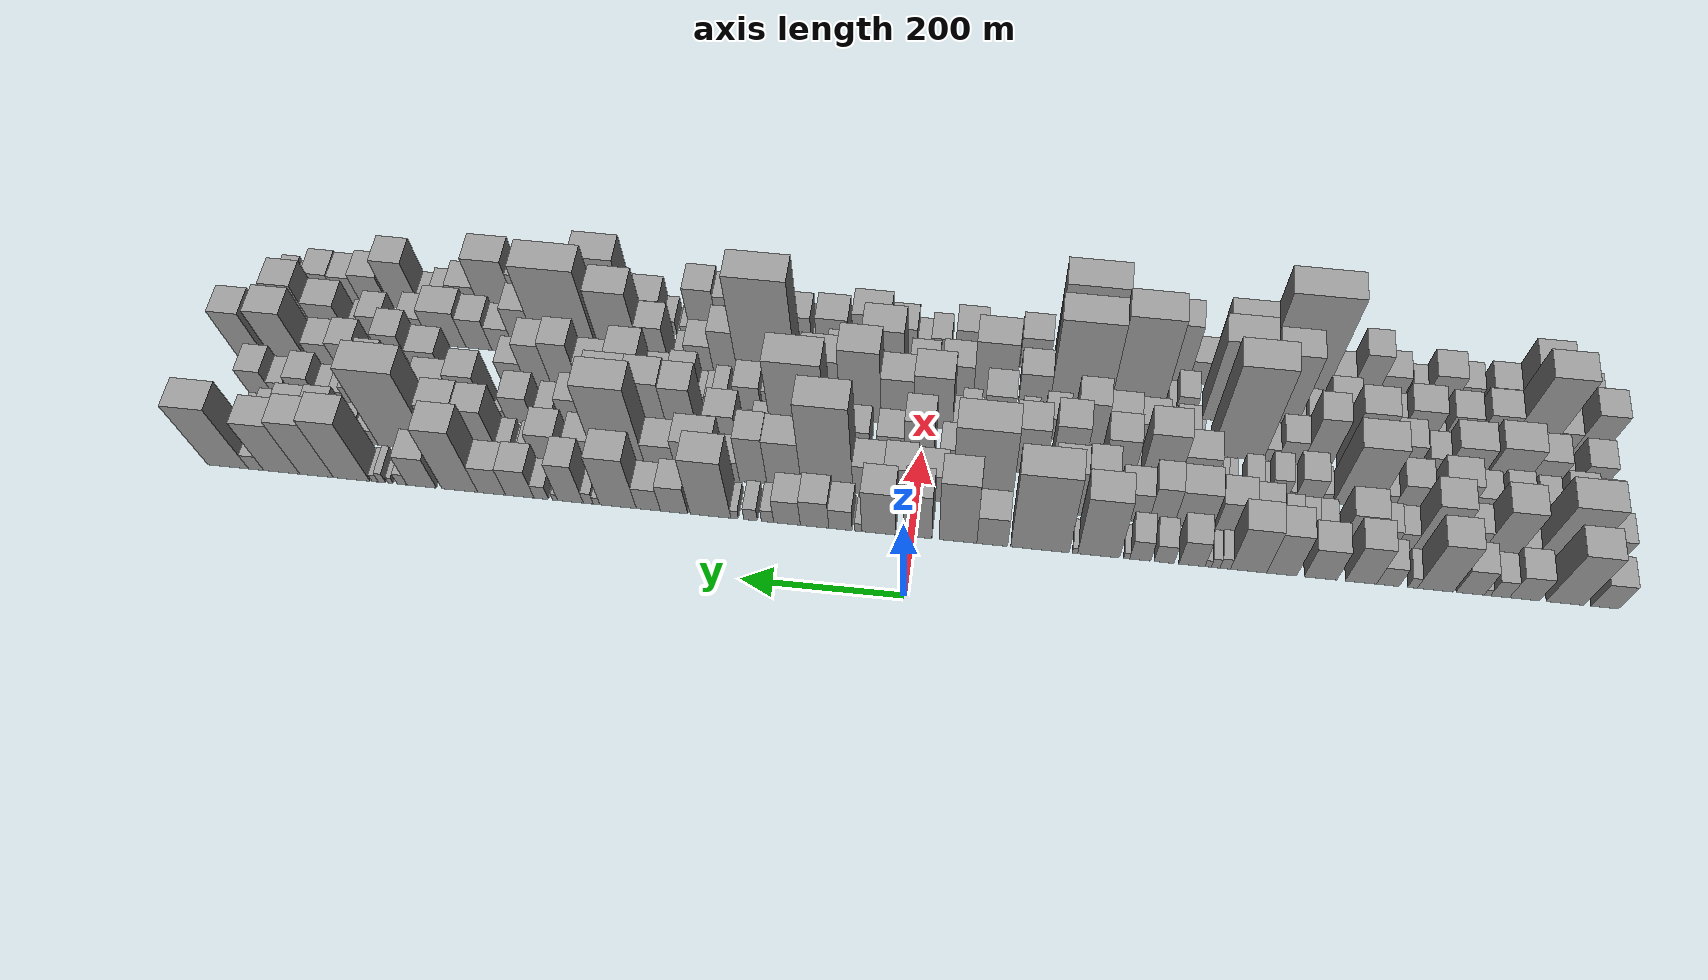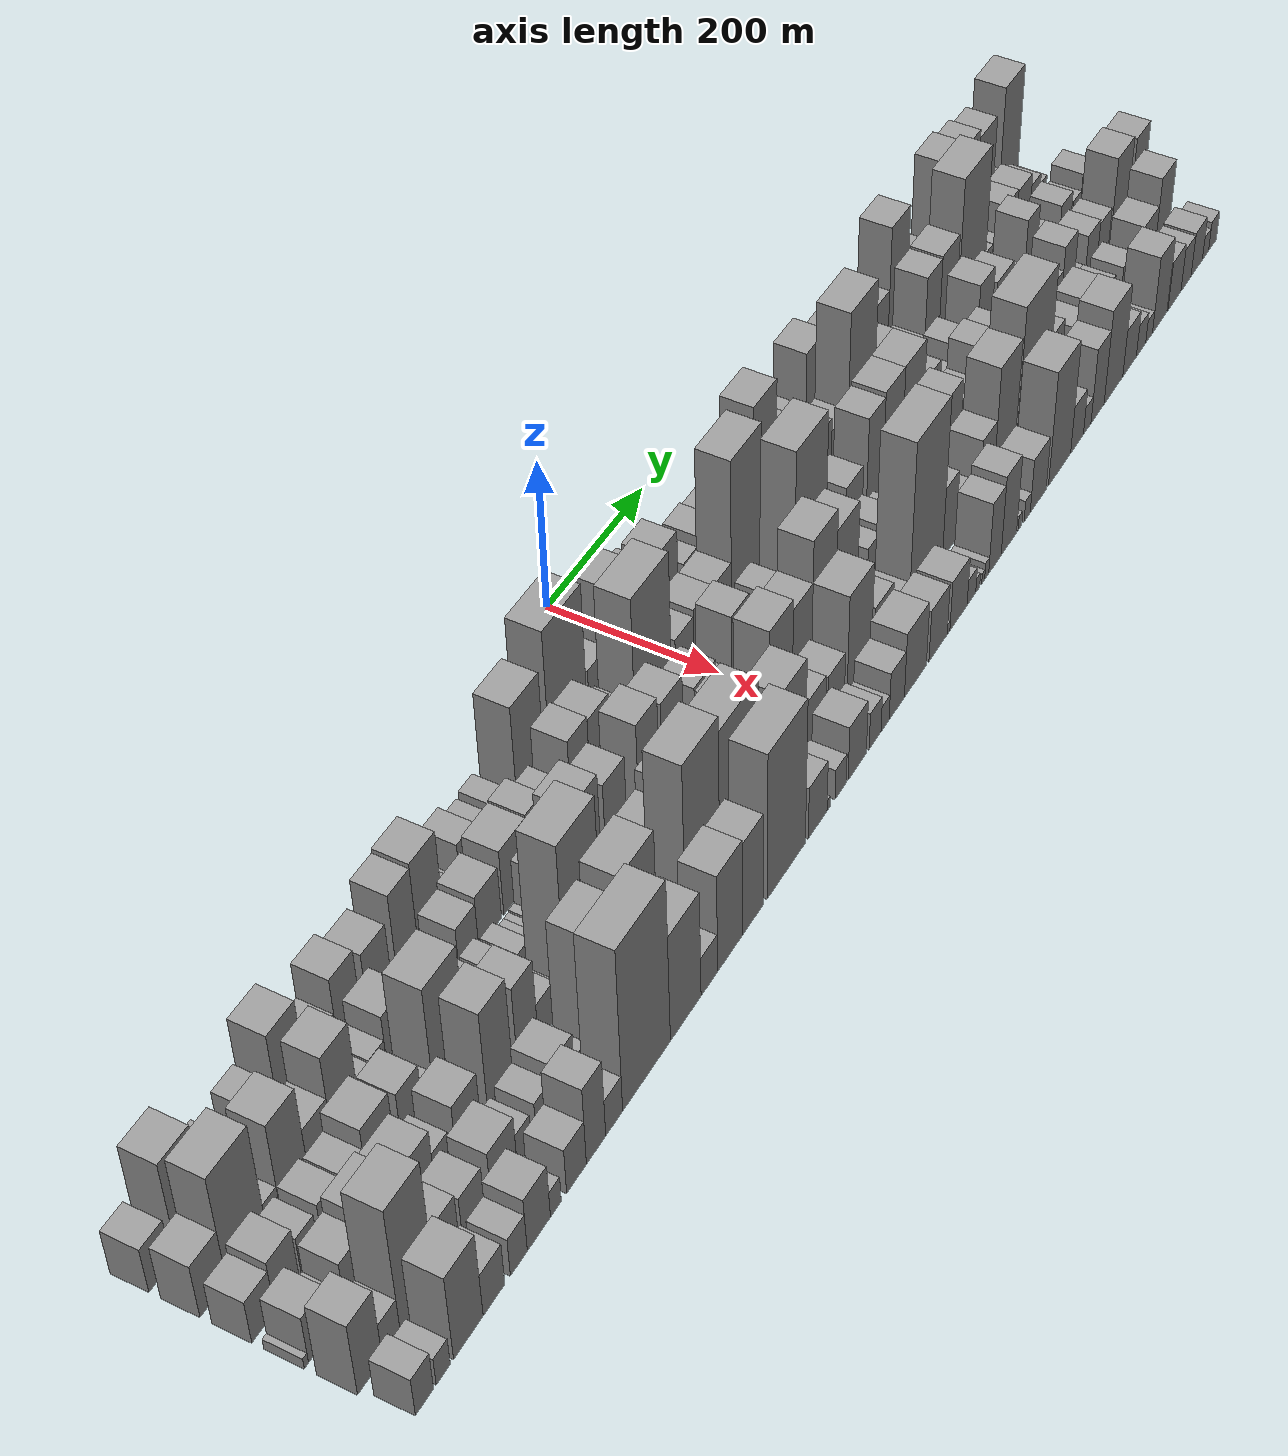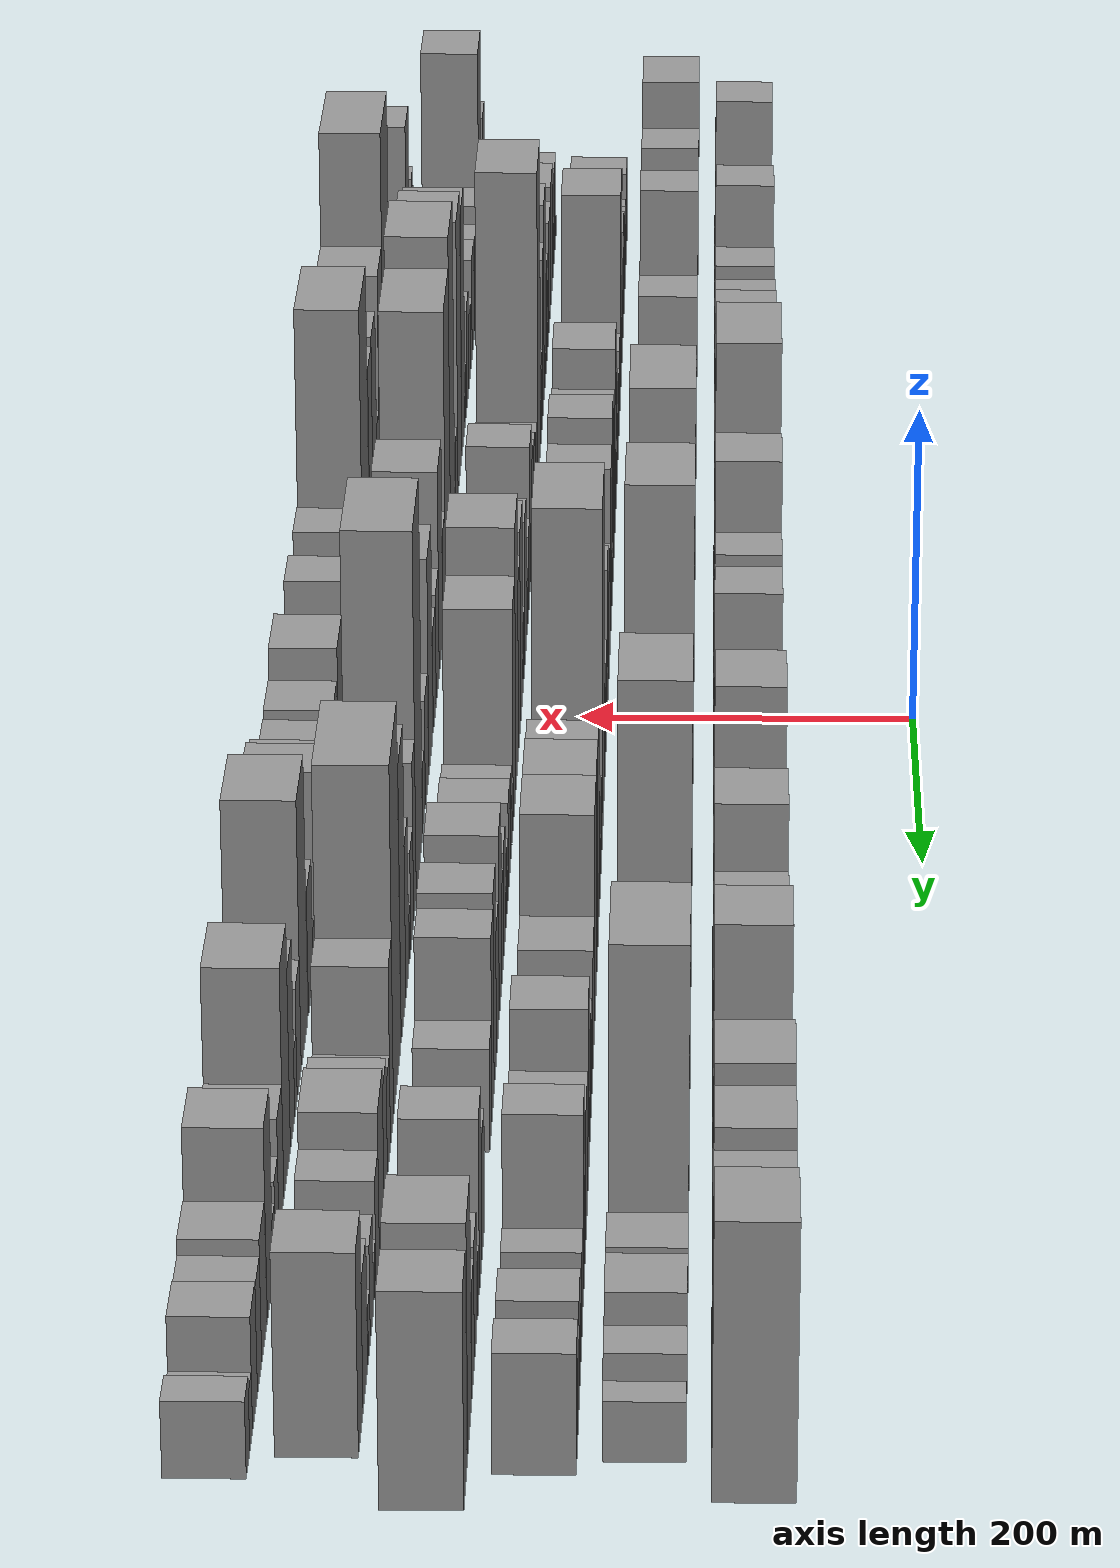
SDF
<sdf version="1.6">
 <world name="default">
  <scene>
   <sky><clouds><speed>12</speed></clouds></sky>
   <ambient>0.4 0.4 0.4 1</ambient>
   <background>0.7 0.7 0.7 1</background>
   <shadows>1</shadows>
  </scene>
  <gravity>0 0 -9.8066</gravity>
  <magnetic_field>6e-06 2.3e-05 -4.2e-05</magnetic_field>
  <physics default="0" name="default_physics" type="ode">
   <ode>
    <solver>
     <type>quick</type>
     <iters>10</iters>
     <sor>1.0</sor>
     <use_dynamic_moi_rescaling>0</use_dynamic_moi_rescaling>
    </solver>
    <constraints>
     <cfm>0</cfm>
     <erp>0.2</erp>
     <contact_max_correcting_vel>100</contact_max_correcting_vel>
     <contact_surface_layer>0.001</contact_surface_layer>
    </constraints>
   </ode>
   <max_step_size>0.004</max_step_size>
   <real_time_factor>1</real_time_factor>
   <real_time_update_rate>250</real_time_update_rate>
  </physics>
  <light name="sun" type="directional">
   <pose>0 0 10 0 0 0</pose>
   <diffuse>0.8 0.8 0.8 1</diffuse>
   <specular>0.2 0.2 0.2 1</specular>
   <attenuation>
    <range>1000</range>
    <constant>0.9</constant>
    <linear>0.01</linear>
    <quadratic>0.001</quadratic>
   </attenuation>
   <direction>-0.5 0.1 -0.9</direction>
  </light>
  <model name="building_1">
   <static>1</static>
   <pose>100.0000 -843.3989 0 0.000000 0.000000 0.000000</pose>
   <link name="link">
    <pose>0 0 31.50 0 0 0</pose>
    <collision name="collision"><geometry><box><size>40.0000 33.2022 63.0000</size></box></geometry></collision>
    <visual name="visual">
     <cast_shadows>0</cast_shadows>
     <geometry><box><size>40.0000 33.2022 63.0000</size></box></geometry>
     <material>
      <script>
       <uri>model://grey_wall/materials/scripts</uri>
       <uri>model://grey_wall/materials/textures</uri>
       <name>vrc/grey_wall</name>
      </script>
     </material>
    </visual>
   </link>
  </model>
  <model name="building_2">
   <static>1</static>
   <pose>100.0000 -796.2391 0 0.000000 0.000000 0.000000</pose>
   <link name="link">
    <pose>0 0 66.00 0 0 0</pose>
    <collision name="collision"><geometry><box><size>40.0000 45.1174 132.0000</size></box></geometry></collision>
    <visual name="visual">
     <cast_shadows>0</cast_shadows>
     <geometry><box><size>40.0000 45.1174 132.0000</size></box></geometry>
     <material>
      <script>
       <uri>model://grey_wall/materials/scripts</uri>
       <uri>model://grey_wall/materials/textures</uri>
       <name>vrc/grey_wall</name>
      </script>
     </material>
    </visual>
   </link>
  </model>
  <model name="building_3">
   <static>1</static>
   <pose>100.0000 -747.7639 0 0.000000 0.000000 0.000000</pose>
   <link name="link">
    <pose>0 0 30.00 0 0 0</pose>
    <collision name="collision"><geometry><box><size>40.0000 35.8329 60.0000</size></box></geometry></collision>
    <visual name="visual">
     <cast_shadows>0</cast_shadows>
     <geometry><box><size>40.0000 35.8329 60.0000</size></box></geometry>
     <material>
      <script>
       <uri>model://grey_wall/materials/scripts</uri>
       <uri>model://grey_wall/materials/textures</uri>
       <name>vrc/grey_wall</name>
      </script>
     </material>
    </visual>
   </link>
  </model>
  <model name="building_4">
   <static>1</static>
   <pose>100.0000 -718.4597 0 0.000000 0.000000 0.000000</pose>
   <link name="link">
    <pose>0 0 21.00 0 0 0</pose>
    <collision name="collision"><geometry><box><size>40.0000 22.7755 42.0000</size></box></geometry></collision>
    <visual name="visual">
     <cast_shadows>0</cast_shadows>
     <geometry><box><size>40.0000 22.7755 42.0000</size></box></geometry>
     <material>
      <script>
       <uri>model://grey_wall/materials/scripts</uri>
       <uri>model://grey_wall/materials/textures</uri>
       <name>vrc/grey_wall</name>
      </script>
     </material>
    </visual>
   </link>
  </model>
  <model name="building_5">
   <static>1</static>
   <pose>100.0000 -703.3240 0 0.000000 0.000000 0.000000</pose>
   <link name="link">
    <pose>0 0 7.50 0 0 0</pose>
    <collision name="collision"><geometry><box><size>40.0000 7.4958 15.0000</size></box></geometry></collision>
    <visual name="visual">
     <cast_shadows>0</cast_shadows>
     <geometry><box><size>40.0000 7.4958 15.0000</size></box></geometry>
     <material>
      <script>
       <uri>model://grey_wall/materials/scripts</uri>
       <uri>model://grey_wall/materials/textures</uri>
       <name>vrc/grey_wall</name>
      </script>
     </material>
    </visual>
   </link>
  </model>
  <model name="building_6">
   <static>1</static>
   <pose>100.0000 -682.7503 0 0.000000 0.000000 0.000000</pose>
   <link name="link">
    <pose>0 0 31.50 0 0 0</pose>
    <collision name="collision"><geometry><box><size>40.0000 33.6517 63.0000</size></box></geometry></collision>
    <visual name="visual">
     <cast_shadows>0</cast_shadows>
     <geometry><box><size>40.0000 33.6517 63.0000</size></box></geometry>
     <material>
      <script>
       <uri>model://grey_wall/materials/scripts</uri>
       <uri>model://grey_wall/materials/textures</uri>
       <name>vrc/grey_wall</name>
      </script>
     </material>
    </visual>
   </link>
  </model>
  <model name="building_7">
   <static>1</static>
   <pose>100.0000 -641.1731 0 0.000000 0.000000 0.000000</pose>
   <link name="link">
    <pose>0 0 61.50 0 0 0</pose>
    <collision name="collision"><geometry><box><size>40.0000 43.5027 123.0000</size></box></geometry></collision>
    <visual name="visual">
     <cast_shadows>0</cast_shadows>
     <geometry><box><size>40.0000 43.5027 123.0000</size></box></geometry>
     <material>
      <script>
       <uri>model://grey_wall/materials/scripts</uri>
       <uri>model://grey_wall/materials/textures</uri>
       <name>vrc/grey_wall</name>
      </script>
     </material>
    </visual>
   </link>
  </model>
  <model name="building_8">
   <static>1</static>
   <pose>100.0000 -613.5712 0 0.000000 0.000000 0.000000</pose>
   <link name="link">
    <pose>0 0 13.50 0 0 0</pose>
    <collision name="collision"><geometry><box><size>40.0000 11.7012 27.0000</size></box></geometry></collision>
    <visual name="visual">
     <cast_shadows>0</cast_shadows>
     <geometry><box><size>40.0000 11.7012 27.0000</size></box></geometry>
     <material>
      <script>
       <uri>model://grey_wall/materials/scripts</uri>
       <uri>model://grey_wall/materials/textures</uri>
       <name>vrc/grey_wall</name>
      </script>
     </material>
    </visual>
   </link>
  </model>
  <model name="building_9">
   <static>1</static>
   <pose>100.0000 -584.1085 0 0.000000 0.000000 0.000000</pose>
   <link name="link">
    <pose>0 0 24.00 0 0 0</pose>
    <collision name="collision"><geometry><box><size>40.0000 27.2240 48.0000</size></box></geometry></collision>
    <visual name="visual">
     <cast_shadows>0</cast_shadows>
     <geometry><box><size>40.0000 27.2240 48.0000</size></box></geometry>
     <material>
      <script>
       <uri>model://grey_wall/materials/scripts</uri>
       <uri>model://grey_wall/materials/textures</uri>
       <name>vrc/grey_wall</name>
      </script>
     </material>
    </visual>
   </link>
  </model>
  <model name="building_10">
   <static>1</static>
   <pose>100.0000 -551.5322 0 0.000000 0.000000 0.000000</pose>
   <link name="link">
    <pose>0 0 48.00 0 0 0</pose>
    <collision name="collision"><geometry><box><size>40.0000 37.9287 96.0000</size></box></geometry></collision>
    <visual name="visual">
     <cast_shadows>0</cast_shadows>
     <geometry><box><size>40.0000 37.9287 96.0000</size></box></geometry>
     <material>
      <script>
       <uri>model://grey_wall/materials/scripts</uri>
       <uri>model://grey_wall/materials/textures</uri>
       <name>vrc/grey_wall</name>
      </script>
     </material>
    </visual>
   </link>
  </model>
  <model name="building_11">
   <static>1</static>
   <pose>100.0000 -502.6477 0 0.000000 0.000000 0.000000</pose>
   <link name="link">
    <pose>0 0 39.00 0 0 0</pose>
    <collision name="collision"><geometry><box><size>40.0000 39.8404 78.0000</size></box></geometry></collision>
    <visual name="visual">
     <cast_shadows>0</cast_shadows>
     <geometry><box><size>40.0000 39.8404 78.0000</size></box></geometry>
     <material>
      <script>
       <uri>model://grey_wall/materials/scripts</uri>
       <uri>model://grey_wall/materials/textures</uri>
       <name>vrc/grey_wall</name>
      </script>
     </material>
    </visual>
   </link>
  </model>
  <model name="building_12">
   <static>1</static>
   <pose>100.0000 -455.4637 0 0.000000 0.000000 0.000000</pose>
   <link name="link">
    <pose>0 0 54.00 0 0 0</pose>
    <collision name="collision"><geometry><box><size>40.0000 36.5275 108.0000</size></box></geometry></collision>
    <visual name="visual">
     <cast_shadows>0</cast_shadows>
     <geometry><box><size>40.0000 36.5275 108.0000</size></box></geometry>
     <material>
      <script>
       <uri>model://grey_wall/materials/scripts</uri>
       <uri>model://grey_wall/materials/textures</uri>
       <name>vrc/grey_wall</name>
      </script>
     </material>
    </visual>
   </link>
  </model>
  <model name="building_13">
   <static>1</static>
   <pose>100.0000 -415.2238 0 0.000000 0.000000 0.000000</pose>
   <link name="link">
    <pose>0 0 57.00 0 0 0</pose>
    <collision name="collision"><geometry><box><size>40.0000 43.9523 114.0000</size></box></geometry></collision>
    <visual name="visual">
     <cast_shadows>0</cast_shadows>
     <geometry><box><size>40.0000 43.9523 114.0000</size></box></geometry>
     <material>
      <script>
       <uri>model://grey_wall/materials/scripts</uri>
       <uri>model://grey_wall/materials/textures</uri>
       <name>vrc/grey_wall</name>
      </script>
     </material>
    </visual>
   </link>
  </model>
  <model name="building_14">
   <static>1</static>
   <pose>100.0000 -386.8586 0 0.000000 0.000000 0.000000</pose>
   <link name="link">
    <pose>0 0 13.50 0 0 0</pose>
    <collision name="collision"><geometry><box><size>40.0000 12.7781 27.0000</size></box></geometry></collision>
    <visual name="visual">
     <cast_shadows>0</cast_shadows>
     <geometry><box><size>40.0000 12.7781 27.0000</size></box></geometry>
     <material>
      <script>
       <uri>model://grey_wall/materials/scripts</uri>
       <uri>model://grey_wall/materials/textures</uri>
       <name>vrc/grey_wall</name>
      </script>
     </material>
    </visual>
   </link>
  </model>
  <model name="building_15">
   <static>1</static>
   <pose>100.0000 -375.0850 0 0.000000 0.000000 0.000000</pose>
   <link name="link">
    <pose>0 0 12.00 0 0 0</pose>
    <collision name="collision"><geometry><box><size>40.0000 10.7691 24.0000</size></box></geometry></collision>
    <visual name="visual">
     <cast_shadows>0</cast_shadows>
     <geometry><box><size>40.0000 10.7691 24.0000</size></box></geometry>
     <material>
      <script>
       <uri>model://grey_wall/materials/scripts</uri>
       <uri>model://grey_wall/materials/textures</uri>
       <name>vrc/grey_wall</name>
      </script>
     </material>
    </visual>
   </link>
  </model>
  <model name="building_16">
   <static>1</static>
   <pose>100.0000 -365.9286 0 0.000000 0.000000 0.000000</pose>
   <link name="link">
    <pose>0 0 9.00 0 0 0</pose>
    <collision name="collision"><geometry><box><size>40.0000 7.5436 18.0000</size></box></geometry></collision>
    <visual name="visual">
     <cast_shadows>0</cast_shadows>
     <geometry><box><size>40.0000 7.5436 18.0000</size></box></geometry>
     <material>
      <script>
       <uri>model://grey_wall/materials/scripts</uri>
       <uri>model://grey_wall/materials/textures</uri>
       <name>vrc/grey_wall</name>
      </script>
     </material>
    </visual>
   </link>
  </model>
  <model name="building_17">
   <static>1</static>
   <pose>100.0000 -346.2201 0 0.000000 0.000000 0.000000</pose>
   <link name="link">
    <pose>0 0 31.50 0 0 0</pose>
    <collision name="collision"><geometry><box><size>40.0000 31.8734 63.0000</size></box></geometry></collision>
    <visual name="visual">
     <cast_shadows>0</cast_shadows>
     <geometry><box><size>40.0000 31.8734 63.0000</size></box></geometry>
     <material>
      <script>
       <uri>model://grey_wall/materials/scripts</uri>
       <uri>model://grey_wall/materials/textures</uri>
       <name>vrc/grey_wall</name>
      </script>
     </material>
    </visual>
   </link>
  </model>
  <model name="building_18">
   <static>1</static>
   <pose>100.0000 -312.0613 0 0.000000 0.000000 0.000000</pose>
   <link name="link">
    <pose>0 0 22.50 0 0 0</pose>
    <collision name="collision"><geometry><box><size>40.0000 24.4442 45.0000</size></box></geometry></collision>
    <visual name="visual">
     <cast_shadows>0</cast_shadows>
     <geometry><box><size>40.0000 24.4442 45.0000</size></box></geometry>
     <material>
      <script>
       <uri>model://grey_wall/materials/scripts</uri>
       <uri>model://grey_wall/materials/textures</uri>
       <name>vrc/grey_wall</name>
      </script>
     </material>
    </visual>
   </link>
  </model>
  <model name="building_19">
   <static>1</static>
   <pose>100.0000 -282.9303 0 0.000000 0.000000 0.000000</pose>
   <link name="link">
    <pose>0 0 25.50 0 0 0</pose>
    <collision name="collision"><geometry><box><size>40.0000 25.8178 51.0000</size></box></geometry></collision>
    <visual name="visual">
     <cast_shadows>0</cast_shadows>
     <geometry><box><size>40.0000 25.8178 51.0000</size></box></geometry>
     <material>
      <script>
       <uri>model://grey_wall/materials/scripts</uri>
       <uri>model://grey_wall/materials/textures</uri>
       <name>vrc/grey_wall</name>
      </script>
     </material>
    </visual>
   </link>
  </model>
  <model name="building_20">
   <static>1</static>
   <pose>100.0000 -266.3486 0 0.000000 0.000000 0.000000</pose>
   <link name="link">
    <pose>0 0 7.50 0 0 0</pose>
    <collision name="collision"><geometry><box><size>40.0000 7.3456 15.0000</size></box></geometry></collision>
    <visual name="visual">
     <cast_shadows>0</cast_shadows>
     <geometry><box><size>40.0000 7.3456 15.0000</size></box></geometry>
     <material>
      <script>
       <uri>model://grey_wall/materials/scripts</uri>
       <uri>model://grey_wall/materials/textures</uri>
       <name>vrc/grey_wall</name>
      </script>
     </material>
    </visual>
   </link>
  </model>
  <model name="building_21">
   <static>1</static>
   <pose>100.0000 -231.8403 0 0.000000 0.000000 0.000000</pose>
   <link name="link">
    <pose>0 0 75.00 0 0 0</pose>
    <collision name="collision"><geometry><box><size>40.0000 51.6710 150.0000</size></box></geometry></collision>
    <visual name="visual">
     <cast_shadows>0</cast_shadows>
     <geometry><box><size>40.0000 51.6710 150.0000</size></box></geometry>
     <material>
      <script>
       <uri>model://grey_wall/materials/scripts</uri>
       <uri>model://grey_wall/materials/textures</uri>
       <name>vrc/grey_wall</name>
      </script>
     </material>
    </visual>
   </link>
  </model>
  <model name="building_22">
   <static>1</static>
   <pose>100.0000 -202.8326 0 0.000000 0.000000 0.000000</pose>
   <link name="link">
    <pose>0 0 7.50 0 0 0</pose>
    <collision name="collision"><geometry><box><size>40.0000 6.3445 15.0000</size></box></geometry></collision>
    <visual name="visual">
     <cast_shadows>0</cast_shadows>
     <geometry><box><size>40.0000 6.3445 15.0000</size></box></geometry>
     <material>
      <script>
       <uri>model://grey_wall/materials/scripts</uri>
       <uri>model://grey_wall/materials/textures</uri>
       <name>vrc/grey_wall</name>
      </script>
     </material>
    </visual>
   </link>
  </model>
  <model name="building_23">
   <static>1</static>
   <pose>100.0000 -159.5477 0 0.000000 0.000000 0.000000</pose>
   <link name="link">
    <pose>0 0 97.50 0 0 0</pose>
    <collision name="collision"><geometry><box><size>40.0000 72.2253 195.0000</size></box></geometry></collision>
    <visual name="visual">
     <cast_shadows>0</cast_shadows>
     <geometry><box><size>40.0000 72.2253 195.0000</size></box></geometry>
     <material>
      <script>
       <uri>model://grey_wall/materials/scripts</uri>
       <uri>model://grey_wall/materials/textures</uri>
       <name>vrc/grey_wall</name>
      </script>
     </material>
    </visual>
   </link>
  </model>
  <model name="building_24">
   <static>1</static>
   <pose>100.0000 -100.4327 0 0.000000 0.000000 0.000000</pose>
   <link name="link">
    <pose>0 0 36.00 0 0 0</pose>
    <collision name="collision"><geometry><box><size>40.0000 38.0046 72.0000</size></box></geometry></collision>
    <visual name="visual">
     <cast_shadows>0</cast_shadows>
     <geometry><box><size>40.0000 38.0046 72.0000</size></box></geometry>
     <material>
      <script>
       <uri>model://grey_wall/materials/scripts</uri>
       <uri>model://grey_wall/materials/textures</uri>
       <name>vrc/grey_wall</name>
      </script>
     </material>
    </visual>
   </link>
  </model>
  <model name="building_25">
   <static>1</static>
   <pose>100.0000 -58.0178 0 0.000000 0.000000 0.000000</pose>
   <link name="link">
    <pose>0 0 76.50 0 0 0</pose>
    <collision name="collision"><geometry><box><size>40.0000 46.8252 153.0000</size></box></geometry></collision>
    <visual name="visual">
     <cast_shadows>0</cast_shadows>
     <geometry><box><size>40.0000 46.8252 153.0000</size></box></geometry>
     <material>
      <script>
       <uri>model://grey_wall/materials/scripts</uri>
       <uri>model://grey_wall/materials/textures</uri>
       <name>vrc/grey_wall</name>
      </script>
     </material>
    </visual>
   </link>
  </model>
  <model name="building_26">
   <static>1</static>
   <pose>100.0000 -7.8596 0 0.000000 0.000000 0.000000</pose>
   <link name="link">
    <pose>0 0 55.50 0 0 0</pose>
    <collision name="collision"><geometry><box><size>40.0000 35.4911 111.0000</size></box></geometry></collision>
    <visual name="visual">
     <cast_shadows>0</cast_shadows>
     <geometry><box><size>40.0000 35.4911 111.0000</size></box></geometry>
     <material>
      <script>
       <uri>model://grey_wall/materials/scripts</uri>
       <uri>model://grey_wall/materials/textures</uri>
       <name>vrc/grey_wall</name>
      </script>
     </material>
    </visual>
   </link>
  </model>
  <model name="building_27">
   <static>1</static>
   <pose>100.0000 40.7392 0 0.000000 0.000000 0.000000</pose>
   <link name="link">
    <pose>0 0 54.00 0 0 0</pose>
    <collision name="collision"><geometry><box><size>40.0000 41.7065 108.0000</size></box></geometry></collision>
    <visual name="visual">
     <cast_shadows>0</cast_shadows>
     <geometry><box><size>40.0000 41.7065 108.0000</size></box></geometry>
     <material>
      <script>
       <uri>model://grey_wall/materials/scripts</uri>
       <uri>model://grey_wall/materials/textures</uri>
       <name>vrc/grey_wall</name>
      </script>
     </material>
    </visual>
   </link>
  </model>
  <model name="building_28">
   <static>1</static>
   <pose>100.0000 66.1730 0 0.000000 0.000000 0.000000</pose>
   <link name="link">
    <pose>0 0 10.50 0 0 0</pose>
    <collision name="collision"><geometry><box><size>40.0000 9.1613 21.0000</size></box></geometry></collision>
    <visual name="visual">
     <cast_shadows>0</cast_shadows>
     <geometry><box><size>40.0000 9.1613 21.0000</size></box></geometry>
     <material>
      <script>
       <uri>model://grey_wall/materials/scripts</uri>
       <uri>model://grey_wall/materials/textures</uri>
       <name>vrc/grey_wall</name>
      </script>
     </material>
    </visual>
   </link>
  </model>
  <model name="building_29">
   <static>1</static>
   <pose>100.0000 88.3548 0 0.000000 0.000000 0.000000</pose>
   <link name="link">
    <pose>0 0 25.50 0 0 0</pose>
    <collision name="collision"><geometry><box><size>40.0000 29.2023 51.0000</size></box></geometry></collision>
    <visual name="visual">
     <cast_shadows>0</cast_shadows>
     <geometry><box><size>40.0000 29.2023 51.0000</size></box></geometry>
     <material>
      <script>
       <uri>model://grey_wall/materials/scripts</uri>
       <uri>model://grey_wall/materials/textures</uri>
       <name>vrc/grey_wall</name>
      </script>
     </material>
    </visual>
   </link>
  </model>
  <model name="building_30">
   <static>1</static>
   <pose>100.0000 120.8287 0 0.000000 0.000000 0.000000</pose>
   <link name="link">
    <pose>0 0 33.00 0 0 0</pose>
    <collision name="collision"><geometry><box><size>40.0000 35.7455 66.0000</size></box></geometry></collision>
    <visual name="visual">
     <cast_shadows>0</cast_shadows>
     <geometry><box><size>40.0000 35.7455 66.0000</size></box></geometry>
     <material>
      <script>
       <uri>model://grey_wall/materials/scripts</uri>
       <uri>model://grey_wall/materials/textures</uri>
       <name>vrc/grey_wall</name>
      </script>
     </material>
    </visual>
   </link>
  </model>
  <model name="building_31">
   <static>1</static>
   <pose>100.0000 155.4661 0 0.000000 0.000000 0.000000</pose>
   <link name="link">
    <pose>0 0 30.00 0 0 0</pose>
    <collision name="collision"><geometry><box><size>40.0000 33.5295 60.0000</size></box></geometry></collision>
    <visual name="visual">
     <cast_shadows>0</cast_shadows>
     <geometry><box><size>40.0000 33.5295 60.0000</size></box></geometry>
     <material>
      <script>
       <uri>model://grey_wall/materials/scripts</uri>
       <uri>model://grey_wall/materials/textures</uri>
       <name>vrc/grey_wall</name>
      </script>
     </material>
    </visual>
   </link>
  </model>
  <model name="building_32">
   <static>1</static>
   <pose>100.0000 179.9575 0 0.000000 0.000000 0.000000</pose>
   <link name="link">
    <pose>0 0 15.00 0 0 0</pose>
    <collision name="collision"><geometry><box><size>40.0000 15.4532 30.0000</size></box></geometry></collision>
    <visual name="visual">
     <cast_shadows>0</cast_shadows>
     <geometry><box><size>40.0000 15.4532 30.0000</size></box></geometry>
     <material>
      <script>
       <uri>model://grey_wall/materials/scripts</uri>
       <uri>model://grey_wall/materials/textures</uri>
       <name>vrc/grey_wall</name>
      </script>
     </material>
    </visual>
   </link>
  </model>
  <model name="building_33">
   <static>1</static>
   <pose>100.0000 201.2121 0 0.000000 0.000000 0.000000</pose>
   <link name="link">
    <pose>0 0 15.00 0 0 0</pose>
    <collision name="collision"><geometry><box><size>40.0000 17.0561 30.0000</size></box></geometry></collision>
    <visual name="visual">
     <cast_shadows>0</cast_shadows>
     <geometry><box><size>40.0000 17.0561 30.0000</size></box></geometry>
     <material>
      <script>
       <uri>model://grey_wall/materials/scripts</uri>
       <uri>model://grey_wall/materials/textures</uri>
       <name>vrc/grey_wall</name>
      </script>
     </material>
    </visual>
   </link>
  </model>
  <model name="building_34">
   <static>1</static>
   <pose>100.0000 221.5178 0 0.000000 0.000000 0.000000</pose>
   <link name="link">
    <pose>0 0 10.50 0 0 0</pose>
    <collision name="collision"><geometry><box><size>40.0000 9.5552 21.0000</size></box></geometry></collision>
    <visual name="visual">
     <cast_shadows>0</cast_shadows>
     <geometry><box><size>40.0000 9.5552 21.0000</size></box></geometry>
     <material>
      <script>
       <uri>model://grey_wall/materials/scripts</uri>
       <uri>model://grey_wall/materials/textures</uri>
       <name>vrc/grey_wall</name>
      </script>
     </material>
    </visual>
   </link>
  </model>
  <model name="building_35">
   <static>1</static>
   <pose>100.0000 251.9744 0 0.000000 0.000000 0.000000</pose>
   <link name="link">
    <pose>0 0 72.00 0 0 0</pose>
    <collision name="collision"><geometry><box><size>40.0000 51.3581 144.0000</size></box></geometry></collision>
    <visual name="visual">
     <cast_shadows>0</cast_shadows>
     <geometry><box><size>40.0000 51.3581 144.0000</size></box></geometry>
     <material>
      <script>
       <uri>model://grey_wall/materials/scripts</uri>
       <uri>model://grey_wall/materials/textures</uri>
       <name>vrc/grey_wall</name>
      </script>
     </material>
    </visual>
   </link>
  </model>
  <model name="building_36">
   <static>1</static>
   <pose>100.0000 297.9914 0 0.000000 0.000000 0.000000</pose>
   <link name="link">
    <pose>0 0 33.00 0 0 0</pose>
    <collision name="collision"><geometry><box><size>40.0000 34.6758 66.0000</size></box></geometry></collision>
    <visual name="visual">
     <cast_shadows>0</cast_shadows>
     <geometry><box><size>40.0000 34.6758 66.0000</size></box></geometry>
     <material>
      <script>
       <uri>model://grey_wall/materials/scripts</uri>
       <uri>model://grey_wall/materials/textures</uri>
       <name>vrc/grey_wall</name>
      </script>
     </material>
    </visual>
   </link>
  </model>
  <model name="building_37">
   <static>1</static>
   <pose>100.0000 330.6113 0 0.000000 0.000000 0.000000</pose>
   <link name="link">
    <pose>0 0 27.00 0 0 0</pose>
    <collision name="collision"><geometry><box><size>40.0000 30.5640 54.0000</size></box></geometry></collision>
    <visual name="visual">
     <cast_shadows>0</cast_shadows>
     <geometry><box><size>40.0000 30.5640 54.0000</size></box></geometry>
     <material>
      <script>
       <uri>model://grey_wall/materials/scripts</uri>
       <uri>model://grey_wall/materials/textures</uri>
       <name>vrc/grey_wall</name>
      </script>
     </material>
    </visual>
   </link>
  </model>
  <model name="building_38">
   <static>1</static>
   <pose>100.0000 369.2119 0 0.000000 0.000000 0.000000</pose>
   <link name="link">
    <pose>0 0 63.00 0 0 0</pose>
    <collision name="collision"><geometry><box><size>40.0000 46.6374 126.0000</size></box></geometry></collision>
    <visual name="visual">
     <cast_shadows>0</cast_shadows>
     <geometry><box><size>40.0000 46.6374 126.0000</size></box></geometry>
     <material>
      <script>
       <uri>model://grey_wall/materials/scripts</uri>
       <uri>model://grey_wall/materials/textures</uri>
       <name>vrc/grey_wall</name>
      </script>
     </material>
    </visual>
   </link>
  </model>
  <model name="building_39">
   <static>1</static>
   <pose>100.0000 396.7341 0 0.000000 0.000000 0.000000</pose>
   <link name="link">
    <pose>0 0 9.00 0 0 0</pose>
    <collision name="collision"><geometry><box><size>40.0000 8.4070 18.0000</size></box></geometry></collision>
    <visual name="visual">
     <cast_shadows>0</cast_shadows>
     <geometry><box><size>40.0000 8.4070 18.0000</size></box></geometry>
     <material>
      <script>
       <uri>model://grey_wall/materials/scripts</uri>
       <uri>model://grey_wall/materials/textures</uri>
       <name>vrc/grey_wall</name>
      </script>
     </material>
    </visual>
   </link>
  </model>
  <model name="building_40">
   <static>1</static>
   <pose>100.0000 407.2230 0 0.000000 0.000000 0.000000</pose>
   <link name="link">
    <pose>0 0 13.50 0 0 0</pose>
    <collision name="collision"><geometry><box><size>40.0000 12.5708 27.0000</size></box></geometry></collision>
    <visual name="visual">
     <cast_shadows>0</cast_shadows>
     <geometry><box><size>40.0000 12.5708 27.0000</size></box></geometry>
     <material>
      <script>
       <uri>model://grey_wall/materials/scripts</uri>
       <uri>model://grey_wall/materials/textures</uri>
       <name>vrc/grey_wall</name>
      </script>
     </material>
    </visual>
   </link>
  </model>
  <model name="building_41">
   <static>1</static>
   <pose>100.0000 430.0035 0 0.000000 0.000000 0.000000</pose>
   <link name="link">
    <pose>0 0 48.00 0 0 0</pose>
    <collision name="collision"><geometry><box><size>40.0000 32.9901 96.0000</size></box></geometry></collision>
    <visual name="visual">
     <cast_shadows>0</cast_shadows>
     <geometry><box><size>40.0000 32.9901 96.0000</size></box></geometry>
     <material>
      <script>
       <uri>model://grey_wall/materials/scripts</uri>
       <uri>model://grey_wall/materials/textures</uri>
       <name>vrc/grey_wall</name>
      </script>
     </material>
    </visual>
   </link>
  </model>
  <model name="building_42">
   <static>1</static>
   <pose>100.0000 449.6973 0 0.000000 0.000000 0.000000</pose>
   <link name="link">
    <pose>0 0 7.50 0 0 0</pose>
    <collision name="collision"><geometry><box><size>40.0000 6.3976 15.0000</size></box></geometry></collision>
    <visual name="visual">
     <cast_shadows>0</cast_shadows>
     <geometry><box><size>40.0000 6.3976 15.0000</size></box></geometry>
     <material>
      <script>
       <uri>model://grey_wall/materials/scripts</uri>
       <uri>model://grey_wall/materials/textures</uri>
       <name>vrc/grey_wall</name>
      </script>
     </material>
    </visual>
   </link>
  </model>
  <model name="building_43">
   <static>1</static>
   <pose>100.0000 467.1115 0 0.000000 0.000000 0.000000</pose>
   <link name="link">
    <pose>0 0 16.50 0 0 0</pose>
    <collision name="collision"><geometry><box><size>40.0000 18.4309 33.0000</size></box></geometry></collision>
    <visual name="visual">
     <cast_shadows>0</cast_shadows>
     <geometry><box><size>40.0000 18.4309 33.0000</size></box></geometry>
     <material>
      <script>
       <uri>model://grey_wall/materials/scripts</uri>
       <uri>model://grey_wall/materials/textures</uri>
       <name>vrc/grey_wall</name>
      </script>
     </material>
    </visual>
   </link>
  </model>
  <model name="building_44">
   <static>1</static>
   <pose>100.0000 494.6663 0 0.000000 0.000000 0.000000</pose>
   <link name="link">
    <pose>0 0 34.50 0 0 0</pose>
    <collision name="collision"><geometry><box><size>40.0000 36.6787 69.0000</size></box></geometry></collision>
    <visual name="visual">
     <cast_shadows>0</cast_shadows>
     <geometry><box><size>40.0000 36.6787 69.0000</size></box></geometry>
     <material>
      <script>
       <uri>model://grey_wall/materials/scripts</uri>
       <uri>model://grey_wall/materials/textures</uri>
       <name>vrc/grey_wall</name>
      </script>
     </material>
    </visual>
   </link>
  </model>
  <model name="building_45">
   <static>1</static>
   <pose>100.0000 530.7949 0 0.000000 0.000000 0.000000</pose>
   <link name="link">
    <pose>0 0 33.00 0 0 0</pose>
    <collision name="collision"><geometry><box><size>40.0000 35.5785 66.0000</size></box></geometry></collision>
    <visual name="visual">
     <cast_shadows>0</cast_shadows>
     <geometry><box><size>40.0000 35.5785 66.0000</size></box></geometry>
     <material>
      <script>
       <uri>model://grey_wall/materials/scripts</uri>
       <uri>model://grey_wall/materials/textures</uri>
       <name>vrc/grey_wall</name>
      </script>
     </material>
    </visual>
   </link>
  </model>
  <model name="building_46">
   <static>1</static>
   <pose>100.0000 571.7592 0 0.000000 0.000000 0.000000</pose>
   <link name="link">
    <pose>0 0 76.50 0 0 0</pose>
    <collision name="collision"><geometry><box><size>40.0000 46.3501 153.0000</size></box></geometry></collision>
    <visual name="visual">
     <cast_shadows>0</cast_shadows>
     <geometry><box><size>40.0000 46.3501 153.0000</size></box></geometry>
     <material>
      <script>
       <uri>model://grey_wall/materials/scripts</uri>
       <uri>model://grey_wall/materials/textures</uri>
       <name>vrc/grey_wall</name>
      </script>
     </material>
    </visual>
   </link>
  </model>
  <model name="building_47">
   <static>1</static>
   <pose>100.0000 620.8621 0 0.000000 0.000000 0.000000</pose>
   <link name="link">
    <pose>0 0 37.50 0 0 0</pose>
    <collision name="collision"><geometry><box><size>40.0000 37.8558 75.0000</size></box></geometry></collision>
    <visual name="visual">
     <cast_shadows>0</cast_shadows>
     <geometry><box><size>40.0000 37.8558 75.0000</size></box></geometry>
     <material>
      <script>
       <uri>model://grey_wall/materials/scripts</uri>
       <uri>model://grey_wall/materials/textures</uri>
       <name>vrc/grey_wall</name>
      </script>
     </material>
    </visual>
   </link>
  </model>
  <model name="building_48">
   <static>1</static>
   <pose>100.0000 646.1864 0 0.000000 0.000000 0.000000</pose>
   <link name="link">
    <pose>0 0 13.50 0 0 0</pose>
    <collision name="collision"><geometry><box><size>40.0000 12.7928 27.0000</size></box></geometry></collision>
    <visual name="visual">
     <cast_shadows>0</cast_shadows>
     <geometry><box><size>40.0000 12.7928 27.0000</size></box></geometry>
     <material>
      <script>
       <uri>model://grey_wall/materials/scripts</uri>
       <uri>model://grey_wall/materials/textures</uri>
       <name>vrc/grey_wall</name>
      </script>
     </material>
    </visual>
   </link>
  </model>
  <model name="building_49">
   <static>1</static>
   <pose>100.0000 660.9601 0 0.000000 0.000000 0.000000</pose>
   <link name="link">
    <pose>0 0 7.50 0 0 0</pose>
    <collision name="collision"><geometry><box><size>40.0000 6.7546 15.0000</size></box></geometry></collision>
    <visual name="visual">
     <cast_shadows>0</cast_shadows>
     <geometry><box><size>40.0000 6.7546 15.0000</size></box></geometry>
     <material>
      <script>
       <uri>model://grey_wall/materials/scripts</uri>
       <uri>model://grey_wall/materials/textures</uri>
       <name>vrc/grey_wall</name>
      </script>
     </material>
    </visual>
   </link>
  </model>
  <model name="building_50">
   <static>1</static>
   <pose>100.0000 672.1434 0 0.000000 0.000000 0.000000</pose>
   <link name="link">
    <pose>0 0 12.00 0 0 0</pose>
    <collision name="collision"><geometry><box><size>40.0000 9.6119 24.0000</size></box></geometry></collision>
    <visual name="visual">
     <cast_shadows>0</cast_shadows>
     <geometry><box><size>40.0000 9.6119 24.0000</size></box></geometry>
     <material>
      <script>
       <uri>model://grey_wall/materials/scripts</uri>
       <uri>model://grey_wall/materials/textures</uri>
       <name>vrc/grey_wall</name>
      </script>
     </material>
    </visual>
   </link>
  </model>
  <model name="building_51">
   <static>1</static>
   <pose>100.0000 681.0545 0 0.000000 0.000000 0.000000</pose>
   <link name="link">
    <pose>0 0 9.00 0 0 0</pose>
    <collision name="collision"><geometry><box><size>40.0000 8.2103 18.0000</size></box></geometry></collision>
    <visual name="visual">
     <cast_shadows>0</cast_shadows>
     <geometry><box><size>40.0000 8.2103 18.0000</size></box></geometry>
     <material>
      <script>
       <uri>model://grey_wall/materials/scripts</uri>
       <uri>model://grey_wall/materials/textures</uri>
       <name>vrc/grey_wall</name>
      </script>
     </material>
    </visual>
   </link>
  </model>
  <model name="building_52">
   <static>1</static>
   <pose>100.0000 711.6002 0 0.000000 0.000000 0.000000</pose>
   <link name="link">
    <pose>0 0 73.50 0 0 0</pose>
    <collision name="collision"><geometry><box><size>40.0000 46.8810 147.0000</size></box></geometry></collision>
    <visual name="visual">
     <cast_shadows>0</cast_shadows>
     <geometry><box><size>40.0000 46.8810 147.0000</size></box></geometry>
     <material>
      <script>
       <uri>model://grey_wall/materials/scripts</uri>
       <uri>model://grey_wall/materials/textures</uri>
       <name>vrc/grey_wall</name>
      </script>
     </material>
    </visual>
   </link>
  </model>
  <model name="building_53">
   <static>1</static>
   <pose>100.0000 757.0463 0 0.000000 0.000000 0.000000</pose>
   <link name="link">
    <pose>0 0 67.50 0 0 0</pose>
    <collision name="collision"><geometry><box><size>40.0000 44.0112 135.0000</size></box></geometry></collision>
    <visual name="visual">
     <cast_shadows>0</cast_shadows>
     <geometry><box><size>40.0000 44.0112 135.0000</size></box></geometry>
     <material>
      <script>
       <uri>model://grey_wall/materials/scripts</uri>
       <uri>model://grey_wall/materials/textures</uri>
       <name>vrc/grey_wall</name>
      </script>
     </material>
    </visual>
   </link>
  </model>
  <model name="building_54">
   <static>1</static>
   <pose>100.0000 802.4805 0 0.000000 0.000000 0.000000</pose>
   <link name="link">
    <pose>0 0 61.50 0 0 0</pose>
    <collision name="collision"><geometry><box><size>40.0000 46.8574 123.0000</size></box></geometry></collision>
    <visual name="visual">
     <cast_shadows>0</cast_shadows>
     <geometry><box><size>40.0000 46.8574 123.0000</size></box></geometry>
     <material>
      <script>
       <uri>model://grey_wall/materials/scripts</uri>
       <uri>model://grey_wall/materials/textures</uri>
       <name>vrc/grey_wall</name>
      </script>
     </material>
    </visual>
   </link>
  </model>
  <model name="building_55">
   <static>1</static>
   <pose>100.0000 835.8559 0 0.000000 0.000000 0.000000</pose>
   <link name="link">
    <pose>0 0 18.00 0 0 0</pose>
    <collision name="collision"><geometry><box><size>40.0000 19.8933 36.0000</size></box></geometry></collision>
    <visual name="visual">
     <cast_shadows>0</cast_shadows>
     <geometry><box><size>40.0000 19.8933 36.0000</size></box></geometry>
     <material>
      <script>
       <uri>model://grey_wall/materials/scripts</uri>
       <uri>model://grey_wall/materials/textures</uri>
       <name>vrc/grey_wall</name>
      </script>
     </material>
    </visual>
   </link>
  </model>
  <model name="building_56">
   <static>1</static>
   <pose>100.0000 872.4796 0 0.000000 0.000000 0.000000</pose>
   <link name="link">
    <pose>0 0 75.00 0 0 0</pose>
    <collision name="collision"><geometry><box><size>40.0000 53.3541 150.0000</size></box></geometry></collision>
    <visual name="visual">
     <cast_shadows>0</cast_shadows>
     <geometry><box><size>40.0000 53.3541 150.0000</size></box></geometry>
     <material>
      <script>
       <uri>model://grey_wall/materials/scripts</uri>
       <uri>model://grey_wall/materials/textures</uri>
       <name>vrc/grey_wall</name>
      </script>
     </material>
    </visual>
   </link>
  </model>
  <model name="building_57">
   <static>1</static>
   <pose>152.0000 -840.4779 0 0.000000 0.000000 0.000000</pose>
   <link name="link">
    <pose>0 0 37.50 0 0 0</pose>
    <collision name="collision"><geometry><box><size>40.0000 39.0442 75.0000</size></box></geometry></collision>
    <visual name="visual">
     <cast_shadows>0</cast_shadows>
     <geometry><box><size>40.0000 39.0442 75.0000</size></box></geometry>
     <material>
      <script>
       <uri>model://grey_wall/materials/scripts</uri>
       <uri>model://grey_wall/materials/textures</uri>
       <name>vrc/grey_wall</name>
      </script>
     </material>
    </visual>
   </link>
  </model>
  <model name="building_58">
   <static>1</static>
   <pose>152.0000 -791.2860 0 0.000000 0.000000 0.000000</pose>
   <link name="link">
    <pose>0 0 75.00 0 0 0</pose>
    <collision name="collision"><geometry><box><size>40.0000 59.3396 150.0000</size></box></geometry></collision>
    <visual name="visual">
     <cast_shadows>0</cast_shadows>
     <geometry><box><size>40.0000 59.3396 150.0000</size></box></geometry>
     <material>
      <script>
       <uri>model://grey_wall/materials/scripts</uri>
       <uri>model://grey_wall/materials/textures</uri>
       <name>vrc/grey_wall</name>
      </script>
     </material>
    </visual>
   </link>
  </model>
  <model name="building_59">
   <static>1</static>
   <pose>152.0000 -751.0752 0 0.000000 0.000000 0.000000</pose>
   <link name="link">
    <pose>0 0 18.00 0 0 0</pose>
    <collision name="collision"><geometry><box><size>40.0000 21.0821 36.0000</size></box></geometry></collision>
    <visual name="visual">
     <cast_shadows>0</cast_shadows>
     <geometry><box><size>40.0000 21.0821 36.0000</size></box></geometry>
     <material>
      <script>
       <uri>model://grey_wall/materials/scripts</uri>
       <uri>model://grey_wall/materials/textures</uri>
       <name>vrc/grey_wall</name>
      </script>
     </material>
    </visual>
   </link>
  </model>
  <model name="building_60">
   <static>1</static>
   <pose>152.0000 -718.7713 0 0.000000 0.000000 0.000000</pose>
   <link name="link">
    <pose>0 0 61.50 0 0 0</pose>
    <collision name="collision"><geometry><box><size>40.0000 43.5258 123.0000</size></box></geometry></collision>
    <visual name="visual">
     <cast_shadows>0</cast_shadows>
     <geometry><box><size>40.0000 43.5258 123.0000</size></box></geometry>
     <material>
      <script>
       <uri>model://grey_wall/materials/scripts</uri>
       <uri>model://grey_wall/materials/textures</uri>
       <name>vrc/grey_wall</name>
      </script>
     </material>
    </visual>
   </link>
  </model>
  <model name="building_61">
   <static>1</static>
   <pose>152.0000 -678.1103 0 0.000000 0.000000 0.000000</pose>
   <link name="link">
    <pose>0 0 31.50 0 0 0</pose>
    <collision name="collision"><geometry><box><size>40.0000 37.7961 63.0000</size></box></geometry></collision>
    <visual name="visual">
     <cast_shadows>0</cast_shadows>
     <geometry><box><size>40.0000 37.7961 63.0000</size></box></geometry>
     <material>
      <script>
       <uri>model://grey_wall/materials/scripts</uri>
       <uri>model://grey_wall/materials/textures</uri>
       <name>vrc/grey_wall</name>
      </script>
     </material>
    </visual>
   </link>
  </model>
  <model name="building_62">
   <static>1</static>
   <pose>152.0000 -637.7423 0 0.000000 0.000000 0.000000</pose>
   <link name="link">
    <pose>0 0 60.00 0 0 0</pose>
    <collision name="collision"><geometry><box><size>40.0000 42.9400 120.0000</size></box></geometry></collision>
    <visual name="visual">
     <cast_shadows>0</cast_shadows>
     <geometry><box><size>40.0000 42.9400 120.0000</size></box></geometry>
     <material>
      <script>
       <uri>model://grey_wall/materials/scripts</uri>
       <uri>model://grey_wall/materials/textures</uri>
       <name>vrc/grey_wall</name>
      </script>
     </material>
    </visual>
   </link>
  </model>
  <model name="building_63">
   <static>1</static>
   <pose>152.0000 -605.9749 0 0.000000 0.000000 0.000000</pose>
   <link name="link">
    <pose>0 0 19.50 0 0 0</pose>
    <collision name="collision"><geometry><box><size>40.0000 20.5949 39.0000</size></box></geometry></collision>
    <visual name="visual">
     <cast_shadows>0</cast_shadows>
     <geometry><box><size>40.0000 20.5949 39.0000</size></box></geometry>
     <material>
      <script>
       <uri>model://grey_wall/materials/scripts</uri>
       <uri>model://grey_wall/materials/textures</uri>
       <name>vrc/grey_wall</name>
      </script>
     </material>
    </visual>
   </link>
  </model>
  <model name="building_64">
   <static>1</static>
   <pose>152.0000 -583.1113 0 0.000000 0.000000 0.000000</pose>
   <link name="link">
    <pose>0 0 21.00 0 0 0</pose>
    <collision name="collision"><geometry><box><size>40.0000 25.1323 42.0000</size></box></geometry></collision>
    <visual name="visual">
     <cast_shadows>0</cast_shadows>
     <geometry><box><size>40.0000 25.1323 42.0000</size></box></geometry>
     <material>
      <script>
       <uri>model://grey_wall/materials/scripts</uri>
       <uri>model://grey_wall/materials/textures</uri>
       <name>vrc/grey_wall</name>
      </script>
     </material>
    </visual>
   </link>
  </model>
  <model name="building_65">
   <static>1</static>
   <pose>152.0000 -549.5012 0 0.000000 0.000000 0.000000</pose>
   <link name="link">
    <pose>0 0 37.50 0 0 0</pose>
    <collision name="collision"><geometry><box><size>40.0000 42.0879 75.0000</size></box></geometry></collision>
    <visual name="visual">
     <cast_shadows>0</cast_shadows>
     <geometry><box><size>40.0000 42.0879 75.0000</size></box></geometry>
     <material>
      <script>
       <uri>model://grey_wall/materials/scripts</uri>
       <uri>model://grey_wall/materials/textures</uri>
       <name>vrc/grey_wall</name>
      </script>
     </material>
    </visual>
   </link>
  </model>
  <model name="building_66">
   <static>1</static>
   <pose>152.0000 -507.6763 0 0.000000 0.000000 0.000000</pose>
   <link name="link">
    <pose>0 0 18.00 0 0 0</pose>
    <collision name="collision"><geometry><box><size>40.0000 21.5619 36.0000</size></box></geometry></collision>
    <visual name="visual">
     <cast_shadows>0</cast_shadows>
     <geometry><box><size>40.0000 21.5619 36.0000</size></box></geometry>
     <material>
      <script>
       <uri>model://grey_wall/materials/scripts</uri>
       <uri>model://grey_wall/materials/textures</uri>
       <name>vrc/grey_wall</name>
      </script>
     </material>
    </visual>
   </link>
  </model>
  <model name="building_67">
   <static>1</static>
   <pose>152.0000 -486.7361 0 0.000000 0.000000 0.000000</pose>
   <link name="link">
    <pose>0 0 18.00 0 0 0</pose>
    <collision name="collision"><geometry><box><size>40.0000 20.3186 36.0000</size></box></geometry></collision>
    <visual name="visual">
     <cast_shadows>0</cast_shadows>
     <geometry><box><size>40.0000 20.3186 36.0000</size></box></geometry>
     <material>
      <script>
       <uri>model://grey_wall/materials/scripts</uri>
       <uri>model://grey_wall/materials/textures</uri>
       <name>vrc/grey_wall</name>
      </script>
     </material>
    </visual>
   </link>
  </model>
  <model name="building_68">
   <static>1</static>
   <pose>152.0000 -465.6674 0 0.000000 0.000000 0.000000</pose>
   <link name="link">
    <pose>0 0 19.50 0 0 0</pose>
    <collision name="collision"><geometry><box><size>40.0000 21.8188 39.0000</size></box></geometry></collision>
    <visual name="visual">
     <cast_shadows>0</cast_shadows>
     <geometry><box><size>40.0000 21.8188 39.0000</size></box></geometry>
     <material>
      <script>
       <uri>model://grey_wall/materials/scripts</uri>
       <uri>model://grey_wall/materials/textures</uri>
       <name>vrc/grey_wall</name>
      </script>
     </material>
    </visual>
   </link>
  </model>
  <model name="building_69">
   <static>1</static>
   <pose>152.0000 -451.7228 0 0.000000 0.000000 0.000000</pose>
   <link name="link">
    <pose>0 0 7.50 0 0 0</pose>
    <collision name="collision"><geometry><box><size>40.0000 6.0704 15.0000</size></box></geometry></collision>
    <visual name="visual">
     <cast_shadows>0</cast_shadows>
     <geometry><box><size>40.0000 6.0704 15.0000</size></box></geometry>
     <material>
      <script>
       <uri>model://grey_wall/materials/scripts</uri>
       <uri>model://grey_wall/materials/textures</uri>
       <name>vrc/grey_wall</name>
      </script>
     </material>
    </visual>
   </link>
  </model>
  <model name="building_70">
   <static>1</static>
   <pose>152.0000 -431.6884 0 0.000000 0.000000 0.000000</pose>
   <link name="link">
    <pose>0 0 31.50 0 0 0</pose>
    <collision name="collision"><geometry><box><size>40.0000 33.9985 63.0000</size></box></geometry></collision>
    <visual name="visual">
     <cast_shadows>0</cast_shadows>
     <geometry><box><size>40.0000 33.9985 63.0000</size></box></geometry>
     <material>
      <script>
       <uri>model://grey_wall/materials/scripts</uri>
       <uri>model://grey_wall/materials/textures</uri>
       <name>vrc/grey_wall</name>
      </script>
     </material>
    </visual>
   </link>
  </model>
  <model name="building_71">
   <static>1</static>
   <pose>152.0000 -394.3944 0 0.000000 0.000000 0.000000</pose>
   <link name="link">
    <pose>0 0 36.00 0 0 0</pose>
    <collision name="collision"><geometry><box><size>40.0000 40.5895 72.0000</size></box></geometry></collision>
    <visual name="visual">
     <cast_shadows>0</cast_shadows>
     <geometry><box><size>40.0000 40.5895 72.0000</size></box></geometry>
     <material>
      <script>
       <uri>model://grey_wall/materials/scripts</uri>
       <uri>model://grey_wall/materials/textures</uri>
       <name>vrc/grey_wall</name>
      </script>
     </material>
    </visual>
   </link>
  </model>
  <model name="building_72">
   <static>1</static>
   <pose>152.0000 -346.4640 0 0.000000 0.000000 0.000000</pose>
   <link name="link">
    <pose>0 0 45.00 0 0 0</pose>
    <collision name="collision"><geometry><box><size>40.0000 47.2713 90.0000</size></box></geometry></collision>
    <visual name="visual">
     <cast_shadows>0</cast_shadows>
     <geometry><box><size>40.0000 47.2713 90.0000</size></box></geometry>
     <material>
      <script>
       <uri>model://grey_wall/materials/scripts</uri>
       <uri>model://grey_wall/materials/textures</uri>
       <name>vrc/grey_wall</name>
      </script>
     </material>
    </visual>
   </link>
  </model>
  <model name="building_73">
   <static>1</static>
   <pose>152.0000 -306.9529 0 0.000000 0.000000 0.000000</pose>
   <link name="link">
    <pose>0 0 46.50 0 0 0</pose>
    <collision name="collision"><geometry><box><size>40.0000 31.7508 93.0000</size></box></geometry></collision>
    <visual name="visual">
     <cast_shadows>0</cast_shadows>
     <geometry><box><size>40.0000 31.7508 93.0000</size></box></geometry>
     <material>
      <script>
       <uri>model://grey_wall/materials/scripts</uri>
       <uri>model://grey_wall/materials/textures</uri>
       <name>vrc/grey_wall</name>
      </script>
     </material>
    </visual>
   </link>
  </model>
  <model name="building_74">
   <static>1</static>
   <pose>152.0000 -271.5921 0 0.000000 0.000000 0.000000</pose>
   <link name="link">
    <pose>0 0 36.00 0 0 0</pose>
    <collision name="collision"><geometry><box><size>40.0000 38.9710 72.0000</size></box></geometry></collision>
    <visual name="visual">
     <cast_shadows>0</cast_shadows>
     <geometry><box><size>40.0000 38.9710 72.0000</size></box></geometry>
     <material>
      <script>
       <uri>model://grey_wall/materials/scripts</uri>
       <uri>model://grey_wall/materials/textures</uri>
       <name>vrc/grey_wall</name>
      </script>
     </material>
    </visual>
   </link>
  </model>
  <model name="building_75">
   <static>1</static>
   <pose>152.0000 -248.0047 0 0.000000 0.000000 0.000000</pose>
   <link name="link">
    <pose>0 0 9.00 0 0 0</pose>
    <collision name="collision"><geometry><box><size>40.0000 8.2037 18.0000</size></box></geometry></collision>
    <visual name="visual">
     <cast_shadows>0</cast_shadows>
     <geometry><box><size>40.0000 8.2037 18.0000</size></box></geometry>
     <material>
      <script>
       <uri>model://grey_wall/materials/scripts</uri>
       <uri>model://grey_wall/materials/textures</uri>
       <name>vrc/grey_wall</name>
      </script>
     </material>
    </visual>
   </link>
  </model>
  <model name="building_76">
   <static>1</static>
   <pose>152.0000 -225.6303 0 0.000000 0.000000 0.000000</pose>
   <link name="link">
    <pose>0 0 58.50 0 0 0</pose>
    <collision name="collision"><geometry><box><size>40.0000 36.5451 117.0000</size></box></geometry></collision>
    <visual name="visual">
     <cast_shadows>0</cast_shadows>
     <geometry><box><size>40.0000 36.5451 117.0000</size></box></geometry>
     <material>
      <script>
       <uri>model://grey_wall/materials/scripts</uri>
       <uri>model://grey_wall/materials/textures</uri>
       <name>vrc/grey_wall</name>
      </script>
     </material>
    </visual>
   </link>
  </model>
  <model name="building_77">
   <static>1</static>
   <pose>152.0000 -187.3278 0 0.000000 0.000000 0.000000</pose>
   <link name="link">
    <pose>0 0 55.50 0 0 0</pose>
    <collision name="collision"><geometry><box><size>40.0000 40.0598 111.0000</size></box></geometry></collision>
    <visual name="visual">
     <cast_shadows>0</cast_shadows>
     <geometry><box><size>40.0000 40.0598 111.0000</size></box></geometry>
     <material>
      <script>
       <uri>model://grey_wall/materials/scripts</uri>
       <uri>model://grey_wall/materials/textures</uri>
       <name>vrc/grey_wall</name>
      </script>
     </material>
    </visual>
   </link>
  </model>
  <model name="building_78">
   <static>1</static>
   <pose>152.0000 -147.6420 0 0.000000 0.000000 0.000000</pose>
   <link name="link">
    <pose>0 0 33.00 0 0 0</pose>
    <collision name="collision"><geometry><box><size>40.0000 39.3119 66.0000</size></box></geometry></collision>
    <visual name="visual">
     <cast_shadows>0</cast_shadows>
     <geometry><box><size>40.0000 39.3119 66.0000</size></box></geometry>
     <material>
      <script>
       <uri>model://grey_wall/materials/scripts</uri>
       <uri>model://grey_wall/materials/textures</uri>
       <name>vrc/grey_wall</name>
      </script>
     </material>
    </visual>
   </link>
  </model>
  <model name="building_79">
   <static>1</static>
   <pose>152.0000 -83.1456 0 0.000000 0.000000 0.000000</pose>
   <link name="link">
    <pose>0 0 97.50 0 0 0</pose>
    <collision name="collision"><geometry><box><size>40.0000 73.6807 195.0000</size></box></geometry></collision>
    <visual name="visual">
     <cast_shadows>0</cast_shadows>
     <geometry><box><size>40.0000 73.6807 195.0000</size></box></geometry>
     <material>
      <script>
       <uri>model://grey_wall/materials/scripts</uri>
       <uri>model://grey_wall/materials/textures</uri>
       <name>vrc/grey_wall</name>
      </script>
     </material>
    </visual>
   </link>
  </model>
  <model name="building_80">
   <static>1</static>
   <pose>152.0000 -42.1324 0 0.000000 0.000000 0.000000</pose>
   <link name="link">
    <pose>0 0 9.00 0 0 0</pose>
    <collision name="collision"><geometry><box><size>40.0000 8.3459 18.0000</size></box></geometry></collision>
    <visual name="visual">
     <cast_shadows>0</cast_shadows>
     <geometry><box><size>40.0000 8.3459 18.0000</size></box></geometry>
     <material>
      <script>
       <uri>model://grey_wall/materials/scripts</uri>
       <uri>model://grey_wall/materials/textures</uri>
       <name>vrc/grey_wall</name>
      </script>
     </material>
    </visual>
   </link>
  </model>
  <model name="building_81">
   <static>1</static>
   <pose>152.0000 -19.0368 0 0.000000 0.000000 0.000000</pose>
   <link name="link">
    <pose>0 0 33.00 0 0 0</pose>
    <collision name="collision"><geometry><box><size>40.0000 37.8453 66.0000</size></box></geometry></collision>
    <visual name="visual">
     <cast_shadows>0</cast_shadows>
     <geometry><box><size>40.0000 37.8453 66.0000</size></box></geometry>
     <material>
      <script>
       <uri>model://grey_wall/materials/scripts</uri>
       <uri>model://grey_wall/materials/textures</uri>
       <name>vrc/grey_wall</name>
      </script>
     </material>
    </visual>
   </link>
  </model>
  <model name="building_82">
   <static>1</static>
   <pose>152.0000 20.0602 0 0.000000 0.000000 0.000000</pose>
   <link name="link">
    <pose>0 0 37.50 0 0 0</pose>
    <collision name="collision"><geometry><box><size>40.0000 40.3486 75.0000</size></box></geometry></collision>
    <visual name="visual">
     <cast_shadows>0</cast_shadows>
     <geometry><box><size>40.0000 40.3486 75.0000</size></box></geometry>
     <material>
      <script>
       <uri>model://grey_wall/materials/scripts</uri>
       <uri>model://grey_wall/materials/textures</uri>
       <name>vrc/grey_wall</name>
      </script>
     </material>
    </visual>
   </link>
  </model>
  <model name="building_83">
   <static>1</static>
   <pose>152.0000 59.7744 0 0.000000 0.000000 0.000000</pose>
   <link name="link">
    <pose>0 0 36.00 0 0 0</pose>
    <collision name="collision"><geometry><box><size>40.0000 39.0799 72.0000</size></box></geometry></collision>
    <visual name="visual">
     <cast_shadows>0</cast_shadows>
     <geometry><box><size>40.0000 39.0799 72.0000</size></box></geometry>
     <material>
      <script>
       <uri>model://grey_wall/materials/scripts</uri>
       <uri>model://grey_wall/materials/textures</uri>
       <name>vrc/grey_wall</name>
      </script>
     </material>
    </visual>
   </link>
  </model>
  <model name="building_84">
   <static>1</static>
   <pose>152.0000 112.0152 0 0.000000 0.000000 0.000000</pose>
   <link name="link">
    <pose>0 0 105.00 0 0 0</pose>
    <collision name="collision"><geometry><box><size>40.0000 65.4018 210.0000</size></box></geometry></collision>
    <visual name="visual">
     <cast_shadows>0</cast_shadows>
     <geometry><box><size>40.0000 65.4018 210.0000</size></box></geometry>
     <material>
      <script>
       <uri>model://grey_wall/materials/scripts</uri>
       <uri>model://grey_wall/materials/textures</uri>
       <name>vrc/grey_wall</name>
      </script>
     </material>
    </visual>
   </link>
  </model>
  <model name="building_85">
   <static>1</static>
   <pose>152.0000 166.7514 0 0.000000 0.000000 0.000000</pose>
   <link name="link">
    <pose>0 0 55.50 0 0 0</pose>
    <collision name="collision"><geometry><box><size>40.0000 44.0705 111.0000</size></box></geometry></collision>
    <visual name="visual">
     <cast_shadows>0</cast_shadows>
     <geometry><box><size>40.0000 44.0705 111.0000</size></box></geometry>
     <material>
      <script>
       <uri>model://grey_wall/materials/scripts</uri>
       <uri>model://grey_wall/materials/textures</uri>
       <name>vrc/grey_wall</name>
      </script>
     </material>
    </visual>
   </link>
  </model>
  <model name="building_86">
   <static>1</static>
   <pose>152.0000 206.3000 0 0.000000 0.000000 0.000000</pose>
   <link name="link">
    <pose>0 0 57.00 0 0 0</pose>
    <collision name="collision"><geometry><box><size>40.0000 35.0266 114.0000</size></box></geometry></collision>
    <visual name="visual">
     <cast_shadows>0</cast_shadows>
     <geometry><box><size>40.0000 35.0266 114.0000</size></box></geometry>
     <material>
      <script>
       <uri>model://grey_wall/materials/scripts</uri>
       <uri>model://grey_wall/materials/textures</uri>
       <name>vrc/grey_wall</name>
      </script>
     </material>
    </visual>
   </link>
  </model>
  <model name="building_87">
   <static>1</static>
   <pose>152.0000 237.8095 0 0.000000 0.000000 0.000000</pose>
   <link name="link">
    <pose>0 0 24.00 0 0 0</pose>
    <collision name="collision"><geometry><box><size>40.0000 27.9924 48.0000</size></box></geometry></collision>
    <visual name="visual">
     <cast_shadows>0</cast_shadows>
     <geometry><box><size>40.0000 27.9924 48.0000</size></box></geometry>
     <material>
      <script>
       <uri>model://grey_wall/materials/scripts</uri>
       <uri>model://grey_wall/materials/textures</uri>
       <name>vrc/grey_wall</name>
      </script>
     </material>
    </visual>
   </link>
  </model>
  <model name="building_88">
   <static>1</static>
   <pose>152.0000 277.7414 0 0.000000 0.000000 0.000000</pose>
   <link name="link">
    <pose>0 0 45.00 0 0 0</pose>
    <collision name="collision"><geometry><box><size>40.0000 51.8714 90.0000</size></box></geometry></collision>
    <visual name="visual">
     <cast_shadows>0</cast_shadows>
     <geometry><box><size>40.0000 51.8714 90.0000</size></box></geometry>
     <material>
      <script>
       <uri>model://grey_wall/materials/scripts</uri>
       <uri>model://grey_wall/materials/textures</uri>
       <name>vrc/grey_wall</name>
      </script>
     </material>
    </visual>
   </link>
  </model>
  <model name="building_89">
   <static>1</static>
   <pose>152.0000 323.1185 0 0.000000 0.000000 0.000000</pose>
   <link name="link">
    <pose>0 0 36.00 0 0 0</pose>
    <collision name="collision"><geometry><box><size>40.0000 38.8828 72.0000</size></box></geometry></collision>
    <visual name="visual">
     <cast_shadows>0</cast_shadows>
     <geometry><box><size>40.0000 38.8828 72.0000</size></box></geometry>
     <material>
      <script>
       <uri>model://grey_wall/materials/scripts</uri>
       <uri>model://grey_wall/materials/textures</uri>
       <name>vrc/grey_wall</name>
      </script>
     </material>
    </visual>
   </link>
  </model>
  <model name="building_90">
   <static>1</static>
   <pose>152.0000 374.3537 0 0.000000 0.000000 0.000000</pose>
   <link name="link">
    <pose>0 0 102.00 0 0 0</pose>
    <collision name="collision"><geometry><box><size>40.0000 63.5877 204.0000</size></box></geometry></collision>
    <visual name="visual">
     <cast_shadows>0</cast_shadows>
     <geometry><box><size>40.0000 63.5877 204.0000</size></box></geometry>
     <material>
      <script>
       <uri>model://grey_wall/materials/scripts</uri>
       <uri>model://grey_wall/materials/textures</uri>
       <name>vrc/grey_wall</name>
      </script>
     </material>
    </visual>
   </link>
  </model>
  <model name="building_91">
   <static>1</static>
   <pose>152.0000 423.8537 0 0.000000 0.000000 0.000000</pose>
   <link name="link">
    <pose>0 0 33.00 0 0 0</pose>
    <collision name="collision"><geometry><box><size>40.0000 35.4122 66.0000</size></box></geometry></collision>
    <visual name="visual">
     <cast_shadows>0</cast_shadows>
     <geometry><box><size>40.0000 35.4122 66.0000</size></box></geometry>
     <material>
      <script>
       <uri>model://grey_wall/materials/scripts</uri>
       <uri>model://grey_wall/materials/textures</uri>
       <name>vrc/grey_wall</name>
      </script>
     </material>
    </visual>
   </link>
  </model>
  <model name="building_92">
   <static>1</static>
   <pose>152.0000 446.6012 0 0.000000 0.000000 0.000000</pose>
   <link name="link">
    <pose>0 0 10.50 0 0 0</pose>
    <collision name="collision"><geometry><box><size>40.0000 10.0827 21.0000</size></box></geometry></collision>
    <visual name="visual">
     <cast_shadows>0</cast_shadows>
     <geometry><box><size>40.0000 10.0827 21.0000</size></box></geometry>
     <material>
      <script>
       <uri>model://grey_wall/materials/scripts</uri>
       <uri>model://grey_wall/materials/textures</uri>
       <name>vrc/grey_wall</name>
      </script>
     </material>
    </visual>
   </link>
  </model>
  <model name="building_93">
   <static>1</static>
   <pose>152.0000 470.5676 0 0.000000 0.000000 0.000000</pose>
   <link name="link">
    <pose>0 0 34.50 0 0 0</pose>
    <collision name="collision"><geometry><box><size>40.0000 37.8502 69.0000</size></box></geometry></collision>
    <visual name="visual">
     <cast_shadows>0</cast_shadows>
     <geometry><box><size>40.0000 37.8502 69.0000</size></box></geometry>
     <material>
      <script>
       <uri>model://grey_wall/materials/scripts</uri>
       <uri>model://grey_wall/materials/textures</uri>
       <name>vrc/grey_wall</name>
      </script>
     </material>
    </visual>
   </link>
  </model>
  <model name="building_94">
   <static>1</static>
   <pose>152.0000 498.0877 0 0.000000 0.000000 0.000000</pose>
   <link name="link">
    <pose>0 0 15.00 0 0 0</pose>
    <collision name="collision"><geometry><box><size>40.0000 17.1900 30.0000</size></box></geometry></collision>
    <visual name="visual">
     <cast_shadows>0</cast_shadows>
     <geometry><box><size>40.0000 17.1900 30.0000</size></box></geometry>
     <material>
      <script>
       <uri>model://grey_wall/materials/scripts</uri>
       <uri>model://grey_wall/materials/textures</uri>
       <name>vrc/grey_wall</name>
      </script>
     </material>
    </visual>
   </link>
  </model>
  <model name="building_95">
   <static>1</static>
   <pose>152.0000 510.2926 0 0.000000 0.000000 0.000000</pose>
   <link name="link">
    <pose>0 0 7.50 0 0 0</pose>
    <collision name="collision"><geometry><box><size>40.0000 7.2199 15.0000</size></box></geometry></collision>
    <visual name="visual">
     <cast_shadows>0</cast_shadows>
     <geometry><box><size>40.0000 7.2199 15.0000</size></box></geometry>
     <material>
      <script>
       <uri>model://grey_wall/materials/scripts</uri>
       <uri>model://grey_wall/materials/textures</uri>
       <name>vrc/grey_wall</name>
      </script>
     </material>
    </visual>
   </link>
  </model>
  <model name="building_96">
   <static>1</static>
   <pose>152.0000 523.5009 0 0.000000 0.000000 0.000000</pose>
   <link name="link">
    <pose>0 0 16.50 0 0 0</pose>
    <collision name="collision"><geometry><box><size>40.0000 19.1967 33.0000</size></box></geometry></collision>
    <visual name="visual">
     <cast_shadows>0</cast_shadows>
     <geometry><box><size>40.0000 19.1967 33.0000</size></box></geometry>
     <material>
      <script>
       <uri>model://grey_wall/materials/scripts</uri>
       <uri>model://grey_wall/materials/textures</uri>
       <name>vrc/grey_wall</name>
      </script>
     </material>
    </visual>
   </link>
  </model>
  <model name="building_97">
   <static>1</static>
   <pose>152.0000 552.0997 0 0.000000 0.000000 0.000000</pose>
   <link name="link">
    <pose>0 0 57.00 0 0 0</pose>
    <collision name="collision"><geometry><box><size>40.0000 38.0009 114.0000</size></box></geometry></collision>
    <visual name="visual">
     <cast_shadows>0</cast_shadows>
     <geometry><box><size>40.0000 38.0009 114.0000</size></box></geometry>
     <material>
      <script>
       <uri>model://grey_wall/materials/scripts</uri>
       <uri>model://grey_wall/materials/textures</uri>
       <name>vrc/grey_wall</name>
      </script>
     </material>
    </visual>
   </link>
  </model>
  <model name="building_98">
   <static>1</static>
   <pose>152.0000 593.2633 0 0.000000 0.000000 0.000000</pose>
   <link name="link">
    <pose>0 0 58.50 0 0 0</pose>
    <collision name="collision"><geometry><box><size>40.0000 44.3261 117.0000</size></box></geometry></collision>
    <visual name="visual">
     <cast_shadows>0</cast_shadows>
     <geometry><box><size>40.0000 44.3261 117.0000</size></box></geometry>
     <material>
      <script>
       <uri>model://grey_wall/materials/scripts</uri>
       <uri>model://grey_wall/materials/textures</uri>
       <name>vrc/grey_wall</name>
      </script>
     </material>
    </visual>
   </link>
  </model>
  <model name="building_99">
   <static>1</static>
   <pose>152.0000 656.1138 0 0.000000 0.000000 0.000000</pose>
   <link name="link">
    <pose>0 0 94.50 0 0 0</pose>
    <collision name="collision"><geometry><box><size>40.0000 71.3750 189.0000</size></box></geometry></collision>
    <visual name="visual">
     <cast_shadows>0</cast_shadows>
     <geometry><box><size>40.0000 71.3750 189.0000</size></box></geometry>
     <material>
      <script>
       <uri>model://grey_wall/materials/scripts</uri>
       <uri>model://grey_wall/materials/textures</uri>
       <name>vrc/grey_wall</name>
      </script>
     </material>
    </visual>
   </link>
  </model>
  <model name="building_100">
   <static>1</static>
   <pose>152.0000 702.0685 0 0.000000 0.000000 0.000000</pose>
   <link name="link">
    <pose>0 0 18.00 0 0 0</pose>
    <collision name="collision"><geometry><box><size>40.0000 20.5345 36.0000</size></box></geometry></collision>
    <visual name="visual">
     <cast_shadows>0</cast_shadows>
     <geometry><box><size>40.0000 20.5345 36.0000</size></box></geometry>
     <material>
      <script>
       <uri>model://grey_wall/materials/scripts</uri>
       <uri>model://grey_wall/materials/textures</uri>
       <name>vrc/grey_wall</name>
      </script>
     </material>
    </visual>
   </link>
  </model>
  <model name="building_101">
   <static>1</static>
   <pose>152.0000 725.8342 0 0.000000 0.000000 0.000000</pose>
   <link name="link">
    <pose>0 0 16.50 0 0 0</pose>
    <collision name="collision"><geometry><box><size>40.0000 18.9970 33.0000</size></box></geometry></collision>
    <visual name="visual">
     <cast_shadows>0</cast_shadows>
     <geometry><box><size>40.0000 18.9970 33.0000</size></box></geometry>
     <material>
      <script>
       <uri>model://grey_wall/materials/scripts</uri>
       <uri>model://grey_wall/materials/textures</uri>
       <name>vrc/grey_wall</name>
      </script>
     </material>
    </visual>
   </link>
  </model>
  <model name="building_102">
   <static>1</static>
   <pose>152.0000 760.9908 0 0.000000 0.000000 0.000000</pose>
   <link name="link">
    <pose>0 0 34.50 0 0 0</pose>
    <collision name="collision"><geometry><box><size>40.0000 35.3162 69.0000</size></box></geometry></collision>
    <visual name="visual">
     <cast_shadows>0</cast_shadows>
     <geometry><box><size>40.0000 35.3162 69.0000</size></box></geometry>
     <material>
      <script>
       <uri>model://grey_wall/materials/scripts</uri>
       <uri>model://grey_wall/materials/textures</uri>
       <name>vrc/grey_wall</name>
      </script>
     </material>
    </visual>
   </link>
  </model>
  <model name="building_103">
   <static>1</static>
   <pose>152.0000 797.9107 0 0.000000 0.000000 0.000000</pose>
   <link name="link">
    <pose>0 0 33.00 0 0 0</pose>
    <collision name="collision"><geometry><box><size>40.0000 38.5235 66.0000</size></box></geometry></collision>
    <visual name="visual">
     <cast_shadows>0</cast_shadows>
     <geometry><box><size>40.0000 38.5235 66.0000</size></box></geometry>
     <material>
      <script>
       <uri>model://grey_wall/materials/scripts</uri>
       <uri>model://grey_wall/materials/textures</uri>
       <name>vrc/grey_wall</name>
      </script>
     </material>
    </visual>
   </link>
  </model>
  <model name="building_104">
   <static>1</static>
   <pose>152.0000 830.5932 0 0.000000 0.000000 0.000000</pose>
   <link name="link">
    <pose>0 0 24.00 0 0 0</pose>
    <collision name="collision"><geometry><box><size>40.0000 26.8415 48.0000</size></box></geometry></collision>
    <visual name="visual">
     <cast_shadows>0</cast_shadows>
     <geometry><box><size>40.0000 26.8415 48.0000</size></box></geometry>
     <material>
      <script>
       <uri>model://grey_wall/materials/scripts</uri>
       <uri>model://grey_wall/materials/textures</uri>
       <name>vrc/grey_wall</name>
      </script>
     </material>
    </visual>
   </link>
  </model>
  <model name="building_105">
   <static>1</static>
   <pose>152.0000 853.7099 0 0.000000 0.000000 0.000000</pose>
   <link name="link">
    <pose>0 0 16.50 0 0 0</pose>
    <collision name="collision"><geometry><box><size>40.0000 19.3920 33.0000</size></box></geometry></collision>
    <visual name="visual">
     <cast_shadows>0</cast_shadows>
     <geometry><box><size>40.0000 19.3920 33.0000</size></box></geometry>
     <material>
      <script>
       <uri>model://grey_wall/materials/scripts</uri>
       <uri>model://grey_wall/materials/textures</uri>
       <name>vrc/grey_wall</name>
      </script>
     </material>
    </visual>
   </link>
  </model>
  <model name="building_106">
   <static>1</static>
   <pose>204.0000 -842.9512 0 0.000000 0.000000 0.000000</pose>
   <link name="link">
    <pose>0 0 30.00 0 0 0</pose>
    <collision name="collision"><geometry><box><size>40.0000 34.0976 60.0000</size></box></geometry></collision>
    <visual name="visual">
     <cast_shadows>0</cast_shadows>
     <geometry><box><size>40.0000 34.0976 60.0000</size></box></geometry>
     <material>
      <script>
       <uri>model://grey_wall/materials/scripts</uri>
       <uri>model://grey_wall/materials/textures</uri>
       <name>vrc/grey_wall</name>
      </script>
     </material>
    </visual>
   </link>
  </model>
  <model name="building_107">
   <static>1</static>
   <pose>204.0000 -807.5186 0 0.000000 0.000000 0.000000</pose>
   <link name="link">
    <pose>0 0 36.00 0 0 0</pose>
    <collision name="collision"><geometry><box><size>40.0000 36.7675 72.0000</size></box></geometry></collision>
    <visual name="visual">
     <cast_shadows>0</cast_shadows>
     <geometry><box><size>40.0000 36.7675 72.0000</size></box></geometry>
     <material>
      <script>
       <uri>model://grey_wall/materials/scripts</uri>
       <uri>model://grey_wall/materials/textures</uri>
       <name>vrc/grey_wall</name>
      </script>
     </material>
    </visual>
   </link>
  </model>
  <model name="building_108">
   <static>1</static>
   <pose>204.0000 -772.5752 0 0.000000 0.000000 0.000000</pose>
   <link name="link">
    <pose>0 0 27.00 0 0 0</pose>
    <collision name="collision"><geometry><box><size>40.0000 27.1193 54.0000</size></box></geometry></collision>
    <visual name="visual">
     <cast_shadows>0</cast_shadows>
     <geometry><box><size>40.0000 27.1193 54.0000</size></box></geometry>
     <material>
      <script>
       <uri>model://grey_wall/materials/scripts</uri>
       <uri>model://grey_wall/materials/textures</uri>
       <name>vrc/grey_wall</name>
      </script>
     </material>
    </visual>
   </link>
  </model>
  <model name="building_109">
   <static>1</static>
   <pose>204.0000 -736.5314 0 0.000000 0.000000 0.000000</pose>
   <link name="link">
    <pose>0 0 30.00 0 0 0</pose>
    <collision name="collision"><geometry><box><size>40.0000 32.9684 60.0000</size></box></geometry></collision>
    <visual name="visual">
     <cast_shadows>0</cast_shadows>
     <geometry><box><size>40.0000 32.9684 60.0000</size></box></geometry>
     <material>
      <script>
       <uri>model://grey_wall/materials/scripts</uri>
       <uri>model://grey_wall/materials/textures</uri>
       <name>vrc/grey_wall</name>
      </script>
     </material>
    </visual>
   </link>
  </model>
  <model name="building_110">
   <static>1</static>
   <pose>204.0000 -699.4011 0 0.000000 0.000000 0.000000</pose>
   <link name="link">
    <pose>0 0 27.00 0 0 0</pose>
    <collision name="collision"><geometry><box><size>40.0000 31.2922 54.0000</size></box></geometry></collision>
    <visual name="visual">
     <cast_shadows>0</cast_shadows>
     <geometry><box><size>40.0000 31.2922 54.0000</size></box></geometry>
     <material>
      <script>
       <uri>model://grey_wall/materials/scripts</uri>
       <uri>model://grey_wall/materials/textures</uri>
       <name>vrc/grey_wall</name>
      </script>
     </material>
    </visual>
   </link>
  </model>
  <model name="building_111">
   <static>1</static>
   <pose>204.0000 -661.7496 0 0.000000 0.000000 0.000000</pose>
   <link name="link">
    <pose>0 0 40.50 0 0 0</pose>
    <collision name="collision"><geometry><box><size>40.0000 44.0109 81.0000</size></box></geometry></collision>
    <visual name="visual">
     <cast_shadows>0</cast_shadows>
     <geometry><box><size>40.0000 44.0109 81.0000</size></box></geometry>
     <material>
      <script>
       <uri>model://grey_wall/materials/scripts</uri>
       <uri>model://grey_wall/materials/textures</uri>
       <name>vrc/grey_wall</name>
      </script>
     </material>
    </visual>
   </link>
  </model>
  <model name="building_112">
   <static>1</static>
   <pose>204.0000 -611.8717 0 0.000000 0.000000 0.000000</pose>
   <link name="link">
    <pose>0 0 33.00 0 0 0</pose>
    <collision name="collision"><geometry><box><size>40.0000 35.7449 66.0000</size></box></geometry></collision>
    <visual name="visual">
     <cast_shadows>0</cast_shadows>
     <geometry><box><size>40.0000 35.7449 66.0000</size></box></geometry>
     <material>
      <script>
       <uri>model://grey_wall/materials/scripts</uri>
       <uri>model://grey_wall/materials/textures</uri>
       <name>vrc/grey_wall</name>
      </script>
     </material>
    </visual>
   </link>
  </model>
  <model name="building_113">
   <static>1</static>
   <pose>204.0000 -584.9540 0 0.000000 0.000000 0.000000</pose>
   <link name="link">
    <pose>0 0 18.00 0 0 0</pose>
    <collision name="collision"><geometry><box><size>40.0000 18.0905 36.0000</size></box></geometry></collision>
    <visual name="visual">
     <cast_shadows>0</cast_shadows>
     <geometry><box><size>40.0000 18.0905 36.0000</size></box></geometry>
     <material>
      <script>
       <uri>model://grey_wall/materials/scripts</uri>
       <uri>model://grey_wall/materials/textures</uri>
       <name>vrc/grey_wall</name>
      </script>
     </material>
    </visual>
   </link>
  </model>
  <model name="building_114">
   <static>1</static>
   <pose>204.0000 -548.1578 0 0.000000 0.000000 0.000000</pose>
   <link name="link">
    <pose>0 0 75.00 0 0 0</pose>
    <collision name="collision"><geometry><box><size>40.0000 55.5019 150.0000</size></box></geometry></collision>
    <visual name="visual">
     <cast_shadows>0</cast_shadows>
     <geometry><box><size>40.0000 55.5019 150.0000</size></box></geometry>
     <material>
      <script>
       <uri>model://grey_wall/materials/scripts</uri>
       <uri>model://grey_wall/materials/textures</uri>
       <name>vrc/grey_wall</name>
      </script>
     </material>
    </visual>
   </link>
  </model>
  <model name="building_115">
   <static>1</static>
   <pose>204.0000 -510.5552 0 0.000000 0.000000 0.000000</pose>
   <link name="link">
    <pose>0 0 12.00 0 0 0</pose>
    <collision name="collision"><geometry><box><size>40.0000 11.7034 24.0000</size></box></geometry></collision>
    <visual name="visual">
     <cast_shadows>0</cast_shadows>
     <geometry><box><size>40.0000 11.7034 24.0000</size></box></geometry>
     <material>
      <script>
       <uri>model://grey_wall/materials/scripts</uri>
       <uri>model://grey_wall/materials/textures</uri>
       <name>vrc/grey_wall</name>
      </script>
     </material>
    </visual>
   </link>
  </model>
  <model name="building_116">
   <static>1</static>
   <pose>204.0000 -488.2708 0 0.000000 0.000000 0.000000</pose>
   <link name="link">
    <pose>0 0 28.50 0 0 0</pose>
    <collision name="collision"><geometry><box><size>40.0000 32.8654 57.0000</size></box></geometry></collision>
    <visual name="visual">
     <cast_shadows>0</cast_shadows>
     <geometry><box><size>40.0000 32.8654 57.0000</size></box></geometry>
     <material>
      <script>
       <uri>model://grey_wall/materials/scripts</uri>
       <uri>model://grey_wall/materials/textures</uri>
       <name>vrc/grey_wall</name>
      </script>
     </material>
    </visual>
   </link>
  </model>
  <model name="building_117">
   <static>1</static>
   <pose>204.0000 -467.5241 0 0.000000 0.000000 0.000000</pose>
   <link name="link">
    <pose>0 0 10.50 0 0 0</pose>
    <collision name="collision"><geometry><box><size>40.0000 8.6279 21.0000</size></box></geometry></collision>
    <visual name="visual">
     <cast_shadows>0</cast_shadows>
     <geometry><box><size>40.0000 8.6279 21.0000</size></box></geometry>
     <material>
      <script>
       <uri>model://grey_wall/materials/scripts</uri>
       <uri>model://grey_wall/materials/textures</uri>
       <name>vrc/grey_wall</name>
      </script>
     </material>
    </visual>
   </link>
  </model>
  <model name="building_118">
   <static>1</static>
   <pose>204.0000 -450.7027 0 0.000000 0.000000 0.000000</pose>
   <link name="link">
    <pose>0 0 24.00 0 0 0</pose>
    <collision name="collision"><geometry><box><size>40.0000 25.0150 48.0000</size></box></geometry></collision>
    <visual name="visual">
     <cast_shadows>0</cast_shadows>
     <geometry><box><size>40.0000 25.0150 48.0000</size></box></geometry>
     <material>
      <script>
       <uri>model://grey_wall/materials/scripts</uri>
       <uri>model://grey_wall/materials/textures</uri>
       <name>vrc/grey_wall</name>
      </script>
     </material>
    </visual>
   </link>
  </model>
  <model name="building_119">
   <static>1</static>
   <pose>204.0000 -433.2627 0 0.000000 0.000000 0.000000</pose>
   <link name="link">
    <pose>0 0 10.50 0 0 0</pose>
    <collision name="collision"><geometry><box><size>40.0000 9.8649 21.0000</size></box></geometry></collision>
    <visual name="visual">
     <cast_shadows>0</cast_shadows>
     <geometry><box><size>40.0000 9.8649 21.0000</size></box></geometry>
     <material>
      <script>
       <uri>model://grey_wall/materials/scripts</uri>
       <uri>model://grey_wall/materials/textures</uri>
       <name>vrc/grey_wall</name>
      </script>
     </material>
    </visual>
   </link>
  </model>
  <model name="building_120">
   <static>1</static>
   <pose>204.0000 -417.5568 0 0.000000 0.000000 0.000000</pose>
   <link name="link">
    <pose>0 0 18.00 0 0 0</pose>
    <collision name="collision"><geometry><box><size>40.0000 21.5467 36.0000</size></box></geometry></collision>
    <visual name="visual">
     <cast_shadows>0</cast_shadows>
     <geometry><box><size>40.0000 21.5467 36.0000</size></box></geometry>
     <material>
      <script>
       <uri>model://grey_wall/materials/scripts</uri>
       <uri>model://grey_wall/materials/textures</uri>
       <name>vrc/grey_wall</name>
      </script>
     </material>
    </visual>
   </link>
  </model>
  <model name="building_121">
   <static>1</static>
   <pose>204.0000 -392.7161 0 0.000000 0.000000 0.000000</pose>
   <link name="link">
    <pose>0 0 10.50 0 0 0</pose>
    <collision name="collision"><geometry><box><size>40.0000 10.1347 21.0000</size></box></geometry></collision>
    <visual name="visual">
     <cast_shadows>0</cast_shadows>
     <geometry><box><size>40.0000 10.1347 21.0000</size></box></geometry>
     <material>
      <script>
       <uri>model://grey_wall/materials/scripts</uri>
       <uri>model://grey_wall/materials/textures</uri>
       <name>vrc/grey_wall</name>
      </script>
     </material>
    </visual>
   </link>
  </model>
  <model name="building_122">
   <static>1</static>
   <pose>204.0000 -383.4247 0 0.000000 0.000000 0.000000</pose>
   <link name="link">
    <pose>0 0 10.50 0 0 0</pose>
    <collision name="collision"><geometry><box><size>40.0000 8.4483 21.0000</size></box></geometry></collision>
    <visual name="visual">
     <cast_shadows>0</cast_shadows>
     <geometry><box><size>40.0000 8.4483 21.0000</size></box></geometry>
     <material>
      <script>
       <uri>model://grey_wall/materials/scripts</uri>
       <uri>model://grey_wall/materials/textures</uri>
       <name>vrc/grey_wall</name>
      </script>
     </material>
    </visual>
   </link>
  </model>
  <model name="building_123">
   <static>1</static>
   <pose>204.0000 -374.2161 0 0.000000 0.000000 0.000000</pose>
   <link name="link">
    <pose>0 0 12.00 0 0 0</pose>
    <collision name="collision"><geometry><box><size>40.0000 9.9688 24.0000</size></box></geometry></collision>
    <visual name="visual">
     <cast_shadows>0</cast_shadows>
     <geometry><box><size>40.0000 9.9688 24.0000</size></box></geometry>
     <material>
      <script>
       <uri>model://grey_wall/materials/scripts</uri>
       <uri>model://grey_wall/materials/textures</uri>
       <name>vrc/grey_wall</name>
      </script>
     </material>
    </visual>
   </link>
  </model>
  <model name="building_124">
   <static>1</static>
   <pose>204.0000 -347.3885 0 0.000000 0.000000 0.000000</pose>
   <link name="link">
    <pose>0 0 42.00 0 0 0</pose>
    <collision name="collision"><geometry><box><size>40.0000 43.6865 84.0000</size></box></geometry></collision>
    <visual name="visual">
     <cast_shadows>0</cast_shadows>
     <geometry><box><size>40.0000 43.6865 84.0000</size></box></geometry>
     <material>
      <script>
       <uri>model://grey_wall/materials/scripts</uri>
       <uri>model://grey_wall/materials/textures</uri>
       <name>vrc/grey_wall</name>
      </script>
     </material>
    </visual>
   </link>
  </model>
  <model name="building_125">
   <static>1</static>
   <pose>204.0000 -301.6379 0 0.000000 0.000000 0.000000</pose>
   <link name="link">
    <pose>0 0 66.00 0 0 0</pose>
    <collision name="collision"><geometry><box><size>40.0000 47.8147 132.0000</size></box></geometry></collision>
    <visual name="visual">
     <cast_shadows>0</cast_shadows>
     <geometry><box><size>40.0000 47.8147 132.0000</size></box></geometry>
     <material>
      <script>
       <uri>model://grey_wall/materials/scripts</uri>
       <uri>model://grey_wall/materials/textures</uri>
       <name>vrc/grey_wall</name>
      </script>
     </material>
    </visual>
   </link>
  </model>
  <model name="building_126">
   <static>1</static>
   <pose>204.0000 -273.4313 0 0.000000 0.000000 0.000000</pose>
   <link name="link">
    <pose>0 0 9.00 0 0 0</pose>
    <collision name="collision"><geometry><box><size>40.0000 8.5985 18.0000</size></box></geometry></collision>
    <visual name="visual">
     <cast_shadows>0</cast_shadows>
     <geometry><box><size>40.0000 8.5985 18.0000</size></box></geometry>
     <material>
      <script>
       <uri>model://grey_wall/materials/scripts</uri>
       <uri>model://grey_wall/materials/textures</uri>
       <name>vrc/grey_wall</name>
      </script>
     </material>
    </visual>
   </link>
  </model>
  <model name="building_127">
   <static>1</static>
   <pose>204.0000 -248.8661 0 0.000000 0.000000 0.000000</pose>
   <link name="link">
    <pose>0 0 54.00 0 0 0</pose>
    <collision name="collision"><geometry><box><size>40.0000 40.5319 108.0000</size></box></geometry></collision>
    <visual name="visual">
     <cast_shadows>0</cast_shadows>
     <geometry><box><size>40.0000 40.5319 108.0000</size></box></geometry>
     <material>
      <script>
       <uri>model://grey_wall/materials/scripts</uri>
       <uri>model://grey_wall/materials/textures</uri>
       <name>vrc/grey_wall</name>
      </script>
     </material>
    </visual>
   </link>
  </model>
  <model name="building_128">
   <static>1</static>
   <pose>204.0000 -218.3630 0 0.000000 0.000000 0.000000</pose>
   <link name="link">
    <pose>0 0 10.50 0 0 0</pose>
    <collision name="collision"><geometry><box><size>40.0000 8.4743 21.0000</size></box></geometry></collision>
    <visual name="visual">
     <cast_shadows>0</cast_shadows>
     <geometry><box><size>40.0000 8.4743 21.0000</size></box></geometry>
     <material>
      <script>
       <uri>model://grey_wall/materials/scripts</uri>
       <uri>model://grey_wall/materials/textures</uri>
       <name>vrc/grey_wall</name>
      </script>
     </material>
    </visual>
   </link>
  </model>
  <model name="building_129">
   <static>1</static>
   <pose>204.0000 -209.9090 0 0.000000 0.000000 0.000000</pose>
   <link name="link">
    <pose>0 0 9.00 0 0 0</pose>
    <collision name="collision"><geometry><box><size>40.0000 8.4335 18.0000</size></box></geometry></collision>
    <visual name="visual">
     <cast_shadows>0</cast_shadows>
     <geometry><box><size>40.0000 8.4335 18.0000</size></box></geometry>
     <material>
      <script>
       <uri>model://grey_wall/materials/scripts</uri>
       <uri>model://grey_wall/materials/textures</uri>
       <name>vrc/grey_wall</name>
      </script>
     </material>
    </visual>
   </link>
  </model>
  <model name="building_130">
   <static>1</static>
   <pose>204.0000 -185.4571 0 0.000000 0.000000 0.000000</pose>
   <link name="link">
    <pose>0 0 64.50 0 0 0</pose>
    <collision name="collision"><geometry><box><size>40.0000 40.4703 129.0000</size></box></geometry></collision>
    <visual name="visual">
     <cast_shadows>0</cast_shadows>
     <geometry><box><size>40.0000 40.4703 129.0000</size></box></geometry>
     <material>
      <script>
       <uri>model://grey_wall/materials/scripts</uri>
       <uri>model://grey_wall/materials/textures</uri>
       <name>vrc/grey_wall</name>
      </script>
     </material>
    </visual>
   </link>
  </model>
  <model name="building_131">
   <static>1</static>
   <pose>204.0000 -137.9912 0 0.000000 0.000000 0.000000</pose>
   <link name="link">
    <pose>0 0 57.00 0 0 0</pose>
    <collision name="collision"><geometry><box><size>40.0000 42.4616 114.0000</size></box></geometry></collision>
    <visual name="visual">
     <cast_shadows>0</cast_shadows>
     <geometry><box><size>40.0000 42.4616 114.0000</size></box></geometry>
     <material>
      <script>
       <uri>model://grey_wall/materials/scripts</uri>
       <uri>model://grey_wall/materials/textures</uri>
       <name>vrc/grey_wall</name>
      </script>
     </material>
    </visual>
   </link>
  </model>
  <model name="building_132">
   <static>1</static>
   <pose>204.0000 -105.2883 0 0.000000 0.000000 0.000000</pose>
   <link name="link">
    <pose>0 0 19.50 0 0 0</pose>
    <collision name="collision"><geometry><box><size>40.0000 22.9442 39.0000</size></box></geometry></collision>
    <visual name="visual">
     <cast_shadows>0</cast_shadows>
     <geometry><box><size>40.0000 22.9442 39.0000</size></box></geometry>
     <material>
      <script>
       <uri>model://grey_wall/materials/scripts</uri>
       <uri>model://grey_wall/materials/textures</uri>
       <name>vrc/grey_wall</name>
      </script>
     </material>
    </visual>
   </link>
  </model>
  <model name="building_133">
   <static>1</static>
   <pose>204.0000 -71.5558 0 0.000000 0.000000 0.000000</pose>
   <link name="link">
    <pose>0 0 37.50 0 0 0</pose>
    <collision name="collision"><geometry><box><size>40.0000 44.5209 75.0000</size></box></geometry></collision>
    <visual name="visual">
     <cast_shadows>0</cast_shadows>
     <geometry><box><size>40.0000 44.5209 75.0000</size></box></geometry>
     <material>
      <script>
       <uri>model://grey_wall/materials/scripts</uri>
       <uri>model://grey_wall/materials/textures</uri>
       <name>vrc/grey_wall</name>
      </script>
     </material>
    </visual>
   </link>
  </model>
  <model name="building_134">
   <static>1</static>
   <pose>204.0000 -36.9188 0 0.000000 0.000000 0.000000</pose>
   <link name="link">
    <pose>0 0 21.00 0 0 0</pose>
    <collision name="collision"><geometry><box><size>40.0000 24.7530 42.0000</size></box></geometry></collision>
    <visual name="visual">
     <cast_shadows>0</cast_shadows>
     <geometry><box><size>40.0000 24.7530 42.0000</size></box></geometry>
     <material>
      <script>
       <uri>model://grey_wall/materials/scripts</uri>
       <uri>model://grey_wall/materials/textures</uri>
       <name>vrc/grey_wall</name>
      </script>
     </material>
    </visual>
   </link>
  </model>
  <model name="building_135">
   <static>1</static>
   <pose>204.0000 1.3073 0 0.000000 0.000000 0.000000</pose>
   <link name="link">
    <pose>0 0 52.50 0 0 0</pose>
    <collision name="collision"><geometry><box><size>40.0000 37.6993 105.0000</size></box></geometry></collision>
    <visual name="visual">
     <cast_shadows>0</cast_shadows>
     <geometry><box><size>40.0000 37.6993 105.0000</size></box></geometry>
     <material>
      <script>
       <uri>model://grey_wall/materials/scripts</uri>
       <uri>model://grey_wall/materials/textures</uri>
       <name>vrc/grey_wall</name>
      </script>
     </material>
    </visual>
   </link>
  </model>
  <model name="building_136">
   <static>1</static>
   <pose>204.0000 37.8370 0 0.000000 0.000000 0.000000</pose>
   <link name="link">
    <pose>0 0 30.00 0 0 0</pose>
    <collision name="collision"><geometry><box><size>40.0000 35.3601 60.0000</size></box></geometry></collision>
    <visual name="visual">
     <cast_shadows>0</cast_shadows>
     <geometry><box><size>40.0000 35.3601 60.0000</size></box></geometry>
     <material>
      <script>
       <uri>model://grey_wall/materials/scripts</uri>
       <uri>model://grey_wall/materials/textures</uri>
       <name>vrc/grey_wall</name>
      </script>
     </material>
    </visual>
   </link>
  </model>
  <model name="building_137">
   <static>1</static>
   <pose>204.0000 81.4466 0 0.000000 0.000000 0.000000</pose>
   <link name="link">
    <pose>0 0 31.50 0 0 0</pose>
    <collision name="collision"><geometry><box><size>40.0000 33.8591 63.0000</size></box></geometry></collision>
    <visual name="visual">
     <cast_shadows>0</cast_shadows>
     <geometry><box><size>40.0000 33.8591 63.0000</size></box></geometry>
     <material>
      <script>
       <uri>model://grey_wall/materials/scripts</uri>
       <uri>model://grey_wall/materials/textures</uri>
       <name>vrc/grey_wall</name>
      </script>
     </material>
    </visual>
   </link>
  </model>
  <model name="building_138">
   <static>1</static>
   <pose>204.0000 108.4858 0 0.000000 0.000000 0.000000</pose>
   <link name="link">
    <pose>0 0 18.00 0 0 0</pose>
    <collision name="collision"><geometry><box><size>40.0000 20.2193 36.0000</size></box></geometry></collision>
    <visual name="visual">
     <cast_shadows>0</cast_shadows>
     <geometry><box><size>40.0000 20.2193 36.0000</size></box></geometry>
     <material>
      <script>
       <uri>model://grey_wall/materials/scripts</uri>
       <uri>model://grey_wall/materials/textures</uri>
       <name>vrc/grey_wall</name>
      </script>
     </material>
    </visual>
   </link>
  </model>
  <model name="building_139">
   <static>1</static>
   <pose>204.0000 153.5786 0 0.000000 0.000000 0.000000</pose>
   <link name="link">
    <pose>0 0 106.50 0 0 0</pose>
    <collision name="collision"><geometry><box><size>40.0000 69.9663 213.0000</size></box></geometry></collision>
    <visual name="visual">
     <cast_shadows>0</cast_shadows>
     <geometry><box><size>40.0000 69.9663 213.0000</size></box></geometry>
     <material>
      <script>
       <uri>model://grey_wall/materials/scripts</uri>
       <uri>model://grey_wall/materials/textures</uri>
       <name>vrc/grey_wall</name>
      </script>
     </material>
    </visual>
   </link>
  </model>
  <model name="building_140">
   <static>1</static>
   <pose>204.0000 202.3532 0 0.000000 0.000000 0.000000</pose>
   <link name="link">
    <pose>0 0 24.00 0 0 0</pose>
    <collision name="collision"><geometry><box><size>40.0000 27.5829 48.0000</size></box></geometry></collision>
    <visual name="visual">
     <cast_shadows>0</cast_shadows>
     <geometry><box><size>40.0000 27.5829 48.0000</size></box></geometry>
     <material>
      <script>
       <uri>model://grey_wall/materials/scripts</uri>
       <uri>model://grey_wall/materials/textures</uri>
       <name>vrc/grey_wall</name>
      </script>
     </material>
    </visual>
   </link>
  </model>
  <model name="building_141">
   <static>1</static>
   <pose>204.0000 221.6081 0 0.000000 0.000000 0.000000</pose>
   <link name="link">
    <pose>0 0 12.00 0 0 0</pose>
    <collision name="collision"><geometry><box><size>40.0000 10.9268 24.0000</size></box></geometry></collision>
    <visual name="visual">
     <cast_shadows>0</cast_shadows>
     <geometry><box><size>40.0000 10.9268 24.0000</size></box></geometry>
     <material>
      <script>
       <uri>model://grey_wall/materials/scripts</uri>
       <uri>model://grey_wall/materials/textures</uri>
       <name>vrc/grey_wall</name>
      </script>
     </material>
    </visual>
   </link>
  </model>
  <model name="building_142">
   <static>1</static>
   <pose>204.0000 254.6923 0 0.000000 0.000000 0.000000</pose>
   <link name="link">
    <pose>0 0 34.50 0 0 0</pose>
    <collision name="collision"><geometry><box><size>40.0000 39.2417 69.0000</size></box></geometry></collision>
    <visual name="visual">
     <cast_shadows>0</cast_shadows>
     <geometry><box><size>40.0000 39.2417 69.0000</size></box></geometry>
     <material>
      <script>
       <uri>model://grey_wall/materials/scripts</uri>
       <uri>model://grey_wall/materials/textures</uri>
       <name>vrc/grey_wall</name>
      </script>
     </material>
    </visual>
   </link>
  </model>
  <model name="building_143">
   <static>1</static>
   <pose>204.0000 303.7212 0 0.000000 0.000000 0.000000</pose>
   <link name="link">
    <pose>0 0 63.00 0 0 0</pose>
    <collision name="collision"><geometry><box><size>40.0000 38.8161 126.0000</size></box></geometry></collision>
    <visual name="visual">
     <cast_shadows>0</cast_shadows>
     <geometry><box><size>40.0000 38.8161 126.0000</size></box></geometry>
     <material>
      <script>
       <uri>model://grey_wall/materials/scripts</uri>
       <uri>model://grey_wall/materials/textures</uri>
       <name>vrc/grey_wall</name>
      </script>
     </material>
    </visual>
   </link>
  </model>
  <model name="building_144">
   <static>1</static>
   <pose>204.0000 346.5047 0 0.000000 0.000000 0.000000</pose>
   <link name="link">
    <pose>0 0 66.00 0 0 0</pose>
    <collision name="collision"><geometry><box><size>40.0000 46.7510 132.0000</size></box></geometry></collision>
    <visual name="visual">
     <cast_shadows>0</cast_shadows>
     <geometry><box><size>40.0000 46.7510 132.0000</size></box></geometry>
     <material>
      <script>
       <uri>model://grey_wall/materials/scripts</uri>
       <uri>model://grey_wall/materials/textures</uri>
       <name>vrc/grey_wall</name>
      </script>
     </material>
    </visual>
   </link>
  </model>
  <model name="building_145">
   <static>1</static>
   <pose>204.0000 395.4128 0 0.000000 0.000000 0.000000</pose>
   <link name="link">
    <pose>0 0 66.00 0 0 0</pose>
    <collision name="collision"><geometry><box><size>40.0000 51.0651 132.0000</size></box></geometry></collision>
    <visual name="visual">
     <cast_shadows>0</cast_shadows>
     <geometry><box><size>40.0000 51.0651 132.0000</size></box></geometry>
     <material>
      <script>
       <uri>model://grey_wall/materials/scripts</uri>
       <uri>model://grey_wall/materials/textures</uri>
       <name>vrc/grey_wall</name>
      </script>
     </material>
    </visual>
   </link>
  </model>
  <model name="building_146">
   <static>1</static>
   <pose>204.0000 441.7545 0 0.000000 0.000000 0.000000</pose>
   <link name="link">
    <pose>0 0 36.00 0 0 0</pose>
    <collision name="collision"><geometry><box><size>40.0000 41.6184 72.0000</size></box></geometry></collision>
    <visual name="visual">
     <cast_shadows>0</cast_shadows>
     <geometry><box><size>40.0000 41.6184 72.0000</size></box></geometry>
     <material>
      <script>
       <uri>model://grey_wall/materials/scripts</uri>
       <uri>model://grey_wall/materials/textures</uri>
       <name>vrc/grey_wall</name>
      </script>
     </material>
    </visual>
   </link>
  </model>
  <model name="building_147">
   <static>1</static>
   <pose>204.0000 480.4305 0 0.000000 0.000000 0.000000</pose>
   <link name="link">
    <pose>0 0 22.50 0 0 0</pose>
    <collision name="collision"><geometry><box><size>40.0000 23.7335 45.0000</size></box></geometry></collision>
    <visual name="visual">
     <cast_shadows>0</cast_shadows>
     <geometry><box><size>40.0000 23.7335 45.0000</size></box></geometry>
     <material>
      <script>
       <uri>model://grey_wall/materials/scripts</uri>
       <uri>model://grey_wall/materials/textures</uri>
       <name>vrc/grey_wall</name>
      </script>
     </material>
    </visual>
   </link>
  </model>
  <model name="building_148">
   <static>1</static>
   <pose>204.0000 518.3191 0 0.000000 0.000000 0.000000</pose>
   <link name="link">
    <pose>0 0 31.50 0 0 0</pose>
    <collision name="collision"><geometry><box><size>40.0000 36.0438 63.0000</size></box></geometry></collision>
    <visual name="visual">
     <cast_shadows>0</cast_shadows>
     <geometry><box><size>40.0000 36.0438 63.0000</size></box></geometry>
     <material>
      <script>
       <uri>model://grey_wall/materials/scripts</uri>
       <uri>model://grey_wall/materials/textures</uri>
       <name>vrc/grey_wall</name>
      </script>
     </material>
    </visual>
   </link>
  </model>
  <model name="building_149">
   <static>1</static>
   <pose>204.0000 542.8291 0 0.000000 0.000000 0.000000</pose>
   <link name="link">
    <pose>0 0 13.50 0 0 0</pose>
    <collision name="collision"><geometry><box><size>40.0000 12.9760 27.0000</size></box></geometry></collision>
    <visual name="visual">
     <cast_shadows>0</cast_shadows>
     <geometry><box><size>40.0000 12.9760 27.0000</size></box></geometry>
     <material>
      <script>
       <uri>model://grey_wall/materials/scripts</uri>
       <uri>model://grey_wall/materials/textures</uri>
       <name>vrc/grey_wall</name>
      </script>
     </material>
    </visual>
   </link>
  </model>
  <model name="building_150">
   <static>1</static>
   <pose>204.0000 577.4497 0 0.000000 0.000000 0.000000</pose>
   <link name="link">
    <pose>0 0 52.50 0 0 0</pose>
    <collision name="collision"><geometry><box><size>40.0000 38.2652 105.0000</size></box></geometry></collision>
    <visual name="visual">
     <cast_shadows>0</cast_shadows>
     <geometry><box><size>40.0000 38.2652 105.0000</size></box></geometry>
     <material>
      <script>
       <uri>model://grey_wall/materials/scripts</uri>
       <uri>model://grey_wall/materials/textures</uri>
       <name>vrc/grey_wall</name>
      </script>
     </material>
    </visual>
   </link>
  </model>
  <model name="building_151">
   <static>1</static>
   <pose>204.0000 628.6754 0 0.000000 0.000000 0.000000</pose>
   <link name="link">
    <pose>0 0 37.50 0 0 0</pose>
    <collision name="collision"><geometry><box><size>40.0000 44.1863 75.0000</size></box></geometry></collision>
    <visual name="visual">
     <cast_shadows>0</cast_shadows>
     <geometry><box><size>40.0000 44.1863 75.0000</size></box></geometry>
     <material>
      <script>
       <uri>model://grey_wall/materials/scripts</uri>
       <uri>model://grey_wall/materials/textures</uri>
       <name>vrc/grey_wall</name>
      </script>
     </material>
    </visual>
   </link>
  </model>
  <model name="building_152">
   <static>1</static>
   <pose>204.0000 664.7332 0 0.000000 0.000000 0.000000</pose>
   <link name="link">
    <pose>0 0 25.50 0 0 0</pose>
    <collision name="collision"><geometry><box><size>40.0000 27.9291 51.0000</size></box></geometry></collision>
    <visual name="visual">
     <cast_shadows>0</cast_shadows>
     <geometry><box><size>40.0000 27.9291 51.0000</size></box></geometry>
     <material>
      <script>
       <uri>model://grey_wall/materials/scripts</uri>
       <uri>model://grey_wall/materials/textures</uri>
       <name>vrc/grey_wall</name>
      </script>
     </material>
    </visual>
   </link>
  </model>
  <model name="building_153">
   <static>1</static>
   <pose>204.0000 700.0523 0 0.000000 0.000000 0.000000</pose>
   <link name="link">
    <pose>0 0 54.00 0 0 0</pose>
    <collision name="collision"><geometry><box><size>40.0000 32.7092 108.0000</size></box></geometry></collision>
    <visual name="visual">
     <cast_shadows>0</cast_shadows>
     <geometry><box><size>40.0000 32.7092 108.0000</size></box></geometry>
     <material>
      <script>
       <uri>model://grey_wall/materials/scripts</uri>
       <uri>model://grey_wall/materials/textures</uri>
       <name>vrc/grey_wall</name>
      </script>
     </material>
    </visual>
   </link>
  </model>
  <model name="building_154">
   <static>1</static>
   <pose>204.0000 734.6111 0 0.000000 0.000000 0.000000</pose>
   <link name="link">
    <pose>0 0 24.00 0 0 0</pose>
    <collision name="collision"><geometry><box><size>40.0000 24.4083 48.0000</size></box></geometry></collision>
    <visual name="visual">
     <cast_shadows>0</cast_shadows>
     <geometry><box><size>40.0000 24.4083 48.0000</size></box></geometry>
     <material>
      <script>
       <uri>model://grey_wall/materials/scripts</uri>
       <uri>model://grey_wall/materials/textures</uri>
       <name>vrc/grey_wall</name>
      </script>
     </material>
    </visual>
   </link>
  </model>
  <model name="building_155">
   <static>1</static>
   <pose>204.0000 755.8442 0 0.000000 0.000000 0.000000</pose>
   <link name="link">
    <pose>0 0 16.50 0 0 0</pose>
    <collision name="collision"><geometry><box><size>40.0000 18.0580 33.0000</size></box></geometry></collision>
    <visual name="visual">
     <cast_shadows>0</cast_shadows>
     <geometry><box><size>40.0000 18.0580 33.0000</size></box></geometry>
     <material>
      <script>
       <uri>model://grey_wall/materials/scripts</uri>
       <uri>model://grey_wall/materials/textures</uri>
       <name>vrc/grey_wall</name>
      </script>
     </material>
    </visual>
   </link>
  </model>
  <model name="building_156">
   <static>1</static>
   <pose>204.0000 774.4344 0 0.000000 0.000000 0.000000</pose>
   <link name="link">
    <pose>0 0 16.50 0 0 0</pose>
    <collision name="collision"><geometry><box><size>40.0000 19.1223 33.0000</size></box></geometry></collision>
    <visual name="visual">
     <cast_shadows>0</cast_shadows>
     <geometry><box><size>40.0000 19.1223 33.0000</size></box></geometry>
     <material>
      <script>
       <uri>model://grey_wall/materials/scripts</uri>
       <uri>model://grey_wall/materials/textures</uri>
       <name>vrc/grey_wall</name>
      </script>
     </material>
    </visual>
   </link>
  </model>
  <model name="building_157">
   <static>1</static>
   <pose>204.0000 799.9505 0 0.000000 0.000000 0.000000</pose>
   <link name="link">
    <pose>0 0 30.00 0 0 0</pose>
    <collision name="collision"><geometry><box><size>40.0000 31.9100 60.0000</size></box></geometry></collision>
    <visual name="visual">
     <cast_shadows>0</cast_shadows>
     <geometry><box><size>40.0000 31.9100 60.0000</size></box></geometry>
     <material>
      <script>
       <uri>model://grey_wall/materials/scripts</uri>
       <uri>model://grey_wall/materials/textures</uri>
       <name>vrc/grey_wall</name>
      </script>
     </material>
    </visual>
   </link>
  </model>
  <model name="building_158">
   <static>1</static>
   <pose>204.0000 831.9953 0 0.000000 0.000000 0.000000</pose>
   <link name="link">
    <pose>0 0 21.00 0 0 0</pose>
    <collision name="collision"><geometry><box><size>40.0000 22.1795 42.0000</size></box></geometry></collision>
    <visual name="visual">
     <cast_shadows>0</cast_shadows>
     <geometry><box><size>40.0000 22.1795 42.0000</size></box></geometry>
     <material>
      <script>
       <uri>model://grey_wall/materials/scripts</uri>
       <uri>model://grey_wall/materials/textures</uri>
       <name>vrc/grey_wall</name>
      </script>
     </material>
    </visual>
   </link>
  </model>
  <model name="building_159">
   <static>1</static>
   <pose>204.0000 859.5964 0 0.000000 0.000000 0.000000</pose>
   <link name="link">
    <pose>0 0 33.00 0 0 0</pose>
    <collision name="collision"><geometry><box><size>40.0000 33.0227 66.0000</size></box></geometry></collision>
    <visual name="visual">
     <cast_shadows>0</cast_shadows>
     <geometry><box><size>40.0000 33.0227 66.0000</size></box></geometry>
     <material>
      <script>
       <uri>model://grey_wall/materials/scripts</uri>
       <uri>model://grey_wall/materials/textures</uri>
       <name>vrc/grey_wall</name>
      </script>
     </material>
    </visual>
   </link>
  </model>
  <model name="building_160">
   <static>1</static>
   <pose>256.0000 -856.7892 0 0.000000 0.000000 0.000000</pose>
   <link name="link">
    <pose>0 0 7.50 0 0 0</pose>
    <collision name="collision"><geometry><box><size>40.0000 6.4216 15.0000</size></box></geometry></collision>
    <visual name="visual">
     <cast_shadows>0</cast_shadows>
     <geometry><box><size>40.0000 6.4216 15.0000</size></box></geometry>
     <material>
      <script>
       <uri>model://grey_wall/materials/scripts</uri>
       <uri>model://grey_wall/materials/textures</uri>
       <name>vrc/grey_wall</name>
      </script>
     </material>
    </visual>
   </link>
  </model>
  <model name="building_161">
   <static>1</static>
   <pose>256.0000 -836.0364 0 0.000000 0.000000 0.000000</pose>
   <link name="link">
    <pose>0 0 33.00 0 0 0</pose>
    <collision name="collision"><geometry><box><size>40.0000 35.0839 66.0000</size></box></geometry></collision>
    <visual name="visual">
     <cast_shadows>0</cast_shadows>
     <geometry><box><size>40.0000 35.0839 66.0000</size></box></geometry>
     <material>
      <script>
       <uri>model://grey_wall/materials/scripts</uri>
       <uri>model://grey_wall/materials/textures</uri>
       <name>vrc/grey_wall</name>
      </script>
     </material>
    </visual>
   </link>
  </model>
  <model name="building_162">
   <static>1</static>
   <pose>256.0000 -806.0644 0 0.000000 0.000000 0.000000</pose>
   <link name="link">
    <pose>0 0 15.00 0 0 0</pose>
    <collision name="collision"><geometry><box><size>40.0000 16.8603 30.0000</size></box></geometry></collision>
    <visual name="visual">
     <cast_shadows>0</cast_shadows>
     <geometry><box><size>40.0000 16.8603 30.0000</size></box></geometry>
     <material>
      <script>
       <uri>model://grey_wall/materials/scripts</uri>
       <uri>model://grey_wall/materials/textures</uri>
       <name>vrc/grey_wall</name>
      </script>
     </material>
    </visual>
   </link>
  </model>
  <model name="building_163">
   <static>1</static>
   <pose>256.0000 -778.8346 0 0.000000 0.000000 0.000000</pose>
   <link name="link">
    <pose>0 0 34.50 0 0 0</pose>
    <collision name="collision"><geometry><box><size>40.0000 37.5993 69.0000</size></box></geometry></collision>
    <visual name="visual">
     <cast_shadows>0</cast_shadows>
     <geometry><box><size>40.0000 37.5993 69.0000</size></box></geometry>
     <material>
      <script>
       <uri>model://grey_wall/materials/scripts</uri>
       <uri>model://grey_wall/materials/textures</uri>
       <name>vrc/grey_wall</name>
      </script>
     </material>
    </visual>
   </link>
  </model>
  <model name="building_164">
   <static>1</static>
   <pose>256.0000 -734.2265 0 0.000000 0.000000 0.000000</pose>
   <link name="link">
    <pose>0 0 45.00 0 0 0</pose>
    <collision name="collision"><geometry><box><size>40.0000 51.6168 90.0000</size></box></geometry></collision>
    <visual name="visual">
     <cast_shadows>0</cast_shadows>
     <geometry><box><size>40.0000 51.6168 90.0000</size></box></geometry>
     <material>
      <script>
       <uri>model://grey_wall/materials/scripts</uri>
       <uri>model://grey_wall/materials/textures</uri>
       <name>vrc/grey_wall</name>
      </script>
     </material>
    </visual>
   </link>
  </model>
  <model name="building_165">
   <static>1</static>
   <pose>256.0000 -680.8425 0 0.000000 0.000000 0.000000</pose>
   <link name="link">
    <pose>0 0 40.50 0 0 0</pose>
    <collision name="collision"><geometry><box><size>40.0000 47.1511 81.0000</size></box></geometry></collision>
    <visual name="visual">
     <cast_shadows>0</cast_shadows>
     <geometry><box><size>40.0000 47.1511 81.0000</size></box></geometry>
     <material>
      <script>
       <uri>model://grey_wall/materials/scripts</uri>
       <uri>model://grey_wall/materials/textures</uri>
       <name>vrc/grey_wall</name>
      </script>
     </material>
    </visual>
   </link>
  </model>
  <model name="building_166">
   <static>1</static>
   <pose>256.0000 -644.1709 0 0.000000 0.000000 0.000000</pose>
   <link name="link">
    <pose>0 0 24.00 0 0 0</pose>
    <collision name="collision"><geometry><box><size>40.0000 26.1921 48.0000</size></box></geometry></collision>
    <visual name="visual">
     <cast_shadows>0</cast_shadows>
     <geometry><box><size>40.0000 26.1921 48.0000</size></box></geometry>
     <material>
      <script>
       <uri>model://grey_wall/materials/scripts</uri>
       <uri>model://grey_wall/materials/textures</uri>
       <name>vrc/grey_wall</name>
      </script>
     </material>
    </visual>
   </link>
  </model>
  <model name="building_167">
   <static>1</static>
   <pose>256.0000 -626.6608 0 0.000000 0.000000 0.000000</pose>
   <link name="link">
    <pose>0 0 9.00 0 0 0</pose>
    <collision name="collision"><geometry><box><size>40.0000 8.8281 18.0000</size></box></geometry></collision>
    <visual name="visual">
     <cast_shadows>0</cast_shadows>
     <geometry><box><size>40.0000 8.8281 18.0000</size></box></geometry>
     <material>
      <script>
       <uri>model://grey_wall/materials/scripts</uri>
       <uri>model://grey_wall/materials/textures</uri>
       <name>vrc/grey_wall</name>
      </script>
     </material>
    </visual>
   </link>
  </model>
  <model name="building_168">
   <static>1</static>
   <pose>256.0000 -601.9131 0 0.000000 0.000000 0.000000</pose>
   <link name="link">
    <pose>0 0 36.00 0 0 0</pose>
    <collision name="collision"><geometry><box><size>40.0000 40.6674 72.0000</size></box></geometry></collision>
    <visual name="visual">
     <cast_shadows>0</cast_shadows>
     <geometry><box><size>40.0000 40.6674 72.0000</size></box></geometry>
     <material>
      <script>
       <uri>model://grey_wall/materials/scripts</uri>
       <uri>model://grey_wall/materials/textures</uri>
       <name>vrc/grey_wall</name>
      </script>
     </material>
    </visual>
   </link>
  </model>
  <model name="building_169">
   <static>1</static>
   <pose>256.0000 -578.1219 0 0.000000 0.000000 0.000000</pose>
   <link name="link">
    <pose>0 0 7.50 0 0 0</pose>
    <collision name="collision"><geometry><box><size>40.0000 6.9148 15.0000</size></box></geometry></collision>
    <visual name="visual">
     <cast_shadows>0</cast_shadows>
     <geometry><box><size>40.0000 6.9148 15.0000</size></box></geometry>
     <material>
      <script>
       <uri>model://grey_wall/materials/scripts</uri>
       <uri>model://grey_wall/materials/textures</uri>
       <name>vrc/grey_wall</name>
      </script>
     </material>
    </visual>
   </link>
  </model>
  <model name="building_170">
   <static>1</static>
   <pose>256.0000 -547.8730 0 0.000000 0.000000 0.000000</pose>
   <link name="link">
    <pose>0 0 70.50 0 0 0</pose>
    <collision name="collision"><geometry><box><size>40.0000 43.5831 141.0000</size></box></geometry></collision>
    <visual name="visual">
     <cast_shadows>0</cast_shadows>
     <geometry><box><size>40.0000 43.5831 141.0000</size></box></geometry>
     <material>
      <script>
       <uri>model://grey_wall/materials/scripts</uri>
       <uri>model://grey_wall/materials/textures</uri>
       <name>vrc/grey_wall</name>
      </script>
     </material>
    </visual>
   </link>
  </model>
  <model name="building_171">
   <static>1</static>
   <pose>256.0000 -500.2190 0 0.000000 0.000000 0.000000</pose>
   <link name="link">
    <pose>0 0 58.50 0 0 0</pose>
    <collision name="collision"><geometry><box><size>40.0000 35.7249 117.0000</size></box></geometry></collision>
    <visual name="visual">
     <cast_shadows>0</cast_shadows>
     <geometry><box><size>40.0000 35.7249 117.0000</size></box></geometry>
     <material>
      <script>
       <uri>model://grey_wall/materials/scripts</uri>
       <uri>model://grey_wall/materials/textures</uri>
       <name>vrc/grey_wall</name>
      </script>
     </material>
    </visual>
   </link>
  </model>
  <model name="building_172">
   <static>1</static>
   <pose>256.0000 -466.5810 0 0.000000 0.000000 0.000000</pose>
   <link name="link">
    <pose>0 0 27.00 0 0 0</pose>
    <collision name="collision"><geometry><box><size>40.0000 31.5511 54.0000</size></box></geometry></collision>
    <visual name="visual">
     <cast_shadows>0</cast_shadows>
     <geometry><box><size>40.0000 31.5511 54.0000</size></box></geometry>
     <material>
      <script>
       <uri>model://grey_wall/materials/scripts</uri>
       <uri>model://grey_wall/materials/textures</uri>
       <name>vrc/grey_wall</name>
      </script>
     </material>
    </visual>
   </link>
  </model>
  <model name="building_173">
   <static>1</static>
   <pose>256.0000 -441.9978 0 0.000000 0.000000 0.000000</pose>
   <link name="link">
    <pose>0 0 15.00 0 0 0</pose>
    <collision name="collision"><geometry><box><size>40.0000 17.6153 30.0000</size></box></geometry></collision>
    <visual name="visual">
     <cast_shadows>0</cast_shadows>
     <geometry><box><size>40.0000 17.6153 30.0000</size></box></geometry>
     <material>
      <script>
       <uri>model://grey_wall/materials/scripts</uri>
       <uri>model://grey_wall/materials/textures</uri>
       <name>vrc/grey_wall</name>
      </script>
     </material>
    </visual>
   </link>
  </model>
  <model name="building_174">
   <static>1</static>
   <pose>256.0000 -399.9565 0 0.000000 0.000000 0.000000</pose>
   <link name="link">
    <pose>0 0 109.50 0 0 0</pose>
    <collision name="collision"><geometry><box><size>40.0000 66.4673 219.0000</size></box></geometry></collision>
    <visual name="visual">
     <cast_shadows>0</cast_shadows>
     <geometry><box><size>40.0000 66.4673 219.0000</size></box></geometry>
     <material>
      <script>
       <uri>model://grey_wall/materials/scripts</uri>
       <uri>model://grey_wall/materials/textures</uri>
       <name>vrc/grey_wall</name>
      </script>
     </material>
    </visual>
   </link>
  </model>
  <model name="building_175">
   <static>1</static>
   <pose>256.0000 -351.8817 0 0.000000 0.000000 0.000000</pose>
   <link name="link">
    <pose>0 0 10.50 0 0 0</pose>
    <collision name="collision"><geometry><box><size>40.0000 9.6823 21.0000</size></box></geometry></collision>
    <visual name="visual">
     <cast_shadows>0</cast_shadows>
     <geometry><box><size>40.0000 9.6823 21.0000</size></box></geometry>
     <material>
      <script>
       <uri>model://grey_wall/materials/scripts</uri>
       <uri>model://grey_wall/materials/textures</uri>
       <name>vrc/grey_wall</name>
      </script>
     </material>
    </visual>
   </link>
  </model>
  <model name="building_176">
   <static>1</static>
   <pose>256.0000 -332.5605 0 0.000000 0.000000 0.000000</pose>
   <link name="link">
    <pose>0 0 27.00 0 0 0</pose>
    <collision name="collision"><geometry><box><size>40.0000 28.9601 54.0000</size></box></geometry></collision>
    <visual name="visual">
     <cast_shadows>0</cast_shadows>
     <geometry><box><size>40.0000 28.9601 54.0000</size></box></geometry>
     <material>
      <script>
       <uri>model://grey_wall/materials/scripts</uri>
       <uri>model://grey_wall/materials/textures</uri>
       <name>vrc/grey_wall</name>
      </script>
     </material>
    </visual>
   </link>
  </model>
  <model name="building_177">
   <static>1</static>
   <pose>256.0000 -312.9101 0 0.000000 0.000000 0.000000</pose>
   <link name="link">
    <pose>0 0 12.00 0 0 0</pose>
    <collision name="collision"><geometry><box><size>40.0000 10.3408 24.0000</size></box></geometry></collision>
    <visual name="visual">
     <cast_shadows>0</cast_shadows>
     <geometry><box><size>40.0000 10.3408 24.0000</size></box></geometry>
     <material>
      <script>
       <uri>model://grey_wall/materials/scripts</uri>
       <uri>model://grey_wall/materials/textures</uri>
       <name>vrc/grey_wall</name>
      </script>
     </material>
    </visual>
   </link>
  </model>
  <model name="building_178">
   <static>1</static>
   <pose>256.0000 -289.7126 0 0.000000 0.000000 0.000000</pose>
   <link name="link">
    <pose>0 0 31.50 0 0 0</pose>
    <collision name="collision"><geometry><box><size>40.0000 36.0541 63.0000</size></box></geometry></collision>
    <visual name="visual">
     <cast_shadows>0</cast_shadows>
     <geometry><box><size>40.0000 36.0541 63.0000</size></box></geometry>
     <material>
      <script>
       <uri>model://grey_wall/materials/scripts</uri>
       <uri>model://grey_wall/materials/textures</uri>
       <name>vrc/grey_wall</name>
      </script>
     </material>
    </visual>
   </link>
  </model>
  <model name="building_179">
   <static>1</static>
   <pose>256.0000 -251.1270 0 0.000000 0.000000 0.000000</pose>
   <link name="link">
    <pose>0 0 36.00 0 0 0</pose>
    <collision name="collision"><geometry><box><size>40.0000 41.1171 72.0000</size></box></geometry></collision>
    <visual name="visual">
     <cast_shadows>0</cast_shadows>
     <geometry><box><size>40.0000 41.1171 72.0000</size></box></geometry>
     <material>
      <script>
       <uri>model://grey_wall/materials/scripts</uri>
       <uri>model://grey_wall/materials/textures</uri>
       <name>vrc/grey_wall</name>
      </script>
     </material>
    </visual>
   </link>
  </model>
  <model name="building_180">
   <static>1</static>
   <pose>256.0000 -210.7809 0 0.000000 0.000000 0.000000</pose>
   <link name="link">
    <pose>0 0 49.50 0 0 0</pose>
    <collision name="collision"><geometry><box><size>40.0000 39.5751 99.0000</size></box></geometry></collision>
    <visual name="visual">
     <cast_shadows>0</cast_shadows>
     <geometry><box><size>40.0000 39.5751 99.0000</size></box></geometry>
     <material>
      <script>
       <uri>model://grey_wall/materials/scripts</uri>
       <uri>model://grey_wall/materials/textures</uri>
       <name>vrc/grey_wall</name>
      </script>
     </material>
    </visual>
   </link>
  </model>
  <model name="building_181">
   <static>1</static>
   <pose>256.0000 -168.4324 0 0.000000 0.000000 0.000000</pose>
   <link name="link">
    <pose>0 0 27.00 0 0 0</pose>
    <collision name="collision"><geometry><box><size>40.0000 31.1220 54.0000</size></box></geometry></collision>
    <visual name="visual">
     <cast_shadows>0</cast_shadows>
     <geometry><box><size>40.0000 31.1220 54.0000</size></box></geometry>
     <material>
      <script>
       <uri>model://grey_wall/materials/scripts</uri>
       <uri>model://grey_wall/materials/textures</uri>
       <name>vrc/grey_wall</name>
      </script>
     </material>
    </visual>
   </link>
  </model>
  <model name="building_182">
   <static>1</static>
   <pose>256.0000 -134.1859 0 0.000000 0.000000 0.000000</pose>
   <link name="link">
    <pose>0 0 18.00 0 0 0</pose>
    <collision name="collision"><geometry><box><size>40.0000 21.3708 36.0000</size></box></geometry></collision>
    <visual name="visual">
     <cast_shadows>0</cast_shadows>
     <geometry><box><size>40.0000 21.3708 36.0000</size></box></geometry>
     <material>
      <script>
       <uri>model://grey_wall/materials/scripts</uri>
       <uri>model://grey_wall/materials/textures</uri>
       <name>vrc/grey_wall</name>
      </script>
     </material>
    </visual>
   </link>
  </model>
  <model name="building_183">
   <static>1</static>
   <pose>256.0000 -94.5051 0 0.000000 0.000000 0.000000</pose>
   <link name="link">
    <pose>0 0 48.00 0 0 0</pose>
    <collision name="collision"><geometry><box><size>40.0000 37.9908 96.0000</size></box></geometry></collision>
    <visual name="visual">
     <cast_shadows>0</cast_shadows>
     <geometry><box><size>40.0000 37.9908 96.0000</size></box></geometry>
     <material>
      <script>
       <uri>model://grey_wall/materials/scripts</uri>
       <uri>model://grey_wall/materials/textures</uri>
       <name>vrc/grey_wall</name>
      </script>
     </material>
    </visual>
   </link>
  </model>
  <model name="building_184">
   <static>1</static>
   <pose>256.0000 -58.3246 0 0.000000 0.000000 0.000000</pose>
   <link name="link">
    <pose>0 0 21.00 0 0 0</pose>
    <collision name="collision"><geometry><box><size>40.0000 24.3701 42.0000</size></box></geometry></collision>
    <visual name="visual">
     <cast_shadows>0</cast_shadows>
     <geometry><box><size>40.0000 24.3701 42.0000</size></box></geometry>
     <material>
      <script>
       <uri>model://grey_wall/materials/scripts</uri>
       <uri>model://grey_wall/materials/textures</uri>
       <name>vrc/grey_wall</name>
      </script>
     </material>
    </visual>
   </link>
  </model>
  <model name="building_185">
   <static>1</static>
   <pose>256.0000 -41.0752 0 0.000000 0.000000 0.000000</pose>
   <link name="link">
    <pose>0 0 10.50 0 0 0</pose>
    <collision name="collision"><geometry><box><size>40.0000 10.1288 21.0000</size></box></geometry></collision>
    <visual name="visual">
     <cast_shadows>0</cast_shadows>
     <geometry><box><size>40.0000 10.1288 21.0000</size></box></geometry>
     <material>
      <script>
       <uri>model://grey_wall/materials/scripts</uri>
       <uri>model://grey_wall/materials/textures</uri>
       <name>vrc/grey_wall</name>
      </script>
     </material>
    </visual>
   </link>
  </model>
  <model name="building_186">
   <static>1</static>
   <pose>256.0000 -11.0732 0 0.000000 0.000000 0.000000</pose>
   <link name="link">
    <pose>0 0 63.00 0 0 0</pose>
    <collision name="collision"><geometry><box><size>40.0000 49.8751 126.0000</size></box></geometry></collision>
    <visual name="visual">
     <cast_shadows>0</cast_shadows>
     <geometry><box><size>40.0000 49.8751 126.0000</size></box></geometry>
     <material>
      <script>
       <uri>model://grey_wall/materials/scripts</uri>
       <uri>model://grey_wall/materials/textures</uri>
       <name>vrc/grey_wall</name>
      </script>
     </material>
    </visual>
   </link>
  </model>
  <model name="building_187">
   <static>1</static>
   <pose>256.0000 35.0036 0 0.000000 0.000000 0.000000</pose>
   <link name="link">
    <pose>0 0 55.50 0 0 0</pose>
    <collision name="collision"><geometry><box><size>40.0000 42.2785 111.0000</size></box></geometry></collision>
    <visual name="visual">
     <cast_shadows>0</cast_shadows>
     <geometry><box><size>40.0000 42.2785 111.0000</size></box></geometry>
     <material>
      <script>
       <uri>model://grey_wall/materials/scripts</uri>
       <uri>model://grey_wall/materials/textures</uri>
       <name>vrc/grey_wall</name>
      </script>
     </material>
    </visual>
   </link>
  </model>
  <model name="building_188">
   <static>1</static>
   <pose>256.0000 82.3636 0 0.000000 0.000000 0.000000</pose>
   <link name="link">
    <pose>0 0 84.00 0 0 0</pose>
    <collision name="collision"><geometry><box><size>40.0000 52.4415 168.0000</size></box></geometry></collision>
    <visual name="visual">
     <cast_shadows>0</cast_shadows>
     <geometry><box><size>40.0000 52.4415 168.0000</size></box></geometry>
     <material>
      <script>
       <uri>model://grey_wall/materials/scripts</uri>
       <uri>model://grey_wall/materials/textures</uri>
       <name>vrc/grey_wall</name>
      </script>
     </material>
    </visual>
   </link>
  </model>
  <model name="building_189">
   <static>1</static>
   <pose>256.0000 133.2776 0 0.000000 0.000000 0.000000</pose>
   <link name="link">
    <pose>0 0 69.00 0 0 0</pose>
    <collision name="collision"><geometry><box><size>40.0000 49.3865 138.0000</size></box></geometry></collision>
    <visual name="visual">
     <cast_shadows>0</cast_shadows>
     <geometry><box><size>40.0000 49.3865 138.0000</size></box></geometry>
     <material>
      <script>
       <uri>model://grey_wall/materials/scripts</uri>
       <uri>model://grey_wall/materials/textures</uri>
       <name>vrc/grey_wall</name>
      </script>
     </material>
    </visual>
   </link>
  </model>
  <model name="building_190">
   <static>1</static>
   <pose>256.0000 169.6329 0 0.000000 0.000000 0.000000</pose>
   <link name="link">
    <pose>0 0 15.00 0 0 0</pose>
    <collision name="collision"><geometry><box><size>40.0000 17.3240 30.0000</size></box></geometry></collision>
    <visual name="visual">
     <cast_shadows>0</cast_shadows>
     <geometry><box><size>40.0000 17.3240 30.0000</size></box></geometry>
     <material>
      <script>
       <uri>model://grey_wall/materials/scripts</uri>
       <uri>model://grey_wall/materials/textures</uri>
       <name>vrc/grey_wall</name>
      </script>
     </material>
    </visual>
   </link>
  </model>
  <model name="building_191">
   <static>1</static>
   <pose>256.0000 195.4811 0 0.000000 0.000000 0.000000</pose>
   <link name="link">
    <pose>0 0 25.50 0 0 0</pose>
    <collision name="collision"><geometry><box><size>40.0000 28.3725 51.0000</size></box></geometry></collision>
    <visual name="visual">
     <cast_shadows>0</cast_shadows>
     <geometry><box><size>40.0000 28.3725 51.0000</size></box></geometry>
     <material>
      <script>
       <uri>model://grey_wall/materials/scripts</uri>
       <uri>model://grey_wall/materials/textures</uri>
       <name>vrc/grey_wall</name>
      </script>
     </material>
    </visual>
   </link>
  </model>
  <model name="building_192">
   <static>1</static>
   <pose>256.0000 229.7420 0 0.000000 0.000000 0.000000</pose>
   <link name="link">
    <pose>0 0 28.50 0 0 0</pose>
    <collision name="collision"><geometry><box><size>40.0000 34.1493 57.0000</size></box></geometry></collision>
    <visual name="visual">
     <cast_shadows>0</cast_shadows>
     <geometry><box><size>40.0000 34.1493 57.0000</size></box></geometry>
     <material>
      <script>
       <uri>model://grey_wall/materials/scripts</uri>
       <uri>model://grey_wall/materials/textures</uri>
       <name>vrc/grey_wall</name>
      </script>
     </material>
    </visual>
   </link>
  </model>
  <model name="building_193">
   <static>1</static>
   <pose>256.0000 250.7907 0 0.000000 0.000000 0.000000</pose>
   <link name="link">
    <pose>0 0 9.00 0 0 0</pose>
    <collision name="collision"><geometry><box><size>40.0000 7.9480 18.0000</size></box></geometry></collision>
    <visual name="visual">
     <cast_shadows>0</cast_shadows>
     <geometry><box><size>40.0000 7.9480 18.0000</size></box></geometry>
     <material>
      <script>
       <uri>model://grey_wall/materials/scripts</uri>
       <uri>model://grey_wall/materials/textures</uri>
       <name>vrc/grey_wall</name>
      </script>
     </material>
    </visual>
   </link>
  </model>
  <model name="building_194">
   <static>1</static>
   <pose>256.0000 264.5294 0 0.000000 0.000000 0.000000</pose>
   <link name="link">
    <pose>0 0 19.50 0 0 0</pose>
    <collision name="collision"><geometry><box><size>40.0000 19.5294 39.0000</size></box></geometry></collision>
    <visual name="visual">
     <cast_shadows>0</cast_shadows>
     <geometry><box><size>40.0000 19.5294 39.0000</size></box></geometry>
     <material>
      <script>
       <uri>model://grey_wall/materials/scripts</uri>
       <uri>model://grey_wall/materials/textures</uri>
       <name>vrc/grey_wall</name>
      </script>
     </material>
    </visual>
   </link>
  </model>
  <model name="building_195">
   <static>1</static>
   <pose>256.0000 280.1240 0 0.000000 0.000000 0.000000</pose>
   <link name="link">
    <pose>0 0 12.00 0 0 0</pose>
    <collision name="collision"><geometry><box><size>40.0000 11.6598 24.0000</size></box></geometry></collision>
    <visual name="visual">
     <cast_shadows>0</cast_shadows>
     <geometry><box><size>40.0000 11.6598 24.0000</size></box></geometry>
     <material>
      <script>
       <uri>model://grey_wall/materials/scripts</uri>
       <uri>model://grey_wall/materials/textures</uri>
       <name>vrc/grey_wall</name>
      </script>
     </material>
    </visual>
   </link>
  </model>
  <model name="building_196">
   <static>1</static>
   <pose>256.0000 291.0521 0 0.000000 0.000000 0.000000</pose>
   <link name="link">
    <pose>0 0 10.50 0 0 0</pose>
    <collision name="collision"><geometry><box><size>40.0000 10.1964 21.0000</size></box></geometry></collision>
    <visual name="visual">
     <cast_shadows>0</cast_shadows>
     <geometry><box><size>40.0000 10.1964 21.0000</size></box></geometry>
     <material>
      <script>
       <uri>model://grey_wall/materials/scripts</uri>
       <uri>model://grey_wall/materials/textures</uri>
       <name>vrc/grey_wall</name>
      </script>
     </material>
    </visual>
   </link>
  </model>
  <model name="building_197">
   <static>1</static>
   <pose>256.0000 313.5097 0 0.000000 0.000000 0.000000</pose>
   <link name="link">
    <pose>0 0 33.00 0 0 0</pose>
    <collision name="collision"><geometry><box><size>40.0000 34.7188 66.0000</size></box></geometry></collision>
    <visual name="visual">
     <cast_shadows>0</cast_shadows>
     <geometry><box><size>40.0000 34.7188 66.0000</size></box></geometry>
     <material>
      <script>
       <uri>model://grey_wall/materials/scripts</uri>
       <uri>model://grey_wall/materials/textures</uri>
       <name>vrc/grey_wall</name>
      </script>
     </material>
    </visual>
   </link>
  </model>
  <model name="building_198">
   <static>1</static>
   <pose>256.0000 346.0371 0 0.000000 0.000000 0.000000</pose>
   <link name="link">
    <pose>0 0 28.50 0 0 0</pose>
    <collision name="collision"><geometry><box><size>40.0000 30.3360 57.0000</size></box></geometry></collision>
    <visual name="visual">
     <cast_shadows>0</cast_shadows>
     <geometry><box><size>40.0000 30.3360 57.0000</size></box></geometry>
     <material>
      <script>
       <uri>model://grey_wall/materials/scripts</uri>
       <uri>model://grey_wall/materials/textures</uri>
       <name>vrc/grey_wall</name>
      </script>
     </material>
    </visual>
   </link>
  </model>
  <model name="building_199">
   <static>1</static>
   <pose>256.0000 382.4249 0 0.000000 0.000000 0.000000</pose>
   <link name="link">
    <pose>0 0 55.50 0 0 0</pose>
    <collision name="collision"><geometry><box><size>40.0000 42.4395 111.0000</size></box></geometry></collision>
    <visual name="visual">
     <cast_shadows>0</cast_shadows>
     <geometry><box><size>40.0000 42.4395 111.0000</size></box></geometry>
     <material>
      <script>
       <uri>model://grey_wall/materials/scripts</uri>
       <uri>model://grey_wall/materials/textures</uri>
       <name>vrc/grey_wall</name>
      </script>
     </material>
    </visual>
   </link>
  </model>
  <model name="building_200">
   <static>1</static>
   <pose>256.0000 429.8114 0 0.000000 0.000000 0.000000</pose>
   <link name="link">
    <pose>0 0 37.50 0 0 0</pose>
    <collision name="collision"><geometry><box><size>40.0000 40.3337 75.0000</size></box></geometry></collision>
    <visual name="visual">
     <cast_shadows>0</cast_shadows>
     <geometry><box><size>40.0000 40.3337 75.0000</size></box></geometry>
     <material>
      <script>
       <uri>model://grey_wall/materials/scripts</uri>
       <uri>model://grey_wall/materials/textures</uri>
       <name>vrc/grey_wall</name>
      </script>
     </material>
    </visual>
   </link>
  </model>
  <model name="building_201">
   <static>1</static>
   <pose>256.0000 468.4671 0 0.000000 0.000000 0.000000</pose>
   <link name="link">
    <pose>0 0 58.50 0 0 0</pose>
    <collision name="collision"><geometry><box><size>40.0000 36.9778 117.0000</size></box></geometry></collision>
    <visual name="visual">
     <cast_shadows>0</cast_shadows>
     <geometry><box><size>40.0000 36.9778 117.0000</size></box></geometry>
     <material>
      <script>
       <uri>model://grey_wall/materials/scripts</uri>
       <uri>model://grey_wall/materials/textures</uri>
       <name>vrc/grey_wall</name>
      </script>
     </material>
    </visual>
   </link>
  </model>
  <model name="building_202">
   <static>1</static>
   <pose>256.0000 504.1878 0 0.000000 0.000000 0.000000</pose>
   <link name="link">
    <pose>0 0 54.00 0 0 0</pose>
    <collision name="collision"><geometry><box><size>40.0000 34.4636 108.0000</size></box></geometry></collision>
    <visual name="visual">
     <cast_shadows>0</cast_shadows>
     <geometry><box><size>40.0000 34.4636 108.0000</size></box></geometry>
     <material>
      <script>
       <uri>model://grey_wall/materials/scripts</uri>
       <uri>model://grey_wall/materials/textures</uri>
       <name>vrc/grey_wall</name>
      </script>
     </material>
    </visual>
   </link>
  </model>
  <model name="building_203">
   <static>1</static>
   <pose>256.0000 537.7209 0 0.000000 0.000000 0.000000</pose>
   <link name="link">
    <pose>0 0 30.00 0 0 0</pose>
    <collision name="collision"><geometry><box><size>40.0000 32.6027 60.0000</size></box></geometry></collision>
    <visual name="visual">
     <cast_shadows>0</cast_shadows>
     <geometry><box><size>40.0000 32.6027 60.0000</size></box></geometry>
     <material>
      <script>
       <uri>model://grey_wall/materials/scripts</uri>
       <uri>model://grey_wall/materials/textures</uri>
       <name>vrc/grey_wall</name>
      </script>
     </material>
    </visual>
   </link>
  </model>
  <model name="building_204">
   <static>1</static>
   <pose>256.0000 650.5957 0 0.000000 0.000000 0.000000</pose>
   <link name="link">
    <pose>0 0 33.00 0 0 0</pose>
    <collision name="collision"><geometry><box><size>40.0000 39.0490 66.0000</size></box></geometry></collision>
    <visual name="visual">
     <cast_shadows>0</cast_shadows>
     <geometry><box><size>40.0000 39.0490 66.0000</size></box></geometry>
     <material>
      <script>
       <uri>model://grey_wall/materials/scripts</uri>
       <uri>model://grey_wall/materials/textures</uri>
       <name>vrc/grey_wall</name>
      </script>
     </material>
    </visual>
   </link>
  </model>
  <model name="building_205">
   <static>1</static>
   <pose>256.0000 687.6439 0 0.000000 0.000000 0.000000</pose>
   <link name="link">
    <pose>0 0 49.50 0 0 0</pose>
    <collision name="collision"><geometry><box><size>40.0000 35.0474 99.0000</size></box></geometry></collision>
    <visual name="visual">
     <cast_shadows>0</cast_shadows>
     <geometry><box><size>40.0000 35.0474 99.0000</size></box></geometry>
     <material>
      <script>
       <uri>model://grey_wall/materials/scripts</uri>
       <uri>model://grey_wall/materials/textures</uri>
       <name>vrc/grey_wall</name>
      </script>
     </material>
    </visual>
   </link>
  </model>
  <model name="building_206">
   <static>1</static>
   <pose>256.0000 721.5544 0 0.000000 0.000000 0.000000</pose>
   <link name="link">
    <pose>0 0 16.50 0 0 0</pose>
    <collision name="collision"><geometry><box><size>40.0000 16.7736 33.0000</size></box></geometry></collision>
    <visual name="visual">
     <cast_shadows>0</cast_shadows>
     <geometry><box><size>40.0000 16.7736 33.0000</size></box></geometry>
     <material>
      <script>
       <uri>model://grey_wall/materials/scripts</uri>
       <uri>model://grey_wall/materials/textures</uri>
       <name>vrc/grey_wall</name>
      </script>
     </material>
    </visual>
   </link>
  </model>
  <model name="building_207">
   <static>1</static>
   <pose>256.0000 757.2697 0 0.000000 0.000000 0.000000</pose>
   <link name="link">
    <pose>0 0 33.00 0 0 0</pose>
    <collision name="collision"><geometry><box><size>40.0000 34.6571 66.0000</size></box></geometry></collision>
    <visual name="visual">
     <cast_shadows>0</cast_shadows>
     <geometry><box><size>40.0000 34.6571 66.0000</size></box></geometry>
     <material>
      <script>
       <uri>model://grey_wall/materials/scripts</uri>
       <uri>model://grey_wall/materials/textures</uri>
       <name>vrc/grey_wall</name>
      </script>
     </material>
    </visual>
   </link>
  </model>
  <model name="building_208">
   <static>1</static>
   <pose>256.0000 791.2052 0 0.000000 0.000000 0.000000</pose>
   <link name="link">
    <pose>0 0 30.00 0 0 0</pose>
    <collision name="collision"><geometry><box><size>40.0000 33.2138 60.0000</size></box></geometry></collision>
    <visual name="visual">
     <cast_shadows>0</cast_shadows>
     <geometry><box><size>40.0000 33.2138 60.0000</size></box></geometry>
     <material>
      <script>
       <uri>model://grey_wall/materials/scripts</uri>
       <uri>model://grey_wall/materials/textures</uri>
       <name>vrc/grey_wall</name>
      </script>
     </material>
    </visual>
   </link>
  </model>
  <model name="building_209">
   <static>1</static>
   <pose>256.0000 836.3653 0 0.000000 0.000000 0.000000</pose>
   <link name="link">
    <pose>0 0 63.00 0 0 0</pose>
    <collision name="collision"><geometry><box><size>40.0000 47.1065 126.0000</size></box></geometry></collision>
    <visual name="visual">
     <cast_shadows>0</cast_shadows>
     <geometry><box><size>40.0000 47.1065 126.0000</size></box></geometry>
     <material>
      <script>
       <uri>model://grey_wall/materials/scripts</uri>
       <uri>model://grey_wall/materials/textures</uri>
       <name>vrc/grey_wall</name>
      </script>
     </material>
    </visual>
   </link>
  </model>
  <model name="building_210">
   <static>1</static>
   <pose>256.0000 888.8858 0 0.000000 0.000000 0.000000</pose>
   <link name="link">
    <pose>0 0 58.50 0 0 0</pose>
    <collision name="collision"><geometry><box><size>40.0000 39.9344 117.0000</size></box></geometry></collision>
    <visual name="visual">
     <cast_shadows>0</cast_shadows>
     <geometry><box><size>40.0000 39.9344 117.0000</size></box></geometry>
     <material>
      <script>
       <uri>model://grey_wall/materials/scripts</uri>
       <uri>model://grey_wall/materials/textures</uri>
       <name>vrc/grey_wall</name>
      </script>
     </material>
    </visual>
   </link>
  </model>
  <model name="building_211">
   <static>1</static>
   <pose>308.0000 -841.1325 0 0.000000 0.000000 0.000000</pose>
   <link name="link">
    <pose>0 0 51.00 0 0 0</pose>
    <collision name="collision"><geometry><box><size>40.0000 37.7349 102.0000</size></box></geometry></collision>
    <visual name="visual">
     <cast_shadows>0</cast_shadows>
     <geometry><box><size>40.0000 37.7349 102.0000</size></box></geometry>
     <material>
      <script>
       <uri>model://grey_wall/materials/scripts</uri>
       <uri>model://grey_wall/materials/textures</uri>
       <name>vrc/grey_wall</name>
      </script>
     </material>
    </visual>
   </link>
  </model>
  <model name="building_212">
   <static>1</static>
   <pose>308.0000 -808.3826 0 0.000000 0.000000 0.000000</pose>
   <link name="link">
    <pose>0 0 25.50 0 0 0</pose>
    <collision name="collision"><geometry><box><size>40.0000 27.7649 51.0000</size></box></geometry></collision>
    <visual name="visual">
     <cast_shadows>0</cast_shadows>
     <geometry><box><size>40.0000 27.7649 51.0000</size></box></geometry>
     <material>
      <script>
       <uri>model://grey_wall/materials/scripts</uri>
       <uri>model://grey_wall/materials/textures</uri>
       <name>vrc/grey_wall</name>
      </script>
     </material>
    </visual>
   </link>
  </model>
  <model name="building_213">
   <static>1</static>
   <pose>308.0000 -767.5671 0 0.000000 0.000000 0.000000</pose>
   <link name="link">
    <pose>0 0 88.50 0 0 0</pose>
    <collision name="collision"><geometry><box><size>40.0000 53.8661 177.0000</size></box></geometry></collision>
    <visual name="visual">
     <cast_shadows>0</cast_shadows>
     <geometry><box><size>40.0000 53.8661 177.0000</size></box></geometry>
     <material>
      <script>
       <uri>model://grey_wall/materials/scripts</uri>
       <uri>model://grey_wall/materials/textures</uri>
       <name>vrc/grey_wall</name>
      </script>
     </material>
    </visual>
   </link>
  </model>
  <model name="building_214">
   <static>1</static>
   <pose>308.0000 -720.5956 0 0.000000 0.000000 0.000000</pose>
   <link name="link">
    <pose>0 0 39.00 0 0 0</pose>
    <collision name="collision"><geometry><box><size>40.0000 40.0770 78.0000</size></box></geometry></collision>
    <visual name="visual">
     <cast_shadows>0</cast_shadows>
     <geometry><box><size>40.0000 40.0770 78.0000</size></box></geometry>
     <material>
      <script>
       <uri>model://grey_wall/materials/scripts</uri>
       <uri>model://grey_wall/materials/textures</uri>
       <name>vrc/grey_wall</name>
      </script>
     </material>
    </visual>
   </link>
  </model>
  <model name="building_215">
   <static>1</static>
   <pose>308.0000 -677.6170 0 0.000000 0.000000 0.000000</pose>
   <link name="link">
    <pose>0 0 33.00 0 0 0</pose>
    <collision name="collision"><geometry><box><size>40.0000 35.8802 66.0000</size></box></geometry></collision>
    <visual name="visual">
     <cast_shadows>0</cast_shadows>
     <geometry><box><size>40.0000 35.8802 66.0000</size></box></geometry>
     <material>
      <script>
       <uri>model://grey_wall/materials/scripts</uri>
       <uri>model://grey_wall/materials/textures</uri>
       <name>vrc/grey_wall</name>
      </script>
     </material>
    </visual>
   </link>
  </model>
  <model name="building_216">
   <static>1</static>
   <pose>308.0000 -654.4115 0 0.000000 0.000000 0.000000</pose>
   <link name="link">
    <pose>0 0 12.00 0 0 0</pose>
    <collision name="collision"><geometry><box><size>40.0000 10.5307 24.0000</size></box></geometry></collision>
    <visual name="visual">
     <cast_shadows>0</cast_shadows>
     <geometry><box><size>40.0000 10.5307 24.0000</size></box></geometry>
     <material>
      <script>
       <uri>model://grey_wall/materials/scripts</uri>
       <uri>model://grey_wall/materials/textures</uri>
       <name>vrc/grey_wall</name>
      </script>
     </material>
    </visual>
   </link>
  </model>
  <model name="building_217">
   <static>1</static>
   <pose>308.0000 -627.5959 0 0.000000 0.000000 0.000000</pose>
   <link name="link">
    <pose>0 0 36.00 0 0 0</pose>
    <collision name="collision"><geometry><box><size>40.0000 43.1005 72.0000</size></box></geometry></collision>
    <visual name="visual">
     <cast_shadows>0</cast_shadows>
     <geometry><box><size>40.0000 43.1005 72.0000</size></box></geometry>
     <material>
      <script>
       <uri>model://grey_wall/materials/scripts</uri>
       <uri>model://grey_wall/materials/textures</uri>
       <name>vrc/grey_wall</name>
      </script>
     </material>
    </visual>
   </link>
  </model>
  <model name="building_218">
   <static>1</static>
   <pose>308.0000 -593.7276 0 0.000000 0.000000 0.000000</pose>
   <link name="link">
    <pose>0 0 22.50 0 0 0</pose>
    <collision name="collision"><geometry><box><size>40.0000 24.6362 45.0000</size></box></geometry></collision>
    <visual name="visual">
     <cast_shadows>0</cast_shadows>
     <geometry><box><size>40.0000 24.6362 45.0000</size></box></geometry>
     <material>
      <script>
       <uri>model://grey_wall/materials/scripts</uri>
       <uri>model://grey_wall/materials/textures</uri>
       <name>vrc/grey_wall</name>
      </script>
     </material>
    </visual>
   </link>
  </model>
  <model name="building_219">
   <static>1</static>
   <pose>308.0000 -558.6992 0 0.000000 0.000000 0.000000</pose>
   <link name="link">
    <pose>0 0 25.50 0 0 0</pose>
    <collision name="collision"><geometry><box><size>40.0000 29.4206 51.0000</size></box></geometry></collision>
    <visual name="visual">
     <cast_shadows>0</cast_shadows>
     <geometry><box><size>40.0000 29.4206 51.0000</size></box></geometry>
     <material>
      <script>
       <uri>model://grey_wall/materials/scripts</uri>
       <uri>model://grey_wall/materials/textures</uri>
       <name>vrc/grey_wall</name>
      </script>
     </material>
    </visual>
   </link>
  </model>
  <model name="building_220">
   <static>1</static>
   <pose>308.0000 -525.0989 0 0.000000 0.000000 0.000000</pose>
   <link name="link">
    <pose>0 0 36.00 0 0 0</pose>
    <collision name="collision"><geometry><box><size>40.0000 37.7799 72.0000</size></box></geometry></collision>
    <visual name="visual">
     <cast_shadows>0</cast_shadows>
     <geometry><box><size>40.0000 37.7799 72.0000</size></box></geometry>
     <material>
      <script>
       <uri>model://grey_wall/materials/scripts</uri>
       <uri>model://grey_wall/materials/textures</uri>
       <name>vrc/grey_wall</name>
      </script>
     </material>
    </visual>
   </link>
  </model>
  <model name="building_221">
   <static>1</static>
   <pose>308.0000 -493.8997 0 0.000000 0.000000 0.000000</pose>
   <link name="link">
    <pose>0 0 18.00 0 0 0</pose>
    <collision name="collision"><geometry><box><size>40.0000 18.6186 36.0000</size></box></geometry></collision>
    <visual name="visual">
     <cast_shadows>0</cast_shadows>
     <geometry><box><size>40.0000 18.6186 36.0000</size></box></geometry>
     <material>
      <script>
       <uri>model://grey_wall/materials/scripts</uri>
       <uri>model://grey_wall/materials/textures</uri>
       <name>vrc/grey_wall</name>
      </script>
     </material>
    </visual>
   </link>
  </model>
  <model name="building_222">
   <static>1</static>
   <pose>308.0000 -479.8193 0 0.000000 0.000000 0.000000</pose>
   <link name="link">
    <pose>0 0 10.50 0 0 0</pose>
    <collision name="collision"><geometry><box><size>40.0000 9.5421 21.0000</size></box></geometry></collision>
    <visual name="visual">
     <cast_shadows>0</cast_shadows>
     <geometry><box><size>40.0000 9.5421 21.0000</size></box></geometry>
     <material>
      <script>
       <uri>model://grey_wall/materials/scripts</uri>
       <uri>model://grey_wall/materials/textures</uri>
       <name>vrc/grey_wall</name>
      </script>
     </material>
    </visual>
   </link>
  </model>
  <model name="building_223">
   <static>1</static>
   <pose>308.0000 -448.6052 0 0.000000 0.000000 0.000000</pose>
   <link name="link">
    <pose>0 0 85.50 0 0 0</pose>
    <collision name="collision"><geometry><box><size>40.0000 52.8861 171.0000</size></box></geometry></collision>
    <visual name="visual">
     <cast_shadows>0</cast_shadows>
     <geometry><box><size>40.0000 52.8861 171.0000</size></box></geometry>
     <material>
      <script>
       <uri>model://grey_wall/materials/scripts</uri>
       <uri>model://grey_wall/materials/textures</uri>
       <name>vrc/grey_wall</name>
      </script>
     </material>
    </visual>
   </link>
  </model>
  <model name="building_224">
   <static>1</static>
   <pose>308.0000 -385.5416 0 0.000000 0.000000 0.000000</pose>
   <link name="link">
    <pose>0 0 94.50 0 0 0</pose>
    <collision name="collision"><geometry><box><size>40.0000 61.2410 189.0000</size></box></geometry></collision>
    <visual name="visual">
     <cast_shadows>0</cast_shadows>
     <geometry><box><size>40.0000 61.2410 189.0000</size></box></geometry>
     <material>
      <script>
       <uri>model://grey_wall/materials/scripts</uri>
       <uri>model://grey_wall/materials/textures</uri>
       <name>vrc/grey_wall</name>
      </script>
     </material>
    </visual>
   </link>
  </model>
  <model name="building_225">
   <static>1</static>
   <pose>308.0000 -331.8397 0 0.000000 0.000000 0.000000</pose>
   <link name="link">
    <pose>0 0 25.50 0 0 0</pose>
    <collision name="collision"><geometry><box><size>40.0000 26.1628 51.0000</size></box></geometry></collision>
    <visual name="visual">
     <cast_shadows>0</cast_shadows>
     <geometry><box><size>40.0000 26.1628 51.0000</size></box></geometry>
     <material>
      <script>
       <uri>model://grey_wall/materials/scripts</uri>
       <uri>model://grey_wall/materials/textures</uri>
       <name>vrc/grey_wall</name>
      </script>
     </material>
    </visual>
   </link>
  </model>
  <model name="building_226">
   <static>1</static>
   <pose>308.0000 -313.8157 0 0.000000 0.000000 0.000000</pose>
   <link name="link">
    <pose>0 0 12.00 0 0 0</pose>
    <collision name="collision"><geometry><box><size>40.0000 9.8852 24.0000</size></box></geometry></collision>
    <visual name="visual">
     <cast_shadows>0</cast_shadows>
     <geometry><box><size>40.0000 9.8852 24.0000</size></box></geometry>
     <material>
      <script>
       <uri>model://grey_wall/materials/scripts</uri>
       <uri>model://grey_wall/materials/textures</uri>
       <name>vrc/grey_wall</name>
      </script>
     </material>
    </visual>
   </link>
  </model>
  <model name="building_227">
   <static>1</static>
   <pose>308.0000 -269.1165 0 0.000000 0.000000 0.000000</pose>
   <link name="link">
    <pose>0 0 111.00 0 0 0</pose>
    <collision name="collision"><geometry><box><size>40.0000 67.5132 222.0000</size></box></geometry></collision>
    <visual name="visual">
     <cast_shadows>0</cast_shadows>
     <geometry><box><size>40.0000 67.5132 222.0000</size></box></geometry>
     <material>
      <script>
       <uri>model://grey_wall/materials/scripts</uri>
       <uri>model://grey_wall/materials/textures</uri>
       <name>vrc/grey_wall</name>
      </script>
     </material>
    </visual>
   </link>
  </model>
  <model name="building_228">
   <static>1</static>
   <pose>308.0000 -196.5872 0 0.000000 0.000000 0.000000</pose>
   <link name="link">
    <pose>0 0 100.50 0 0 0</pose>
    <collision name="collision"><geometry><box><size>40.0000 77.5456 201.0000</size></box></geometry></collision>
    <visual name="visual">
     <cast_shadows>0</cast_shadows>
     <geometry><box><size>40.0000 77.5456 201.0000</size></box></geometry>
     <material>
      <script>
       <uri>model://grey_wall/materials/scripts</uri>
       <uri>model://grey_wall/materials/textures</uri>
       <name>vrc/grey_wall</name>
      </script>
     </material>
    </visual>
   </link>
  </model>
  <model name="building_229">
   <static>1</static>
   <pose>308.0000 -137.5212 0 0.000000 0.000000 0.000000</pose>
   <link name="link">
    <pose>0 0 34.50 0 0 0</pose>
    <collision name="collision"><geometry><box><size>40.0000 40.5863 69.0000</size></box></geometry></collision>
    <visual name="visual">
     <cast_shadows>0</cast_shadows>
     <geometry><box><size>40.0000 40.5863 69.0000</size></box></geometry>
     <material>
      <script>
       <uri>model://grey_wall/materials/scripts</uri>
       <uri>model://grey_wall/materials/textures</uri>
       <name>vrc/grey_wall</name>
      </script>
     </material>
    </visual>
   </link>
  </model>
  <model name="building_230">
   <static>1</static>
   <pose>308.0000 -85.3703 0 0.000000 0.000000 0.000000</pose>
   <link name="link">
    <pose>0 0 67.50 0 0 0</pose>
    <collision name="collision"><geometry><box><size>40.0000 53.7156 135.0000</size></box></geometry></collision>
    <visual name="visual">
     <cast_shadows>0</cast_shadows>
     <geometry><box><size>40.0000 53.7156 135.0000</size></box></geometry>
     <material>
      <script>
       <uri>model://grey_wall/materials/scripts</uri>
       <uri>model://grey_wall/materials/textures</uri>
       <name>vrc/grey_wall</name>
      </script>
     </material>
    </visual>
   </link>
  </model>
  <model name="building_231">
   <static>1</static>
   <pose>308.0000 -37.2419 0 0.000000 0.000000 0.000000</pose>
   <link name="link">
    <pose>0 0 36.00 0 0 0</pose>
    <collision name="collision"><geometry><box><size>40.0000 42.5413 72.0000</size></box></geometry></collision>
    <visual name="visual">
     <cast_shadows>0</cast_shadows>
     <geometry><box><size>40.0000 42.5413 72.0000</size></box></geometry>
     <material>
      <script>
       <uri>model://grey_wall/materials/scripts</uri>
       <uri>model://grey_wall/materials/textures</uri>
       <name>vrc/grey_wall</name>
      </script>
     </material>
    </visual>
   </link>
  </model>
  <model name="building_232">
   <static>1</static>
   <pose>308.0000 6.8654 0 0.000000 0.000000 0.000000</pose>
   <link name="link">
    <pose>0 0 33.00 0 0 0</pose>
    <collision name="collision"><geometry><box><size>40.0000 37.6733 66.0000</size></box></geometry></collision>
    <visual name="visual">
     <cast_shadows>0</cast_shadows>
     <geometry><box><size>40.0000 37.6733 66.0000</size></box></geometry>
     <material>
      <script>
       <uri>model://grey_wall/materials/scripts</uri>
       <uri>model://grey_wall/materials/textures</uri>
       <name>vrc/grey_wall</name>
      </script>
     </material>
    </visual>
   </link>
  </model>
  <model name="building_233">
   <static>1</static>
   <pose>308.0000 58.5841 0 0.000000 0.000000 0.000000</pose>
   <link name="link">
    <pose>0 0 69.00 0 0 0</pose>
    <collision name="collision"><geometry><box><size>40.0000 53.7640 138.0000</size></box></geometry></collision>
    <visual name="visual">
     <cast_shadows>0</cast_shadows>
     <geometry><box><size>40.0000 53.7640 138.0000</size></box></geometry>
     <material>
      <script>
       <uri>model://grey_wall/materials/scripts</uri>
       <uri>model://grey_wall/materials/textures</uri>
       <name>vrc/grey_wall</name>
      </script>
     </material>
    </visual>
   </link>
  </model>
  <model name="building_234">
   <static>1</static>
   <pose>308.0000 113.0560 0 0.000000 0.000000 0.000000</pose>
   <link name="link">
    <pose>0 0 34.50 0 0 0</pose>
    <collision name="collision"><geometry><box><size>40.0000 41.1797 69.0000</size></box></geometry></collision>
    <visual name="visual">
     <cast_shadows>0</cast_shadows>
     <geometry><box><size>40.0000 41.1797 69.0000</size></box></geometry>
     <material>
      <script>
       <uri>model://grey_wall/materials/scripts</uri>
       <uri>model://grey_wall/materials/textures</uri>
       <name>vrc/grey_wall</name>
      </script>
     </material>
    </visual>
   </link>
  </model>
  <model name="building_235">
   <static>1</static>
   <pose>308.0000 154.7117 0 0.000000 0.000000 0.000000</pose>
   <link name="link">
    <pose>0 0 21.00 0 0 0</pose>
    <collision name="collision"><geometry><box><size>40.0000 24.1318 42.0000</size></box></geometry></collision>
    <visual name="visual">
     <cast_shadows>0</cast_shadows>
     <geometry><box><size>40.0000 24.1318 42.0000</size></box></geometry>
     <material>
      <script>
       <uri>model://grey_wall/materials/scripts</uri>
       <uri>model://grey_wall/materials/textures</uri>
       <name>vrc/grey_wall</name>
      </script>
     </material>
    </visual>
   </link>
  </model>
  <model name="building_236">
   <static>1</static>
   <pose>308.0000 213.1445 0 0.000000 0.000000 0.000000</pose>
   <link name="link">
    <pose>0 0 112.50 0 0 0</pose>
    <collision name="collision"><geometry><box><size>40.0000 78.7338 225.0000</size></box></geometry></collision>
    <visual name="visual">
     <cast_shadows>0</cast_shadows>
     <geometry><box><size>40.0000 78.7338 225.0000</size></box></geometry>
     <material>
      <script>
       <uri>model://grey_wall/materials/scripts</uri>
       <uri>model://grey_wall/materials/textures</uri>
       <name>vrc/grey_wall</name>
      </script>
     </material>
    </visual>
   </link>
  </model>
  <model name="building_237">
   <static>1</static>
   <pose>308.0000 268.4404 0 0.000000 0.000000 0.000000</pose>
   <link name="link">
    <pose>0 0 49.50 0 0 0</pose>
    <collision name="collision"><geometry><box><size>40.0000 31.8579 99.0000</size></box></geometry></collision>
    <visual name="visual">
     <cast_shadows>0</cast_shadows>
     <geometry><box><size>40.0000 31.8579 99.0000</size></box></geometry>
     <material>
      <script>
       <uri>model://grey_wall/materials/scripts</uri>
       <uri>model://grey_wall/materials/textures</uri>
       <name>vrc/grey_wall</name>
      </script>
     </material>
    </visual>
   </link>
  </model>
  <model name="building_238">
   <static>1</static>
   <pose>308.0000 301.5437 0 0.000000 0.000000 0.000000</pose>
   <link name="link">
    <pose>0 0 30.00 0 0 0</pose>
    <collision name="collision"><geometry><box><size>40.0000 34.3488 60.0000</size></box></geometry></collision>
    <visual name="visual">
     <cast_shadows>0</cast_shadows>
     <geometry><box><size>40.0000 34.3488 60.0000</size></box></geometry>
     <material>
      <script>
       <uri>model://grey_wall/materials/scripts</uri>
       <uri>model://grey_wall/materials/textures</uri>
       <name>vrc/grey_wall</name>
      </script>
     </material>
    </visual>
   </link>
  </model>
  <model name="building_239">
   <static>1</static>
   <pose>308.0000 327.2899 0 0.000000 0.000000 0.000000</pose>
   <link name="link">
    <pose>0 0 15.00 0 0 0</pose>
    <collision name="collision"><geometry><box><size>40.0000 17.1435 30.0000</size></box></geometry></collision>
    <visual name="visual">
     <cast_shadows>0</cast_shadows>
     <geometry><box><size>40.0000 17.1435 30.0000</size></box></geometry>
     <material>
      <script>
       <uri>model://grey_wall/materials/scripts</uri>
       <uri>model://grey_wall/materials/textures</uri>
       <name>vrc/grey_wall</name>
      </script>
     </material>
    </visual>
   </link>
  </model>
  <model name="building_240">
   <static>1</static>
   <pose>308.0000 360.6740 0 0.000000 0.000000 0.000000</pose>
   <link name="link">
    <pose>0 0 46.50 0 0 0</pose>
    <collision name="collision"><geometry><box><size>40.0000 35.6249 93.0000</size></box></geometry></collision>
    <visual name="visual">
     <cast_shadows>0</cast_shadows>
     <geometry><box><size>40.0000 35.6249 93.0000</size></box></geometry>
     <material>
      <script>
       <uri>model://grey_wall/materials/scripts</uri>
       <uri>model://grey_wall/materials/textures</uri>
       <name>vrc/grey_wall</name>
      </script>
     </material>
    </visual>
   </link>
  </model>
  <model name="building_241">
   <static>1</static>
   <pose>308.0000 405.1352 0 0.000000 0.000000 0.000000</pose>
   <link name="link">
    <pose>0 0 82.50 0 0 0</pose>
    <collision name="collision"><geometry><box><size>40.0000 53.2974 165.0000</size></box></geometry></collision>
    <visual name="visual">
     <cast_shadows>0</cast_shadows>
     <geometry><box><size>40.0000 53.2974 165.0000</size></box></geometry>
     <material>
      <script>
       <uri>model://grey_wall/materials/scripts</uri>
       <uri>model://grey_wall/materials/textures</uri>
       <name>vrc/grey_wall</name>
      </script>
     </material>
    </visual>
   </link>
  </model>
  <model name="building_242">
   <static>1</static>
   <pose>308.0000 476.3294 0 0.000000 0.000000 0.000000</pose>
   <link name="link">
    <pose>0 0 102.00 0 0 0</pose>
    <collision name="collision"><geometry><box><size>40.0000 81.0911 204.0000</size></box></geometry></collision>
    <visual name="visual">
     <cast_shadows>0</cast_shadows>
     <geometry><box><size>40.0000 81.0911 204.0000</size></box></geometry>
     <material>
      <script>
       <uri>model://grey_wall/materials/scripts</uri>
       <uri>model://grey_wall/materials/textures</uri>
       <name>vrc/grey_wall</name>
      </script>
     </material>
    </visual>
   </link>
  </model>
  <model name="building_243">
   <static>1</static>
   <pose>308.0000 533.5579 0 0.000000 0.000000 0.000000</pose>
   <link name="link">
    <pose>0 0 52.50 0 0 0</pose>
    <collision name="collision"><geometry><box><size>40.0000 33.3659 105.0000</size></box></geometry></collision>
    <visual name="visual">
     <cast_shadows>0</cast_shadows>
     <geometry><box><size>40.0000 33.3659 105.0000</size></box></geometry>
     <material>
      <script>
       <uri>model://grey_wall/materials/scripts</uri>
       <uri>model://grey_wall/materials/textures</uri>
       <name>vrc/grey_wall</name>
      </script>
     </material>
    </visual>
   </link>
  </model>
  <model name="building_244">
   <static>1</static>
   <pose>308.0000 566.1924 0 0.000000 0.000000 0.000000</pose>
   <link name="link">
    <pose>0 0 27.00 0 0 0</pose>
    <collision name="collision"><geometry><box><size>40.0000 31.9032 54.0000</size></box></geometry></collision>
    <visual name="visual">
     <cast_shadows>0</cast_shadows>
     <geometry><box><size>40.0000 31.9032 54.0000</size></box></geometry>
     <material>
      <script>
       <uri>model://grey_wall/materials/scripts</uri>
       <uri>model://grey_wall/materials/textures</uri>
       <name>vrc/grey_wall</name>
      </script>
     </material>
    </visual>
   </link>
  </model>
  <model name="building_245">
   <static>1</static>
   <pose>308.0000 599.6286 0 0.000000 0.000000 0.000000</pose>
   <link name="link">
    <pose>0 0 34.50 0 0 0</pose>
    <collision name="collision"><geometry><box><size>40.0000 34.9690 69.0000</size></box></geometry></collision>
    <visual name="visual">
     <cast_shadows>0</cast_shadows>
     <geometry><box><size>40.0000 34.9690 69.0000</size></box></geometry>
     <material>
      <script>
       <uri>model://grey_wall/materials/scripts</uri>
       <uri>model://grey_wall/materials/textures</uri>
       <name>vrc/grey_wall</name>
      </script>
     </material>
    </visual>
   </link>
  </model>
  <model name="building_246">
   <static>1</static>
   <pose>308.0000 641.1696 0 0.000000 0.000000 0.000000</pose>
   <link name="link">
    <pose>0 0 40.50 0 0 0</pose>
    <collision name="collision"><geometry><box><size>40.0000 48.1130 81.0000</size></box></geometry></collision>
    <visual name="visual">
     <cast_shadows>0</cast_shadows>
     <geometry><box><size>40.0000 48.1130 81.0000</size></box></geometry>
     <material>
      <script>
       <uri>model://grey_wall/materials/scripts</uri>
       <uri>model://grey_wall/materials/textures</uri>
       <name>vrc/grey_wall</name>
      </script>
     </material>
    </visual>
   </link>
  </model>
  <model name="building_247">
   <static>1</static>
   <pose>308.0000 681.5679 0 0.000000 0.000000 0.000000</pose>
   <link name="link">
    <pose>0 0 30.00 0 0 0</pose>
    <collision name="collision"><geometry><box><size>40.0000 32.6837 60.0000</size></box></geometry></collision>
    <visual name="visual">
     <cast_shadows>0</cast_shadows>
     <geometry><box><size>40.0000 32.6837 60.0000</size></box></geometry>
     <material>
      <script>
       <uri>model://grey_wall/materials/scripts</uri>
       <uri>model://grey_wall/materials/textures</uri>
       <name>vrc/grey_wall</name>
      </script>
     </material>
    </visual>
   </link>
  </model>
  <model name="building_248">
   <static>1</static>
   <pose>308.0000 704.4266 0 0.000000 0.000000 0.000000</pose>
   <link name="link">
    <pose>0 0 13.50 0 0 0</pose>
    <collision name="collision"><geometry><box><size>40.0000 13.0337 27.0000</size></box></geometry></collision>
    <visual name="visual">
     <cast_shadows>0</cast_shadows>
     <geometry><box><size>40.0000 13.0337 27.0000</size></box></geometry>
     <material>
      <script>
       <uri>model://grey_wall/materials/scripts</uri>
       <uri>model://grey_wall/materials/textures</uri>
       <name>vrc/grey_wall</name>
      </script>
     </material>
    </visual>
   </link>
  </model>
  <model name="building_249">
   <static>1</static>
   <pose>308.0000 737.0228 0 0.000000 0.000000 0.000000</pose>
   <link name="link">
    <pose>0 0 27.00 0 0 0</pose>
    <collision name="collision"><geometry><box><size>40.0000 32.1585 54.0000</size></box></geometry></collision>
    <visual name="visual">
     <cast_shadows>0</cast_shadows>
     <geometry><box><size>40.0000 32.1585 54.0000</size></box></geometry>
     <material>
      <script>
       <uri>model://grey_wall/materials/scripts</uri>
       <uri>model://grey_wall/materials/textures</uri>
       <name>vrc/grey_wall</name>
      </script>
     </material>
    </visual>
   </link>
  </model>
  <model name="building_250">
   <static>1</static>
   <pose>308.0000 762.0861 0 0.000000 0.000000 0.000000</pose>
   <link name="link">
    <pose>0 0 15.00 0 0 0</pose>
    <collision name="collision"><geometry><box><size>40.0000 17.9682 30.0000</size></box></geometry></collision>
    <visual name="visual">
     <cast_shadows>0</cast_shadows>
     <geometry><box><size>40.0000 17.9682 30.0000</size></box></geometry>
     <material>
      <script>
       <uri>model://grey_wall/materials/scripts</uri>
       <uri>model://grey_wall/materials/textures</uri>
       <name>vrc/grey_wall</name>
      </script>
     </material>
    </visual>
   </link>
  </model>
  <model name="building_251">
   <static>1</static>
   <pose>308.0000 774.3585 0 0.000000 0.000000 0.000000</pose>
   <link name="link">
    <pose>0 0 7.50 0 0 0</pose>
    <collision name="collision"><geometry><box><size>40.0000 6.5765 15.0000</size></box></geometry></collision>
    <visual name="visual">
     <cast_shadows>0</cast_shadows>
     <geometry><box><size>40.0000 6.5765 15.0000</size></box></geometry>
     <material>
      <script>
       <uri>model://grey_wall/materials/scripts</uri>
       <uri>model://grey_wall/materials/textures</uri>
       <name>vrc/grey_wall</name>
      </script>
     </material>
    </visual>
   </link>
  </model>
  <model name="building_252">
   <static>1</static>
   <pose>308.0000 799.1226 0 0.000000 0.000000 0.000000</pose>
   <link name="link">
    <pose>0 0 36.00 0 0 0</pose>
    <collision name="collision"><geometry><box><size>40.0000 42.9516 72.0000</size></box></geometry></collision>
    <visual name="visual">
     <cast_shadows>0</cast_shadows>
     <geometry><box><size>40.0000 42.9516 72.0000</size></box></geometry>
     <material>
      <script>
       <uri>model://grey_wall/materials/scripts</uri>
       <uri>model://grey_wall/materials/textures</uri>
       <name>vrc/grey_wall</name>
      </script>
     </material>
    </visual>
   </link>
  </model>
  <model name="building_253">
   <static>1</static>
   <pose>308.0000 841.3993 0 0.000000 0.000000 0.000000</pose>
   <link name="link">
    <pose>0 0 55.50 0 0 0</pose>
    <collision name="collision"><geometry><box><size>40.0000 41.6019 111.0000</size></box></geometry></collision>
    <visual name="visual">
     <cast_shadows>0</cast_shadows>
     <geometry><box><size>40.0000 41.6019 111.0000</size></box></geometry>
     <material>
      <script>
       <uri>model://grey_wall/materials/scripts</uri>
       <uri>model://grey_wall/materials/textures</uri>
       <name>vrc/grey_wall</name>
      </script>
     </material>
    </visual>
   </link>
  </model>
  <model name="building_254">
   <static>1</static>
   <pose>360.0000 -840.0273 0 0.000000 0.000000 0.000000</pose>
   <link name="link">
    <pose>0 0 27.00 0 0 0</pose>
    <collision name="collision"><geometry><box><size>40.0000 27.9455 54.0000</size></box></geometry></collision>
    <visual name="visual">
     <cast_shadows>0</cast_shadows>
     <geometry><box><size>40.0000 27.9455 54.0000</size></box></geometry>
     <material>
      <script>
       <uri>model://grey_wall/materials/scripts</uri>
       <uri>model://grey_wall/materials/textures</uri>
       <name>vrc/grey_wall</name>
      </script>
     </material>
    </visual>
   </link>
  </model>
  <model name="building_255">
   <static>1</static>
   <pose>360.0000 -811.0681 0 0.000000 0.000000 0.000000</pose>
   <link name="link">
    <pose>0 0 19.50 0 0 0</pose>
    <collision name="collision"><geometry><box><size>40.0000 21.9729 39.0000</size></box></geometry></collision>
    <visual name="visual">
     <cast_shadows>0</cast_shadows>
     <geometry><box><size>40.0000 21.9729 39.0000</size></box></geometry>
     <material>
      <script>
       <uri>model://grey_wall/materials/scripts</uri>
       <uri>model://grey_wall/materials/textures</uri>
       <name>vrc/grey_wall</name>
      </script>
     </material>
    </visual>
   </link>
  </model>
  <model name="building_256">
   <static>1</static>
   <pose>360.0000 -771.6419 0 0.000000 0.000000 0.000000</pose>
   <link name="link">
    <pose>0 0 60.00 0 0 0</pose>
    <collision name="collision"><geometry><box><size>40.0000 46.8795 120.0000</size></box></geometry></collision>
    <visual name="visual">
     <cast_shadows>0</cast_shadows>
     <geometry><box><size>40.0000 46.8795 120.0000</size></box></geometry>
     <material>
      <script>
       <uri>model://grey_wall/materials/scripts</uri>
       <uri>model://grey_wall/materials/textures</uri>
       <name>vrc/grey_wall</name>
      </script>
     </material>
    </visual>
   </link>
  </model>
  <model name="building_257">
   <static>1</static>
   <pose>360.0000 -730.7145 0 0.000000 0.000000 0.000000</pose>
   <link name="link">
    <pose>0 0 30.00 0 0 0</pose>
    <collision name="collision"><geometry><box><size>40.0000 34.9751 60.0000</size></box></geometry></collision>
    <visual name="visual">
     <cast_shadows>0</cast_shadows>
     <geometry><box><size>40.0000 34.9751 60.0000</size></box></geometry>
     <material>
      <script>
       <uri>model://grey_wall/materials/scripts</uri>
       <uri>model://grey_wall/materials/textures</uri>
       <name>vrc/grey_wall</name>
      </script>
     </material>
    </visual>
   </link>
  </model>
  <model name="building_258">
   <static>1</static>
   <pose>360.0000 -690.2590 0 0.000000 0.000000 0.000000</pose>
   <link name="link">
    <pose>0 0 27.00 0 0 0</pose>
    <collision name="collision"><geometry><box><size>40.0000 27.9360 54.0000</size></box></geometry></collision>
    <visual name="visual">
     <cast_shadows>0</cast_shadows>
     <geometry><box><size>40.0000 27.9360 54.0000</size></box></geometry>
     <material>
      <script>
       <uri>model://grey_wall/materials/scripts</uri>
       <uri>model://grey_wall/materials/textures</uri>
       <name>vrc/grey_wall</name>
      </script>
     </material>
    </visual>
   </link>
  </model>
  <model name="building_259">
   <static>1</static>
   <pose>360.0000 -657.0042 0 0.000000 0.000000 0.000000</pose>
   <link name="link">
    <pose>0 0 37.50 0 0 0</pose>
    <collision name="collision"><geometry><box><size>40.0000 38.5735 75.0000</size></box></geometry></collision>
    <visual name="visual">
     <cast_shadows>0</cast_shadows>
     <geometry><box><size>40.0000 38.5735 75.0000</size></box></geometry>
     <material>
      <script>
       <uri>model://grey_wall/materials/scripts</uri>
       <uri>model://grey_wall/materials/textures</uri>
       <name>vrc/grey_wall</name>
      </script>
     </material>
    </visual>
   </link>
  </model>
  <model name="building_260">
   <static>1</static>
   <pose>360.0000 -628.5098 0 0.000000 0.000000 0.000000</pose>
   <link name="link">
    <pose>0 0 18.00 0 0 0</pose>
    <collision name="collision"><geometry><box><size>40.0000 18.4155 36.0000</size></box></geometry></collision>
    <visual name="visual">
     <cast_shadows>0</cast_shadows>
     <geometry><box><size>40.0000 18.4155 36.0000</size></box></geometry>
     <material>
      <script>
       <uri>model://grey_wall/materials/scripts</uri>
       <uri>model://grey_wall/materials/textures</uri>
       <name>vrc/grey_wall</name>
      </script>
     </material>
    </visual>
   </link>
  </model>
  <model name="building_261">
   <static>1</static>
   <pose>360.0000 -593.2594 0 0.000000 0.000000 0.000000</pose>
   <link name="link">
    <pose>0 0 31.50 0 0 0</pose>
    <collision name="collision"><geometry><box><size>40.0000 34.0852 63.0000</size></box></geometry></collision>
    <visual name="visual">
     <cast_shadows>0</cast_shadows>
     <geometry><box><size>40.0000 34.0852 63.0000</size></box></geometry>
     <material>
      <script>
       <uri>model://grey_wall/materials/scripts</uri>
       <uri>model://grey_wall/materials/textures</uri>
       <name>vrc/grey_wall</name>
      </script>
     </material>
    </visual>
   </link>
  </model>
  <model name="building_262">
   <static>1</static>
   <pose>360.0000 -559.3709 0 0.000000 0.000000 0.000000</pose>
   <link name="link">
    <pose>0 0 54.00 0 0 0</pose>
    <collision name="collision"><geometry><box><size>40.0000 33.6918 108.0000</size></box></geometry></collision>
    <visual name="visual">
     <cast_shadows>0</cast_shadows>
     <geometry><box><size>40.0000 33.6918 108.0000</size></box></geometry>
     <material>
      <script>
       <uri>model://grey_wall/materials/scripts</uri>
       <uri>model://grey_wall/materials/textures</uri>
       <name>vrc/grey_wall</name>
      </script>
     </material>
    </visual>
   </link>
  </model>
  <model name="building_263">
   <static>1</static>
   <pose>360.0000 -527.4873 0 0.000000 0.000000 0.000000</pose>
   <link name="link">
    <pose>0 0 25.50 0 0 0</pose>
    <collision name="collision"><geometry><box><size>40.0000 30.0753 51.0000</size></box></geometry></collision>
    <visual name="visual">
     <cast_shadows>0</cast_shadows>
     <geometry><box><size>40.0000 30.0753 51.0000</size></box></geometry>
     <material>
      <script>
       <uri>model://grey_wall/materials/scripts</uri>
       <uri>model://grey_wall/materials/textures</uri>
       <name>vrc/grey_wall</name>
      </script>
     </material>
    </visual>
   </link>
  </model>
  <model name="building_264">
   <static>1</static>
   <pose>360.0000 -468.9630 0 0.000000 0.000000 0.000000</pose>
   <link name="link">
    <pose>0 0 112.50 0 0 0</pose>
    <collision name="collision"><geometry><box><size>40.0000 86.9733 225.0000</size></box></geometry></collision>
    <visual name="visual">
     <cast_shadows>0</cast_shadows>
     <geometry><box><size>40.0000 86.9733 225.0000</size></box></geometry>
     <material>
      <script>
       <uri>model://grey_wall/materials/scripts</uri>
       <uri>model://grey_wall/materials/textures</uri>
       <name>vrc/grey_wall</name>
      </script>
     </material>
    </visual>
   </link>
  </model>
  <model name="building_265">
   <static>1</static>
   <pose>360.0000 -396.6710 0 0.000000 0.000000 0.000000</pose>
   <link name="link">
    <pose>0 0 73.50 0 0 0</pose>
    <collision name="collision"><geometry><box><size>40.0000 57.6108 147.0000</size></box></geometry></collision>
    <visual name="visual">
     <cast_shadows>0</cast_shadows>
     <geometry><box><size>40.0000 57.6108 147.0000</size></box></geometry>
     <material>
      <script>
       <uri>model://grey_wall/materials/scripts</uri>
       <uri>model://grey_wall/materials/textures</uri>
       <name>vrc/grey_wall</name>
      </script>
     </material>
    </visual>
   </link>
  </model>
  <model name="building_266">
   <static>1</static>
   <pose>360.0000 -351.9849 0 0.000000 0.000000 0.000000</pose>
   <link name="link">
    <pose>0 0 27.00 0 0 0</pose>
    <collision name="collision"><geometry><box><size>40.0000 31.7614 54.0000</size></box></geometry></collision>
    <visual name="visual">
     <cast_shadows>0</cast_shadows>
     <geometry><box><size>40.0000 31.7614 54.0000</size></box></geometry>
     <material>
      <script>
       <uri>model://grey_wall/materials/scripts</uri>
       <uri>model://grey_wall/materials/textures</uri>
       <name>vrc/grey_wall</name>
      </script>
     </material>
    </visual>
   </link>
  </model>
  <model name="building_267">
   <static>1</static>
   <pose>360.0000 -311.9546 0 0.000000 0.000000 0.000000</pose>
   <link name="link">
    <pose>0 0 67.50 0 0 0</pose>
    <collision name="collision"><geometry><box><size>40.0000 48.2991 135.0000</size></box></geometry></collision>
    <visual name="visual">
     <cast_shadows>0</cast_shadows>
     <geometry><box><size>40.0000 48.2991 135.0000</size></box></geometry>
     <material>
      <script>
       <uri>model://grey_wall/materials/scripts</uri>
       <uri>model://grey_wall/materials/textures</uri>
       <name>vrc/grey_wall</name>
      </script>
     </material>
    </visual>
   </link>
  </model>
  <model name="building_268">
   <static>1</static>
   <pose>360.0000 -267.1048 0 0.000000 0.000000 0.000000</pose>
   <link name="link">
    <pose>0 0 64.50 0 0 0</pose>
    <collision name="collision"><geometry><box><size>40.0000 41.4006 129.0000</size></box></geometry></collision>
    <visual name="visual">
     <cast_shadows>0</cast_shadows>
     <geometry><box><size>40.0000 41.4006 129.0000</size></box></geometry>
     <material>
      <script>
       <uri>model://grey_wall/materials/scripts</uri>
       <uri>model://grey_wall/materials/textures</uri>
       <name>vrc/grey_wall</name>
      </script>
     </material>
    </visual>
   </link>
  </model>
  <model name="building_269">
   <static>1</static>
   <pose>360.0000 -199.2518 0 0.000000 0.000000 0.000000</pose>
   <link name="link">
    <pose>0 0 100.50 0 0 0</pose>
    <collision name="collision"><geometry><box><size>40.0000 78.3054 201.0000</size></box></geometry></collision>
    <visual name="visual">
     <cast_shadows>0</cast_shadows>
     <geometry><box><size>40.0000 78.3054 201.0000</size></box></geometry>
     <material>
      <script>
       <uri>model://grey_wall/materials/scripts</uri>
       <uri>model://grey_wall/materials/textures</uri>
       <name>vrc/grey_wall</name>
      </script>
     </material>
    </visual>
   </link>
  </model>
  <model name="building_270">
   <static>1</static>
   <pose>360.0000 -134.4208 0 0.000000 0.000000 0.000000</pose>
   <link name="link">
    <pose>0 0 36.00 0 0 0</pose>
    <collision name="collision"><geometry><box><size>40.0000 39.3567 72.0000</size></box></geometry></collision>
    <visual name="visual">
     <cast_shadows>0</cast_shadows>
     <geometry><box><size>40.0000 39.3567 72.0000</size></box></geometry>
     <material>
      <script>
       <uri>model://grey_wall/materials/scripts</uri>
       <uri>model://grey_wall/materials/textures</uri>
       <name>vrc/grey_wall</name>
      </script>
     </material>
    </visual>
   </link>
  </model>
  <model name="building_271">
   <static>1</static>
   <pose>360.0000 -111.1226 0 0.000000 0.000000 0.000000</pose>
   <link name="link">
    <pose>0 0 7.50 0 0 0</pose>
    <collision name="collision"><geometry><box><size>40.0000 7.2396 15.0000</size></box></geometry></collision>
    <visual name="visual">
     <cast_shadows>0</cast_shadows>
     <geometry><box><size>40.0000 7.2396 15.0000</size></box></geometry>
     <material>
      <script>
       <uri>model://grey_wall/materials/scripts</uri>
       <uri>model://grey_wall/materials/textures</uri>
       <name>vrc/grey_wall</name>
      </script>
     </material>
    </visual>
   </link>
  </model>
  <model name="building_272">
   <static>1</static>
   <pose>360.0000 -85.5483 0 0.000000 0.000000 0.000000</pose>
   <link name="link">
    <pose>0 0 21.00 0 0 0</pose>
    <collision name="collision"><geometry><box><size>40.0000 23.9090 42.0000</size></box></geometry></collision>
    <visual name="visual">
     <cast_shadows>0</cast_shadows>
     <geometry><box><size>40.0000 23.9090 42.0000</size></box></geometry>
     <material>
      <script>
       <uri>model://grey_wall/materials/scripts</uri>
       <uri>model://grey_wall/materials/textures</uri>
       <name>vrc/grey_wall</name>
      </script>
     </material>
    </visual>
   </link>
  </model>
  <model name="building_273">
   <static>1</static>
   <pose>360.0000 -49.6680 0 0.000000 0.000000 0.000000</pose>
   <link name="link">
    <pose>0 0 37.50 0 0 0</pose>
    <collision name="collision"><geometry><box><size>40.0000 39.8517 75.0000</size></box></geometry></collision>
    <visual name="visual">
     <cast_shadows>0</cast_shadows>
     <geometry><box><size>40.0000 39.8517 75.0000</size></box></geometry>
     <material>
      <script>
       <uri>model://grey_wall/materials/scripts</uri>
       <uri>model://grey_wall/materials/textures</uri>
       <name>vrc/grey_wall</name>
      </script>
     </material>
    </visual>
   </link>
  </model>
  <model name="building_274">
   <static>1</static>
   <pose>360.0000 -10.5794 0 0.000000 0.000000 0.000000</pose>
   <link name="link">
    <pose>0 0 25.50 0 0 0</pose>
    <collision name="collision"><geometry><box><size>40.0000 26.3255 51.0000</size></box></geometry></collision>
    <visual name="visual">
     <cast_shadows>0</cast_shadows>
     <geometry><box><size>40.0000 26.3255 51.0000</size></box></geometry>
     <material>
      <script>
       <uri>model://grey_wall/materials/scripts</uri>
       <uri>model://grey_wall/materials/textures</uri>
       <name>vrc/grey_wall</name>
      </script>
     </material>
    </visual>
   </link>
  </model>
  <model name="building_275">
   <static>1</static>
   <pose>360.0000 11.7062 0 0.000000 0.000000 0.000000</pose>
   <link name="link">
    <pose>0 0 18.00 0 0 0</pose>
    <collision name="collision"><geometry><box><size>40.0000 18.2458 36.0000</size></box></geometry></collision>
    <visual name="visual">
     <cast_shadows>0</cast_shadows>
     <geometry><box><size>40.0000 18.2458 36.0000</size></box></geometry>
     <material>
      <script>
       <uri>model://grey_wall/materials/scripts</uri>
       <uri>model://grey_wall/materials/textures</uri>
       <name>vrc/grey_wall</name>
      </script>
     </material>
    </visual>
   </link>
  </model>
  <model name="building_276">
   <static>1</static>
   <pose>360.0000 38.0789 0 0.000000 0.000000 0.000000</pose>
   <link name="link">
    <pose>0 0 33.00 0 0 0</pose>
    <collision name="collision"><geometry><box><size>40.0000 34.4997 66.0000</size></box></geometry></collision>
    <visual name="visual">
     <cast_shadows>0</cast_shadows>
     <geometry><box><size>40.0000 34.4997 66.0000</size></box></geometry>
     <material>
      <script>
       <uri>model://grey_wall/materials/scripts</uri>
       <uri>model://grey_wall/materials/textures</uri>
       <name>vrc/grey_wall</name>
      </script>
     </material>
    </visual>
   </link>
  </model>
  <model name="building_277">
   <static>1</static>
   <pose>360.0000 80.4958 0 0.000000 0.000000 0.000000</pose>
   <link name="link">
    <pose>0 0 45.00 0 0 0</pose>
    <collision name="collision"><geometry><box><size>40.0000 50.3342 90.0000</size></box></geometry></collision>
    <visual name="visual">
     <cast_shadows>0</cast_shadows>
     <geometry><box><size>40.0000 50.3342 90.0000</size></box></geometry>
     <material>
      <script>
       <uri>model://grey_wall/materials/scripts</uri>
       <uri>model://grey_wall/materials/textures</uri>
       <name>vrc/grey_wall</name>
      </script>
     </material>
    </visual>
   </link>
  </model>
  <model name="building_278">
   <static>1</static>
   <pose>360.0000 133.0283 0 0.000000 0.000000 0.000000</pose>
   <link name="link">
    <pose>0 0 36.00 0 0 0</pose>
    <collision name="collision"><geometry><box><size>40.0000 42.7307 72.0000</size></box></geometry></collision>
    <visual name="visual">
     <cast_shadows>0</cast_shadows>
     <geometry><box><size>40.0000 42.7307 72.0000</size></box></geometry>
     <material>
      <script>
       <uri>model://grey_wall/materials/scripts</uri>
       <uri>model://grey_wall/materials/textures</uri>
       <name>vrc/grey_wall</name>
      </script>
     </material>
    </visual>
   </link>
  </model>
  <model name="building_279">
   <static>1</static>
   <pose>360.0000 157.6292 0 0.000000 0.000000 0.000000</pose>
   <link name="link">
    <pose>0 0 7.50 0 0 0</pose>
    <collision name="collision"><geometry><box><size>40.0000 6.4711 15.0000</size></box></geometry></collision>
    <visual name="visual">
     <cast_shadows>0</cast_shadows>
     <geometry><box><size>40.0000 6.4711 15.0000</size></box></geometry>
     <material>
      <script>
       <uri>model://grey_wall/materials/scripts</uri>
       <uri>model://grey_wall/materials/textures</uri>
       <name>vrc/grey_wall</name>
      </script>
     </material>
    </visual>
   </link>
  </model>
  <model name="building_280">
   <static>1</static>
   <pose>360.0000 181.4604 0 0.000000 0.000000 0.000000</pose>
   <link name="link">
    <pose>0 0 34.50 0 0 0</pose>
    <collision name="collision"><geometry><box><size>40.0000 41.1912 69.0000</size></box></geometry></collision>
    <visual name="visual">
     <cast_shadows>0</cast_shadows>
     <geometry><box><size>40.0000 41.1912 69.0000</size></box></geometry>
     <material>
      <script>
       <uri>model://grey_wall/materials/scripts</uri>
       <uri>model://grey_wall/materials/textures</uri>
       <name>vrc/grey_wall</name>
      </script>
     </material>
    </visual>
   </link>
  </model>
  <model name="building_281">
   <static>1</static>
   <pose>360.0000 212.4728 0 0.000000 0.000000 0.000000</pose>
   <link name="link">
    <pose>0 0 18.00 0 0 0</pose>
    <collision name="collision"><geometry><box><size>40.0000 20.8337 36.0000</size></box></geometry></collision>
    <visual name="visual">
     <cast_shadows>0</cast_shadows>
     <geometry><box><size>40.0000 20.8337 36.0000</size></box></geometry>
     <material>
      <script>
       <uri>model://grey_wall/materials/scripts</uri>
       <uri>model://grey_wall/materials/textures</uri>
       <name>vrc/grey_wall</name>
      </script>
     </material>
    </visual>
   </link>
  </model>
  <model name="building_282">
   <static>1</static>
   <pose>360.0000 227.6609 0 0.000000 0.000000 0.000000</pose>
   <link name="link">
    <pose>0 0 10.50 0 0 0</pose>
    <collision name="collision"><geometry><box><size>40.0000 9.5425 21.0000</size></box></geometry></collision>
    <visual name="visual">
     <cast_shadows>0</cast_shadows>
     <geometry><box><size>40.0000 9.5425 21.0000</size></box></geometry>
     <material>
      <script>
       <uri>model://grey_wall/materials/scripts</uri>
       <uri>model://grey_wall/materials/textures</uri>
       <name>vrc/grey_wall</name>
      </script>
     </material>
    </visual>
   </link>
  </model>
  <model name="building_283">
   <static>1</static>
   <pose>360.0000 241.1236 0 0.000000 0.000000 0.000000</pose>
   <link name="link">
    <pose>0 0 7.50 0 0 0</pose>
    <collision name="collision"><geometry><box><size>40.0000 7.3829 15.0000</size></box></geometry></collision>
    <visual name="visual">
     <cast_shadows>0</cast_shadows>
     <geometry><box><size>40.0000 7.3829 15.0000</size></box></geometry>
     <material>
      <script>
       <uri>model://grey_wall/materials/scripts</uri>
       <uri>model://grey_wall/materials/textures</uri>
       <name>vrc/grey_wall</name>
      </script>
     </material>
    </visual>
   </link>
  </model>
  <model name="building_284">
   <static>1</static>
   <pose>360.0000 249.7235 0 0.000000 0.000000 0.000000</pose>
   <link name="link">
    <pose>0 0 12.00 0 0 0</pose>
    <collision name="collision"><geometry><box><size>40.0000 9.8171 24.0000</size></box></geometry></collision>
    <visual name="visual">
     <cast_shadows>0</cast_shadows>
     <geometry><box><size>40.0000 9.8171 24.0000</size></box></geometry>
     <material>
      <script>
       <uri>model://grey_wall/materials/scripts</uri>
       <uri>model://grey_wall/materials/textures</uri>
       <name>vrc/grey_wall</name>
      </script>
     </material>
    </visual>
   </link>
  </model>
  <model name="building_285">
   <static>1</static>
   <pose>360.0000 270.0991 0 0.000000 0.000000 0.000000</pose>
   <link name="link">
    <pose>0 0 49.50 0 0 0</pose>
    <collision name="collision"><geometry><box><size>40.0000 30.9341 99.0000</size></box></geometry></collision>
    <visual name="visual">
     <cast_shadows>0</cast_shadows>
     <geometry><box><size>40.0000 30.9341 99.0000</size></box></geometry>
     <material>
      <script>
       <uri>model://grey_wall/materials/scripts</uri>
       <uri>model://grey_wall/materials/textures</uri>
       <name>vrc/grey_wall</name>
      </script>
     </material>
    </visual>
   </link>
  </model>
  <model name="building_286">
   <static>1</static>
   <pose>360.0000 304.7515 0 0.000000 0.000000 0.000000</pose>
   <link name="link">
    <pose>0 0 55.50 0 0 0</pose>
    <collision name="collision"><geometry><box><size>40.0000 38.3708 111.0000</size></box></geometry></collision>
    <visual name="visual">
     <cast_shadows>0</cast_shadows>
     <geometry><box><size>40.0000 38.3708 111.0000</size></box></geometry>
     <material>
      <script>
       <uri>model://grey_wall/materials/scripts</uri>
       <uri>model://grey_wall/materials/textures</uri>
       <name>vrc/grey_wall</name>
      </script>
     </material>
    </visual>
   </link>
  </model>
  <model name="building_287">
   <static>1</static>
   <pose>360.0000 332.5897 0 0.000000 0.000000 0.000000</pose>
   <link name="link">
    <pose>0 0 10.50 0 0 0</pose>
    <collision name="collision"><geometry><box><size>40.0000 9.3056 21.0000</size></box></geometry></collision>
    <visual name="visual">
     <cast_shadows>0</cast_shadows>
     <geometry><box><size>40.0000 9.3056 21.0000</size></box></geometry>
     <material>
      <script>
       <uri>model://grey_wall/materials/scripts</uri>
       <uri>model://grey_wall/materials/textures</uri>
       <name>vrc/grey_wall</name>
      </script>
     </material>
    </visual>
   </link>
  </model>
  <model name="building_288">
   <static>1</static>
   <pose>360.0000 351.0468 0 0.000000 0.000000 0.000000</pose>
   <link name="link">
    <pose>0 0 15.00 0 0 0</pose>
    <collision name="collision"><geometry><box><size>40.0000 15.6086 30.0000</size></box></geometry></collision>
    <visual name="visual">
     <cast_shadows>0</cast_shadows>
     <geometry><box><size>40.0000 15.6086 30.0000</size></box></geometry>
     <material>
      <script>
       <uri>model://grey_wall/materials/scripts</uri>
       <uri>model://grey_wall/materials/textures</uri>
       <name>vrc/grey_wall</name>
      </script>
     </material>
    </visual>
   </link>
  </model>
  <model name="building_289">
   <static>1</static>
   <pose>360.0000 379.4332 0 0.000000 0.000000 0.000000</pose>
   <link name="link">
    <pose>0 0 37.50 0 0 0</pose>
    <collision name="collision"><geometry><box><size>40.0000 41.1642 75.0000</size></box></geometry></collision>
    <visual name="visual">
     <cast_shadows>0</cast_shadows>
     <geometry><box><size>40.0000 41.1642 75.0000</size></box></geometry>
     <material>
      <script>
       <uri>model://grey_wall/materials/scripts</uri>
       <uri>model://grey_wall/materials/textures</uri>
       <name>vrc/grey_wall</name>
      </script>
     </material>
    </visual>
   </link>
  </model>
  <model name="building_290">
   <static>1</static>
   <pose>360.0000 435.1897 0 0.000000 0.000000 0.000000</pose>
   <link name="link">
    <pose>0 0 79.50 0 0 0</pose>
    <collision name="collision"><geometry><box><size>40.0000 58.3487 159.0000</size></box></geometry></collision>
    <visual name="visual">
     <cast_shadows>0</cast_shadows>
     <geometry><box><size>40.0000 58.3487 159.0000</size></box></geometry>
     <material>
      <script>
       <uri>model://grey_wall/materials/scripts</uri>
       <uri>model://grey_wall/materials/textures</uri>
       <name>vrc/grey_wall</name>
      </script>
     </material>
    </visual>
   </link>
  </model>
  <model name="building_291">
   <static>1</static>
   <pose>360.0000 481.4810 0 0.000000 0.000000 0.000000</pose>
   <link name="link">
    <pose>0 0 33.00 0 0 0</pose>
    <collision name="collision"><geometry><box><size>40.0000 34.2338 66.0000</size></box></geometry></collision>
    <visual name="visual">
     <cast_shadows>0</cast_shadows>
     <geometry><box><size>40.0000 34.2338 66.0000</size></box></geometry>
     <material>
      <script>
       <uri>model://grey_wall/materials/scripts</uri>
       <uri>model://grey_wall/materials/textures</uri>
       <name>vrc/grey_wall</name>
      </script>
     </material>
    </visual>
   </link>
  </model>
  <model name="building_292">
   <static>1</static>
   <pose>360.0000 508.8552 0 0.000000 0.000000 0.000000</pose>
   <link name="link">
    <pose>0 0 19.50 0 0 0</pose>
    <collision name="collision"><geometry><box><size>40.0000 20.5146 39.0000</size></box></geometry></collision>
    <visual name="visual">
     <cast_shadows>0</cast_shadows>
     <geometry><box><size>40.0000 20.5146 39.0000</size></box></geometry>
     <material>
      <script>
       <uri>model://grey_wall/materials/scripts</uri>
       <uri>model://grey_wall/materials/textures</uri>
       <name>vrc/grey_wall</name>
      </script>
     </material>
    </visual>
   </link>
  </model>
  <model name="building_293">
   <static>1</static>
   <pose>360.0000 537.0481 0 0.000000 0.000000 0.000000</pose>
   <link name="link">
    <pose>0 0 52.50 0 0 0</pose>
    <collision name="collision"><geometry><box><size>40.0000 35.8713 105.0000</size></box></geometry></collision>
    <visual name="visual">
     <cast_shadows>0</cast_shadows>
     <geometry><box><size>40.0000 35.8713 105.0000</size></box></geometry>
     <material>
      <script>
       <uri>model://grey_wall/materials/scripts</uri>
       <uri>model://grey_wall/materials/textures</uri>
       <name>vrc/grey_wall</name>
      </script>
     </material>
    </visual>
   </link>
  </model>
  <model name="building_294">
   <static>1</static>
   <pose>360.0000 580.9445 0 0.000000 0.000000 0.000000</pose>
   <link name="link">
    <pose>0 0 66.00 0 0 0</pose>
    <collision name="collision"><geometry><box><size>40.0000 51.9213 132.0000</size></box></geometry></collision>
    <visual name="visual">
     <cast_shadows>0</cast_shadows>
     <geometry><box><size>40.0000 51.9213 132.0000</size></box></geometry>
     <material>
      <script>
       <uri>model://grey_wall/materials/scripts</uri>
       <uri>model://grey_wall/materials/textures</uri>
       <name>vrc/grey_wall</name>
      </script>
     </material>
    </visual>
   </link>
  </model>
  <model name="building_295">
   <static>1</static>
   <pose>360.0000 626.0344 0 0.000000 0.000000 0.000000</pose>
   <link name="link">
    <pose>0 0 33.00 0 0 0</pose>
    <collision name="collision"><geometry><box><size>40.0000 38.2586 66.0000</size></box></geometry></collision>
    <visual name="visual">
     <cast_shadows>0</cast_shadows>
     <geometry><box><size>40.0000 38.2586 66.0000</size></box></geometry>
     <material>
      <script>
       <uri>model://grey_wall/materials/scripts</uri>
       <uri>model://grey_wall/materials/textures</uri>
       <name>vrc/grey_wall</name>
      </script>
     </material>
    </visual>
   </link>
  </model>
  <model name="building_296">
   <static>1</static>
   <pose>360.0000 658.6214 0 0.000000 0.000000 0.000000</pose>
   <link name="link">
    <pose>0 0 22.50 0 0 0</pose>
    <collision name="collision"><geometry><box><size>40.0000 26.9154 45.0000</size></box></geometry></collision>
    <visual name="visual">
     <cast_shadows>0</cast_shadows>
     <geometry><box><size>40.0000 26.9154 45.0000</size></box></geometry>
     <material>
      <script>
       <uri>model://grey_wall/materials/scripts</uri>
       <uri>model://grey_wall/materials/textures</uri>
       <name>vrc/grey_wall</name>
      </script>
     </material>
    </visual>
   </link>
  </model>
  <model name="building_297">
   <static>1</static>
   <pose>360.0000 681.8081 0 0.000000 0.000000 0.000000</pose>
   <link name="link">
    <pose>0 0 16.50 0 0 0</pose>
    <collision name="collision"><geometry><box><size>40.0000 19.4579 33.0000</size></box></geometry></collision>
    <visual name="visual">
     <cast_shadows>0</cast_shadows>
     <geometry><box><size>40.0000 19.4579 33.0000</size></box></geometry>
     <material>
      <script>
       <uri>model://grey_wall/materials/scripts</uri>
       <uri>model://grey_wall/materials/textures</uri>
       <name>vrc/grey_wall</name>
      </script>
     </material>
    </visual>
   </link>
  </model>
  <model name="building_298">
   <static>1</static>
   <pose>360.0000 712.4804 0 0.000000 0.000000 0.000000</pose>
   <link name="link">
    <pose>0 0 54.00 0 0 0</pose>
    <collision name="collision"><geometry><box><size>40.0000 41.8868 108.0000</size></box></geometry></collision>
    <visual name="visual">
     <cast_shadows>0</cast_shadows>
     <geometry><box><size>40.0000 41.8868 108.0000</size></box></geometry>
     <material>
      <script>
       <uri>model://grey_wall/materials/scripts</uri>
       <uri>model://grey_wall/materials/textures</uri>
       <name>vrc/grey_wall</name>
      </script>
     </material>
    </visual>
   </link>
  </model>
  <model name="building_299">
   <static>1</static>
   <pose>360.0000 755.6303 0 0.000000 0.000000 0.000000</pose>
   <link name="link">
    <pose>0 0 34.50 0 0 0</pose>
    <collision name="collision"><geometry><box><size>40.0000 38.4129 69.0000</size></box></geometry></collision>
    <visual name="visual">
     <cast_shadows>0</cast_shadows>
     <geometry><box><size>40.0000 38.4129 69.0000</size></box></geometry>
     <material>
      <script>
       <uri>model://grey_wall/materials/scripts</uri>
       <uri>model://grey_wall/materials/textures</uri>
       <name>vrc/grey_wall</name>
      </script>
     </material>
    </visual>
   </link>
  </model>
  <model name="building_300">
   <static>1</static>
   <pose>360.0000 790.0227 0 0.000000 0.000000 0.000000</pose>
   <link name="link">
    <pose>0 0 30.00 0 0 0</pose>
    <collision name="collision"><geometry><box><size>40.0000 30.3721 60.0000</size></box></geometry></collision>
    <visual name="visual">
     <cast_shadows>0</cast_shadows>
     <geometry><box><size>40.0000 30.3721 60.0000</size></box></geometry>
     <material>
      <script>
       <uri>model://grey_wall/materials/scripts</uri>
       <uri>model://grey_wall/materials/textures</uri>
       <name>vrc/grey_wall</name>
      </script>
     </material>
    </visual>
   </link>
  </model>
  <model name="building_301">
   <static>1</static>
   <pose>360.0000 822.3423 0 0.000000 0.000000 0.000000</pose>
   <link name="link">
    <pose>0 0 31.50 0 0 0</pose>
    <collision name="collision"><geometry><box><size>40.0000 34.2671 63.0000</size></box></geometry></collision>
    <visual name="visual">
     <cast_shadows>0</cast_shadows>
     <geometry><box><size>40.0000 34.2671 63.0000</size></box></geometry>
     <material>
      <script>
       <uri>model://grey_wall/materials/scripts</uri>
       <uri>model://grey_wall/materials/textures</uri>
       <name>vrc/grey_wall</name>
      </script>
     </material>
    </visual>
   </link>
  </model>
  <model name="building_302">
   <static>1</static>
   <pose>360.0000 849.0260 0 0.000000 0.000000 0.000000</pose>
   <link name="link">
    <pose>0 0 16.50 0 0 0</pose>
    <collision name="collision"><geometry><box><size>40.0000 19.1001 33.0000</size></box></geometry></collision>
    <visual name="visual">
     <cast_shadows>0</cast_shadows>
     <geometry><box><size>40.0000 19.1001 33.0000</size></box></geometry>
     <material>
      <script>
       <uri>model://grey_wall/materials/scripts</uri>
       <uri>model://grey_wall/materials/textures</uri>
       <name>vrc/grey_wall</name>
      </script>
     </material>
    </visual>
   </link>
  </model>
  <model name="building_303">
   <static>1</static>
   <pose>360.0000 870.5250 0 0.000000 0.000000 0.000000</pose>
   <link name="link">
    <pose>0 0 21.00 0 0 0</pose>
    <collision name="collision"><geometry><box><size>40.0000 23.8980 42.0000</size></box></geometry></collision>
    <visual name="visual">
     <cast_shadows>0</cast_shadows>
     <geometry><box><size>40.0000 23.8980 42.0000</size></box></geometry>
     <material>
      <script>
       <uri>model://grey_wall/materials/scripts</uri>
       <uri>model://grey_wall/materials/textures</uri>
       <name>vrc/grey_wall</name>
      </script>
     </material>
    </visual>
   </link>
  </model>
 </world>
</sdf>
